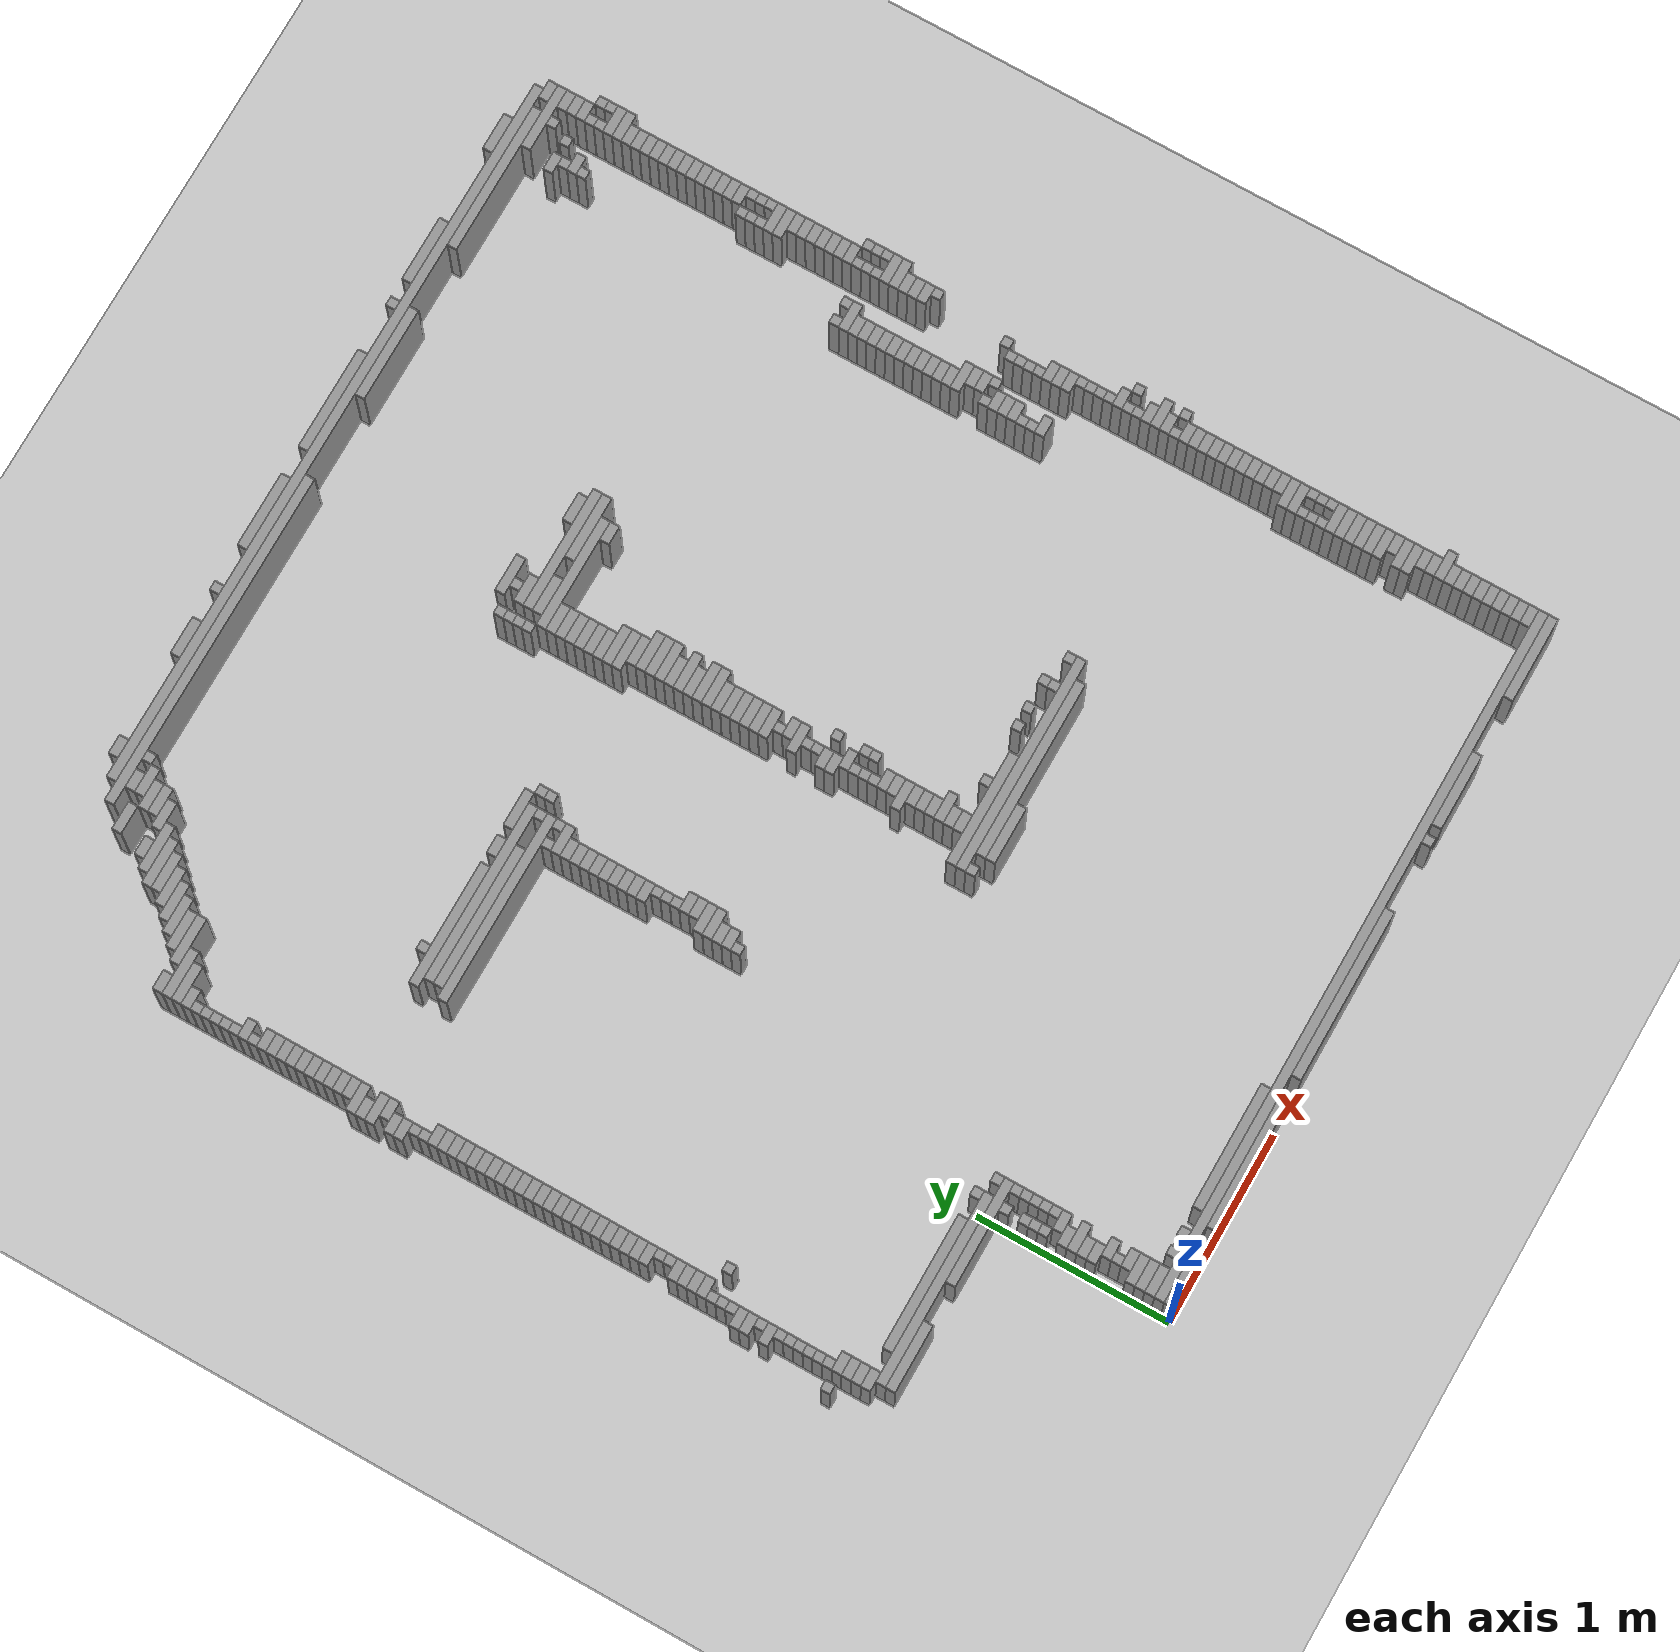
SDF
<?xml version="1.0"?>
<!--
  parking_map.world — scripts/generate_parking_world.py로 maps/parking_map.pgm에서
  자동 생성됨. 맵이 바뀌면 이 스크립트를 재실행해서 다시 만들 것(직접 손으로 수정 X).
  벽 386개, 해상도 0.05m/px, origin [-2.15, -1.05, 0].
-->
<sdf version="1.6">
  <world name="parking_mission">
    <include>
      <uri>model://sun</uri>
    </include>
    <include>
      <uri>model://ground_plane</uri>
    </include>

    <physics type="ode">
      <real_time_update_rate>1000.0</real_time_update_rate>
      <max_step_size>0.001</max_step_size>
    </physics>

    <model name="wall_1">
      <static>true</static>
      <pose>-0.1000 5.4750 0.2000 0 0 0</pose>
      <link name="link">
        <collision name="collision">
          <geometry>
            <box><size>0.1000 0.0500 0.4000</size></box>
          </geometry>
          <surface>
            <contact>
              <ode>
                <kp>20000.0</kp>
                <kd>10.0</kd>
                <max_vel>0.5</max_vel>
                <min_depth>0.001</min_depth>
              </ode>
            </contact>
            <friction>
              <ode>
                <mu>1.0</mu>
                <mu2>1.0</mu2>
              </ode>
            </friction>
          </surface>
        </collision>
        <visual name="visual">
          <geometry>
            <box><size>0.1000 0.0500 0.4000</size></box>
          </geometry>
          <material>
            <script>
              <name>Gazebo/Grey</name>
              <uri>file://media/materials/scripts/gazebo.material</uri>
            </script>
          </material>
        </visual>
      </link>
    </model>
    <model name="wall_2">
      <static>true</static>
      <pose>0.5000 5.4750 0.2000 0 0 0</pose>
      <link name="link">
        <collision name="collision">
          <geometry>
            <box><size>0.2000 0.0500 0.4000</size></box>
          </geometry>
          <surface>
            <contact>
              <ode>
                <kp>20000.0</kp>
                <kd>10.0</kd>
                <max_vel>0.5</max_vel>
                <min_depth>0.001</min_depth>
              </ode>
            </contact>
            <friction>
              <ode>
                <mu>1.0</mu>
                <mu2>1.0</mu2>
              </ode>
            </friction>
          </surface>
        </collision>
        <visual name="visual">
          <geometry>
            <box><size>0.2000 0.0500 0.4000</size></box>
          </geometry>
          <material>
            <script>
              <name>Gazebo/Grey</name>
              <uri>file://media/materials/scripts/gazebo.material</uri>
            </script>
          </material>
        </visual>
      </link>
    </model>
    <model name="wall_3">
      <static>true</static>
      <pose>0.7750 5.4750 0.2000 0 0 0</pose>
      <link name="link">
        <collision name="collision">
          <geometry>
            <box><size>0.0500 0.0500 0.4000</size></box>
          </geometry>
          <surface>
            <contact>
              <ode>
                <kp>20000.0</kp>
                <kd>10.0</kd>
                <max_vel>0.5</max_vel>
                <min_depth>0.001</min_depth>
              </ode>
            </contact>
            <friction>
              <ode>
                <mu>1.0</mu>
                <mu2>1.0</mu2>
              </ode>
            </friction>
          </surface>
        </collision>
        <visual name="visual">
          <geometry>
            <box><size>0.0500 0.0500 0.4000</size></box>
          </geometry>
          <material>
            <script>
              <name>Gazebo/Grey</name>
              <uri>file://media/materials/scripts/gazebo.material</uri>
            </script>
          </material>
        </visual>
      </link>
    </model>
    <model name="wall_4">
      <static>true</static>
      <pose>1.2000 5.4750 0.2000 0 0 0</pose>
      <link name="link">
        <collision name="collision">
          <geometry>
            <box><size>0.4000 0.0500 0.4000</size></box>
          </geometry>
          <surface>
            <contact>
              <ode>
                <kp>20000.0</kp>
                <kd>10.0</kd>
                <max_vel>0.5</max_vel>
                <min_depth>0.001</min_depth>
              </ode>
            </contact>
            <friction>
              <ode>
                <mu>1.0</mu>
                <mu2>1.0</mu2>
              </ode>
            </friction>
          </surface>
        </collision>
        <visual name="visual">
          <geometry>
            <box><size>0.4000 0.0500 0.4000</size></box>
          </geometry>
          <material>
            <script>
              <name>Gazebo/Grey</name>
              <uri>file://media/materials/scripts/gazebo.material</uri>
            </script>
          </material>
        </visual>
      </link>
    </model>
    <model name="wall_5">
      <static>true</static>
      <pose>1.8250 5.4750 0.2000 0 0 0</pose>
      <link name="link">
        <collision name="collision">
          <geometry>
            <box><size>0.5500 0.0500 0.4000</size></box>
          </geometry>
          <surface>
            <contact>
              <ode>
                <kp>20000.0</kp>
                <kd>10.0</kd>
                <max_vel>0.5</max_vel>
                <min_depth>0.001</min_depth>
              </ode>
            </contact>
            <friction>
              <ode>
                <mu>1.0</mu>
                <mu2>1.0</mu2>
              </ode>
            </friction>
          </surface>
        </collision>
        <visual name="visual">
          <geometry>
            <box><size>0.5500 0.0500 0.4000</size></box>
          </geometry>
          <material>
            <script>
              <name>Gazebo/Grey</name>
              <uri>file://media/materials/scripts/gazebo.material</uri>
            </script>
          </material>
        </visual>
      </link>
    </model>
    <model name="wall_6">
      <static>true</static>
      <pose>2.3750 5.4750 0.2000 0 0 0</pose>
      <link name="link">
        <collision name="collision">
          <geometry>
            <box><size>0.0500 0.0500 0.4000</size></box>
          </geometry>
          <surface>
            <contact>
              <ode>
                <kp>20000.0</kp>
                <kd>10.0</kd>
                <max_vel>0.5</max_vel>
                <min_depth>0.001</min_depth>
              </ode>
            </contact>
            <friction>
              <ode>
                <mu>1.0</mu>
                <mu2>1.0</mu2>
              </ode>
            </friction>
          </surface>
        </collision>
        <visual name="visual">
          <geometry>
            <box><size>0.0500 0.0500 0.4000</size></box>
          </geometry>
          <material>
            <script>
              <name>Gazebo/Grey</name>
              <uri>file://media/materials/scripts/gazebo.material</uri>
            </script>
          </material>
        </visual>
      </link>
    </model>
    <model name="wall_7">
      <static>true</static>
      <pose>2.6750 5.4750 0.2000 0 0 0</pose>
      <link name="link">
        <collision name="collision">
          <geometry>
            <box><size>0.3500 0.0500 0.4000</size></box>
          </geometry>
          <surface>
            <contact>
              <ode>
                <kp>20000.0</kp>
                <kd>10.0</kd>
                <max_vel>0.5</max_vel>
                <min_depth>0.001</min_depth>
              </ode>
            </contact>
            <friction>
              <ode>
                <mu>1.0</mu>
                <mu2>1.0</mu2>
              </ode>
            </friction>
          </surface>
        </collision>
        <visual name="visual">
          <geometry>
            <box><size>0.3500 0.0500 0.4000</size></box>
          </geometry>
          <material>
            <script>
              <name>Gazebo/Grey</name>
              <uri>file://media/materials/scripts/gazebo.material</uri>
            </script>
          </material>
        </visual>
      </link>
    </model>
    <model name="wall_8">
      <static>true</static>
      <pose>3.3500 5.4750 0.2000 0 0 0</pose>
      <link name="link">
        <collision name="collision">
          <geometry>
            <box><size>0.2000 0.0500 0.4000</size></box>
          </geometry>
          <surface>
            <contact>
              <ode>
                <kp>20000.0</kp>
                <kd>10.0</kd>
                <max_vel>0.5</max_vel>
                <min_depth>0.001</min_depth>
              </ode>
            </contact>
            <friction>
              <ode>
                <mu>1.0</mu>
                <mu2>1.0</mu2>
              </ode>
            </friction>
          </surface>
        </collision>
        <visual name="visual">
          <geometry>
            <box><size>0.2000 0.0500 0.4000</size></box>
          </geometry>
          <material>
            <script>
              <name>Gazebo/Grey</name>
              <uri>file://media/materials/scripts/gazebo.material</uri>
            </script>
          </material>
        </visual>
      </link>
    </model>
    <model name="wall_9">
      <static>true</static>
      <pose>1.7000 5.4250 0.2000 0 0 0</pose>
      <link name="link">
        <collision name="collision">
          <geometry>
            <box><size>3.9000 0.0500 0.4000</size></box>
          </geometry>
          <surface>
            <contact>
              <ode>
                <kp>20000.0</kp>
                <kd>10.0</kd>
                <max_vel>0.5</max_vel>
                <min_depth>0.001</min_depth>
              </ode>
            </contact>
            <friction>
              <ode>
                <mu>1.0</mu>
                <mu2>1.0</mu2>
              </ode>
            </friction>
          </surface>
        </collision>
        <visual name="visual">
          <geometry>
            <box><size>3.9000 0.0500 0.4000</size></box>
          </geometry>
          <material>
            <script>
              <name>Gazebo/Grey</name>
              <uri>file://media/materials/scripts/gazebo.material</uri>
            </script>
          </material>
        </visual>
      </link>
    </model>
    <model name="wall_10">
      <static>true</static>
      <pose>0.5500 5.3750 0.2000 0 0 0</pose>
      <link name="link">
        <collision name="collision">
          <geometry>
            <box><size>1.8000 0.0500 0.4000</size></box>
          </geometry>
          <surface>
            <contact>
              <ode>
                <kp>20000.0</kp>
                <kd>10.0</kd>
                <max_vel>0.5</max_vel>
                <min_depth>0.001</min_depth>
              </ode>
            </contact>
            <friction>
              <ode>
                <mu>1.0</mu>
                <mu2>1.0</mu2>
              </ode>
            </friction>
          </surface>
        </collision>
        <visual name="visual">
          <geometry>
            <box><size>1.8000 0.0500 0.4000</size></box>
          </geometry>
          <material>
            <script>
              <name>Gazebo/Grey</name>
              <uri>file://media/materials/scripts/gazebo.material</uri>
            </script>
          </material>
        </visual>
      </link>
    </model>
    <model name="wall_11">
      <static>true</static>
      <pose>2.1500 5.3750 0.2000 0 0 0</pose>
      <link name="link">
        <collision name="collision">
          <geometry>
            <box><size>0.5000 0.0500 0.4000</size></box>
          </geometry>
          <surface>
            <contact>
              <ode>
                <kp>20000.0</kp>
                <kd>10.0</kd>
                <max_vel>0.5</max_vel>
                <min_depth>0.001</min_depth>
              </ode>
            </contact>
            <friction>
              <ode>
                <mu>1.0</mu>
                <mu2>1.0</mu2>
              </ode>
            </friction>
          </surface>
        </collision>
        <visual name="visual">
          <geometry>
            <box><size>0.5000 0.0500 0.4000</size></box>
          </geometry>
          <material>
            <script>
              <name>Gazebo/Grey</name>
              <uri>file://media/materials/scripts/gazebo.material</uri>
            </script>
          </material>
        </visual>
      </link>
    </model>
    <model name="wall_12">
      <static>true</static>
      <pose>3.1500 5.3750 0.2000 0 0 0</pose>
      <link name="link">
        <collision name="collision">
          <geometry>
            <box><size>0.8000 0.0500 0.4000</size></box>
          </geometry>
          <surface>
            <contact>
              <ode>
                <kp>20000.0</kp>
                <kd>10.0</kd>
                <max_vel>0.5</max_vel>
                <min_depth>0.001</min_depth>
              </ode>
            </contact>
            <friction>
              <ode>
                <mu>1.0</mu>
                <mu2>1.0</mu2>
              </ode>
            </friction>
          </surface>
        </collision>
        <visual name="visual">
          <geometry>
            <box><size>0.8000 0.0500 0.4000</size></box>
          </geometry>
          <material>
            <script>
              <name>Gazebo/Grey</name>
              <uri>file://media/materials/scripts/gazebo.material</uri>
            </script>
          </material>
        </visual>
      </link>
    </model>
    <model name="wall_13">
      <static>true</static>
      <pose>3.6500 5.3750 0.2000 0 0 0</pose>
      <link name="link">
        <collision name="collision">
          <geometry>
            <box><size>0.1000 0.0500 0.4000</size></box>
          </geometry>
          <surface>
            <contact>
              <ode>
                <kp>20000.0</kp>
                <kd>10.0</kd>
                <max_vel>0.5</max_vel>
                <min_depth>0.001</min_depth>
              </ode>
            </contact>
            <friction>
              <ode>
                <mu>1.0</mu>
                <mu2>1.0</mu2>
              </ode>
            </friction>
          </surface>
        </collision>
        <visual name="visual">
          <geometry>
            <box><size>0.1000 0.0500 0.4000</size></box>
          </geometry>
          <material>
            <script>
              <name>Gazebo/Grey</name>
              <uri>file://media/materials/scripts/gazebo.material</uri>
            </script>
          </material>
        </visual>
      </link>
    </model>
    <model name="wall_14">
      <static>true</static>
      <pose>-0.2000 5.3250 0.2000 0 0 0</pose>
      <link name="link">
        <collision name="collision">
          <geometry>
            <box><size>0.1000 0.0500 0.4000</size></box>
          </geometry>
          <surface>
            <contact>
              <ode>
                <kp>20000.0</kp>
                <kd>10.0</kd>
                <max_vel>0.5</max_vel>
                <min_depth>0.001</min_depth>
              </ode>
            </contact>
            <friction>
              <ode>
                <mu>1.0</mu>
                <mu2>1.0</mu2>
              </ode>
            </friction>
          </surface>
        </collision>
        <visual name="visual">
          <geometry>
            <box><size>0.1000 0.0500 0.4000</size></box>
          </geometry>
          <material>
            <script>
              <name>Gazebo/Grey</name>
              <uri>file://media/materials/scripts/gazebo.material</uri>
            </script>
          </material>
        </visual>
      </link>
    </model>
    <model name="wall_15">
      <static>true</static>
      <pose>-0.0750 5.3250 0.2000 0 0 0</pose>
      <link name="link">
        <collision name="collision">
          <geometry>
            <box><size>0.0500 0.0500 0.4000</size></box>
          </geometry>
          <surface>
            <contact>
              <ode>
                <kp>20000.0</kp>
                <kd>10.0</kd>
                <max_vel>0.5</max_vel>
                <min_depth>0.001</min_depth>
              </ode>
            </contact>
            <friction>
              <ode>
                <mu>1.0</mu>
                <mu2>1.0</mu2>
              </ode>
            </friction>
          </surface>
        </collision>
        <visual name="visual">
          <geometry>
            <box><size>0.0500 0.0500 0.4000</size></box>
          </geometry>
          <material>
            <script>
              <name>Gazebo/Grey</name>
              <uri>file://media/materials/scripts/gazebo.material</uri>
            </script>
          </material>
        </visual>
      </link>
    </model>
    <model name="wall_16">
      <static>true</static>
      <pose>3.5250 5.3250 0.2000 0 0 0</pose>
      <link name="link">
        <collision name="collision">
          <geometry>
            <box><size>0.3500 0.0500 0.4000</size></box>
          </geometry>
          <surface>
            <contact>
              <ode>
                <kp>20000.0</kp>
                <kd>10.0</kd>
                <max_vel>0.5</max_vel>
                <min_depth>0.001</min_depth>
              </ode>
            </contact>
            <friction>
              <ode>
                <mu>1.0</mu>
                <mu2>1.0</mu2>
              </ode>
            </friction>
          </surface>
        </collision>
        <visual name="visual">
          <geometry>
            <box><size>0.3500 0.0500 0.4000</size></box>
          </geometry>
          <material>
            <script>
              <name>Gazebo/Grey</name>
              <uri>file://media/materials/scripts/gazebo.material</uri>
            </script>
          </material>
        </visual>
      </link>
    </model>
    <model name="wall_17">
      <static>true</static>
      <pose>-0.3750 5.2750 0.2000 0 0 0</pose>
      <link name="link">
        <collision name="collision">
          <geometry>
            <box><size>0.1500 0.0500 0.4000</size></box>
          </geometry>
          <surface>
            <contact>
              <ode>
                <kp>20000.0</kp>
                <kd>10.0</kd>
                <max_vel>0.5</max_vel>
                <min_depth>0.001</min_depth>
              </ode>
            </contact>
            <friction>
              <ode>
                <mu>1.0</mu>
                <mu2>1.0</mu2>
              </ode>
            </friction>
          </surface>
        </collision>
        <visual name="visual">
          <geometry>
            <box><size>0.1500 0.0500 0.4000</size></box>
          </geometry>
          <material>
            <script>
              <name>Gazebo/Grey</name>
              <uri>file://media/materials/scripts/gazebo.material</uri>
            </script>
          </material>
        </visual>
      </link>
    </model>
    <model name="wall_18">
      <static>true</static>
      <pose>-0.1750 5.2750 0.2000 0 0 0</pose>
      <link name="link">
        <collision name="collision">
          <geometry>
            <box><size>0.1500 0.0500 0.4000</size></box>
          </geometry>
          <surface>
            <contact>
              <ode>
                <kp>20000.0</kp>
                <kd>10.0</kd>
                <max_vel>0.5</max_vel>
                <min_depth>0.001</min_depth>
              </ode>
            </contact>
            <friction>
              <ode>
                <mu>1.0</mu>
                <mu2>1.0</mu2>
              </ode>
            </friction>
          </surface>
        </collision>
        <visual name="visual">
          <geometry>
            <box><size>0.1500 0.0500 0.4000</size></box>
          </geometry>
          <material>
            <script>
              <name>Gazebo/Grey</name>
              <uri>file://media/materials/scripts/gazebo.material</uri>
            </script>
          </material>
        </visual>
      </link>
    </model>
    <model name="wall_19">
      <static>true</static>
      <pose>3.5250 5.2750 0.2000 0 0 0</pose>
      <link name="link">
        <collision name="collision">
          <geometry>
            <box><size>0.0500 0.0500 0.4000</size></box>
          </geometry>
          <surface>
            <contact>
              <ode>
                <kp>20000.0</kp>
                <kd>10.0</kd>
                <max_vel>0.5</max_vel>
                <min_depth>0.001</min_depth>
              </ode>
            </contact>
            <friction>
              <ode>
                <mu>1.0</mu>
                <mu2>1.0</mu2>
              </ode>
            </friction>
          </surface>
        </collision>
        <visual name="visual">
          <geometry>
            <box><size>0.0500 0.0500 0.4000</size></box>
          </geometry>
          <material>
            <script>
              <name>Gazebo/Grey</name>
              <uri>file://media/materials/scripts/gazebo.material</uri>
            </script>
          </material>
        </visual>
      </link>
    </model>
    <model name="wall_20">
      <static>true</static>
      <pose>3.6500 5.2750 0.2000 0 0 0</pose>
      <link name="link">
        <collision name="collision">
          <geometry>
            <box><size>0.1000 0.0500 0.4000</size></box>
          </geometry>
          <surface>
            <contact>
              <ode>
                <kp>20000.0</kp>
                <kd>10.0</kd>
                <max_vel>0.5</max_vel>
                <min_depth>0.001</min_depth>
              </ode>
            </contact>
            <friction>
              <ode>
                <mu>1.0</mu>
                <mu2>1.0</mu2>
              </ode>
            </friction>
          </surface>
        </collision>
        <visual name="visual">
          <geometry>
            <box><size>0.1000 0.0500 0.4000</size></box>
          </geometry>
          <material>
            <script>
              <name>Gazebo/Grey</name>
              <uri>file://media/materials/scripts/gazebo.material</uri>
            </script>
          </material>
        </visual>
      </link>
    </model>
    <model name="wall_21">
      <static>true</static>
      <pose>-0.2250 5.2250 0.2000 0 0 0</pose>
      <link name="link">
        <collision name="collision">
          <geometry>
            <box><size>0.1500 0.0500 0.4000</size></box>
          </geometry>
          <surface>
            <contact>
              <ode>
                <kp>20000.0</kp>
                <kd>10.0</kd>
                <max_vel>0.5</max_vel>
                <min_depth>0.001</min_depth>
              </ode>
            </contact>
            <friction>
              <ode>
                <mu>1.0</mu>
                <mu2>1.0</mu2>
              </ode>
            </friction>
          </surface>
        </collision>
        <visual name="visual">
          <geometry>
            <box><size>0.1500 0.0500 0.4000</size></box>
          </geometry>
          <material>
            <script>
              <name>Gazebo/Grey</name>
              <uri>file://media/materials/scripts/gazebo.material</uri>
            </script>
          </material>
        </visual>
      </link>
    </model>
    <model name="wall_22">
      <static>true</static>
      <pose>3.6500 5.2250 0.2000 0 0 0</pose>
      <link name="link">
        <collision name="collision">
          <geometry>
            <box><size>0.1000 0.0500 0.4000</size></box>
          </geometry>
          <surface>
            <contact>
              <ode>
                <kp>20000.0</kp>
                <kd>10.0</kd>
                <max_vel>0.5</max_vel>
                <min_depth>0.001</min_depth>
              </ode>
            </contact>
            <friction>
              <ode>
                <mu>1.0</mu>
                <mu2>1.0</mu2>
              </ode>
            </friction>
          </surface>
        </collision>
        <visual name="visual">
          <geometry>
            <box><size>0.1000 0.0500 0.4000</size></box>
          </geometry>
          <material>
            <script>
              <name>Gazebo/Grey</name>
              <uri>file://media/materials/scripts/gazebo.material</uri>
            </script>
          </material>
        </visual>
      </link>
    </model>
    <model name="wall_23">
      <static>true</static>
      <pose>-0.2250 5.1750 0.2000 0 0 0</pose>
      <link name="link">
        <collision name="collision">
          <geometry>
            <box><size>0.1500 0.0500 0.4000</size></box>
          </geometry>
          <surface>
            <contact>
              <ode>
                <kp>20000.0</kp>
                <kd>10.0</kd>
                <max_vel>0.5</max_vel>
                <min_depth>0.001</min_depth>
              </ode>
            </contact>
            <friction>
              <ode>
                <mu>1.0</mu>
                <mu2>1.0</mu2>
              </ode>
            </friction>
          </surface>
        </collision>
        <visual name="visual">
          <geometry>
            <box><size>0.1500 0.0500 0.4000</size></box>
          </geometry>
          <material>
            <script>
              <name>Gazebo/Grey</name>
              <uri>file://media/materials/scripts/gazebo.material</uri>
            </script>
          </material>
        </visual>
      </link>
    </model>
    <model name="wall_24">
      <static>true</static>
      <pose>3.3500 5.1750 0.2000 0 0 0</pose>
      <link name="link">
        <collision name="collision">
          <geometry>
            <box><size>0.1000 0.0500 0.4000</size></box>
          </geometry>
          <surface>
            <contact>
              <ode>
                <kp>20000.0</kp>
                <kd>10.0</kd>
                <max_vel>0.5</max_vel>
                <min_depth>0.001</min_depth>
              </ode>
            </contact>
            <friction>
              <ode>
                <mu>1.0</mu>
                <mu2>1.0</mu2>
              </ode>
            </friction>
          </surface>
        </collision>
        <visual name="visual">
          <geometry>
            <box><size>0.1000 0.0500 0.4000</size></box>
          </geometry>
          <material>
            <script>
              <name>Gazebo/Grey</name>
              <uri>file://media/materials/scripts/gazebo.material</uri>
            </script>
          </material>
        </visual>
      </link>
    </model>
    <model name="wall_25">
      <static>true</static>
      <pose>3.4750 5.1750 0.2000 0 0 0</pose>
      <link name="link">
        <collision name="collision">
          <geometry>
            <box><size>0.0500 0.0500 0.4000</size></box>
          </geometry>
          <surface>
            <contact>
              <ode>
                <kp>20000.0</kp>
                <kd>10.0</kd>
                <max_vel>0.5</max_vel>
                <min_depth>0.001</min_depth>
              </ode>
            </contact>
            <friction>
              <ode>
                <mu>1.0</mu>
                <mu2>1.0</mu2>
              </ode>
            </friction>
          </surface>
        </collision>
        <visual name="visual">
          <geometry>
            <box><size>0.0500 0.0500 0.4000</size></box>
          </geometry>
          <material>
            <script>
              <name>Gazebo/Grey</name>
              <uri>file://media/materials/scripts/gazebo.material</uri>
            </script>
          </material>
        </visual>
      </link>
    </model>
    <model name="wall_26">
      <static>true</static>
      <pose>3.6500 5.1750 0.2000 0 0 0</pose>
      <link name="link">
        <collision name="collision">
          <geometry>
            <box><size>0.1000 0.0500 0.4000</size></box>
          </geometry>
          <surface>
            <contact>
              <ode>
                <kp>20000.0</kp>
                <kd>10.0</kd>
                <max_vel>0.5</max_vel>
                <min_depth>0.001</min_depth>
              </ode>
            </contact>
            <friction>
              <ode>
                <mu>1.0</mu>
                <mu2>1.0</mu2>
              </ode>
            </friction>
          </surface>
        </collision>
        <visual name="visual">
          <geometry>
            <box><size>0.1000 0.0500 0.4000</size></box>
          </geometry>
          <material>
            <script>
              <name>Gazebo/Grey</name>
              <uri>file://media/materials/scripts/gazebo.material</uri>
            </script>
          </material>
        </visual>
      </link>
    </model>
    <model name="wall_27">
      <static>true</static>
      <pose>-0.4500 5.1250 0.2000 0 0 0</pose>
      <link name="link">
        <collision name="collision">
          <geometry>
            <box><size>0.1000 0.0500 0.4000</size></box>
          </geometry>
          <surface>
            <contact>
              <ode>
                <kp>20000.0</kp>
                <kd>10.0</kd>
                <max_vel>0.5</max_vel>
                <min_depth>0.001</min_depth>
              </ode>
            </contact>
            <friction>
              <ode>
                <mu>1.0</mu>
                <mu2>1.0</mu2>
              </ode>
            </friction>
          </surface>
        </collision>
        <visual name="visual">
          <geometry>
            <box><size>0.1000 0.0500 0.4000</size></box>
          </geometry>
          <material>
            <script>
              <name>Gazebo/Grey</name>
              <uri>file://media/materials/scripts/gazebo.material</uri>
            </script>
          </material>
        </visual>
      </link>
    </model>
    <model name="wall_28">
      <static>true</static>
      <pose>-0.2750 5.1250 0.2000 0 0 0</pose>
      <link name="link">
        <collision name="collision">
          <geometry>
            <box><size>0.1500 0.0500 0.4000</size></box>
          </geometry>
          <surface>
            <contact>
              <ode>
                <kp>20000.0</kp>
                <kd>10.0</kd>
                <max_vel>0.5</max_vel>
                <min_depth>0.001</min_depth>
              </ode>
            </contact>
            <friction>
              <ode>
                <mu>1.0</mu>
                <mu2>1.0</mu2>
              </ode>
            </friction>
          </surface>
        </collision>
        <visual name="visual">
          <geometry>
            <box><size>0.1500 0.0500 0.4000</size></box>
          </geometry>
          <material>
            <script>
              <name>Gazebo/Grey</name>
              <uri>file://media/materials/scripts/gazebo.material</uri>
            </script>
          </material>
        </visual>
      </link>
    </model>
    <model name="wall_29">
      <static>true</static>
      <pose>3.3750 5.1250 0.2000 0 0 0</pose>
      <link name="link">
        <collision name="collision">
          <geometry>
            <box><size>0.0500 0.0500 0.4000</size></box>
          </geometry>
          <surface>
            <contact>
              <ode>
                <kp>20000.0</kp>
                <kd>10.0</kd>
                <max_vel>0.5</max_vel>
                <min_depth>0.001</min_depth>
              </ode>
            </contact>
            <friction>
              <ode>
                <mu>1.0</mu>
                <mu2>1.0</mu2>
              </ode>
            </friction>
          </surface>
        </collision>
        <visual name="visual">
          <geometry>
            <box><size>0.0500 0.0500 0.4000</size></box>
          </geometry>
          <material>
            <script>
              <name>Gazebo/Grey</name>
              <uri>file://media/materials/scripts/gazebo.material</uri>
            </script>
          </material>
        </visual>
      </link>
    </model>
    <model name="wall_30">
      <static>true</static>
      <pose>3.6250 5.1250 0.2000 0 0 0</pose>
      <link name="link">
        <collision name="collision">
          <geometry>
            <box><size>0.0500 0.0500 0.4000</size></box>
          </geometry>
          <surface>
            <contact>
              <ode>
                <kp>20000.0</kp>
                <kd>10.0</kd>
                <max_vel>0.5</max_vel>
                <min_depth>0.001</min_depth>
              </ode>
            </contact>
            <friction>
              <ode>
                <mu>1.0</mu>
                <mu2>1.0</mu2>
              </ode>
            </friction>
          </surface>
        </collision>
        <visual name="visual">
          <geometry>
            <box><size>0.0500 0.0500 0.4000</size></box>
          </geometry>
          <material>
            <script>
              <name>Gazebo/Grey</name>
              <uri>file://media/materials/scripts/gazebo.material</uri>
            </script>
          </material>
        </visual>
      </link>
    </model>
    <model name="wall_31">
      <static>true</static>
      <pose>3.7250 5.1250 0.2000 0 0 0</pose>
      <link name="link">
        <collision name="collision">
          <geometry>
            <box><size>0.0500 0.0500 0.4000</size></box>
          </geometry>
          <surface>
            <contact>
              <ode>
                <kp>20000.0</kp>
                <kd>10.0</kd>
                <max_vel>0.5</max_vel>
                <min_depth>0.001</min_depth>
              </ode>
            </contact>
            <friction>
              <ode>
                <mu>1.0</mu>
                <mu2>1.0</mu2>
              </ode>
            </friction>
          </surface>
        </collision>
        <visual name="visual">
          <geometry>
            <box><size>0.0500 0.0500 0.4000</size></box>
          </geometry>
          <material>
            <script>
              <name>Gazebo/Grey</name>
              <uri>file://media/materials/scripts/gazebo.material</uri>
            </script>
          </material>
        </visual>
      </link>
    </model>
    <model name="wall_32">
      <static>true</static>
      <pose>-0.4250 5.0750 0.2000 0 0 0</pose>
      <link name="link">
        <collision name="collision">
          <geometry>
            <box><size>0.2500 0.0500 0.4000</size></box>
          </geometry>
          <surface>
            <contact>
              <ode>
                <kp>20000.0</kp>
                <kd>10.0</kd>
                <max_vel>0.5</max_vel>
                <min_depth>0.001</min_depth>
              </ode>
            </contact>
            <friction>
              <ode>
                <mu>1.0</mu>
                <mu2>1.0</mu2>
              </ode>
            </friction>
          </surface>
        </collision>
        <visual name="visual">
          <geometry>
            <box><size>0.2500 0.0500 0.4000</size></box>
          </geometry>
          <material>
            <script>
              <name>Gazebo/Grey</name>
              <uri>file://media/materials/scripts/gazebo.material</uri>
            </script>
          </material>
        </visual>
      </link>
    </model>
    <model name="wall_33">
      <static>true</static>
      <pose>3.4000 5.0750 0.2000 0 0 0</pose>
      <link name="link">
        <collision name="collision">
          <geometry>
            <box><size>0.1000 0.0500 0.4000</size></box>
          </geometry>
          <surface>
            <contact>
              <ode>
                <kp>20000.0</kp>
                <kd>10.0</kd>
                <max_vel>0.5</max_vel>
                <min_depth>0.001</min_depth>
              </ode>
            </contact>
            <friction>
              <ode>
                <mu>1.0</mu>
                <mu2>1.0</mu2>
              </ode>
            </friction>
          </surface>
        </collision>
        <visual name="visual">
          <geometry>
            <box><size>0.1000 0.0500 0.4000</size></box>
          </geometry>
          <material>
            <script>
              <name>Gazebo/Grey</name>
              <uri>file://media/materials/scripts/gazebo.material</uri>
            </script>
          </material>
        </visual>
      </link>
    </model>
    <model name="wall_34">
      <static>true</static>
      <pose>3.6250 5.0750 0.2000 0 0 0</pose>
      <link name="link">
        <collision name="collision">
          <geometry>
            <box><size>0.0500 0.0500 0.4000</size></box>
          </geometry>
          <surface>
            <contact>
              <ode>
                <kp>20000.0</kp>
                <kd>10.0</kd>
                <max_vel>0.5</max_vel>
                <min_depth>0.001</min_depth>
              </ode>
            </contact>
            <friction>
              <ode>
                <mu>1.0</mu>
                <mu2>1.0</mu2>
              </ode>
            </friction>
          </surface>
        </collision>
        <visual name="visual">
          <geometry>
            <box><size>0.0500 0.0500 0.4000</size></box>
          </geometry>
          <material>
            <script>
              <name>Gazebo/Grey</name>
              <uri>file://media/materials/scripts/gazebo.material</uri>
            </script>
          </material>
        </visual>
      </link>
    </model>
    <model name="wall_35">
      <static>true</static>
      <pose>3.7250 5.0750 0.2000 0 0 0</pose>
      <link name="link">
        <collision name="collision">
          <geometry>
            <box><size>0.0500 0.0500 0.4000</size></box>
          </geometry>
          <surface>
            <contact>
              <ode>
                <kp>20000.0</kp>
                <kd>10.0</kd>
                <max_vel>0.5</max_vel>
                <min_depth>0.001</min_depth>
              </ode>
            </contact>
            <friction>
              <ode>
                <mu>1.0</mu>
                <mu2>1.0</mu2>
              </ode>
            </friction>
          </surface>
        </collision>
        <visual name="visual">
          <geometry>
            <box><size>0.0500 0.0500 0.4000</size></box>
          </geometry>
          <material>
            <script>
              <name>Gazebo/Grey</name>
              <uri>file://media/materials/scripts/gazebo.material</uri>
            </script>
          </material>
        </visual>
      </link>
    </model>
    <model name="wall_36">
      <static>true</static>
      <pose>-0.4750 5.0250 0.2000 0 0 0</pose>
      <link name="link">
        <collision name="collision">
          <geometry>
            <box><size>0.2500 0.0500 0.4000</size></box>
          </geometry>
          <surface>
            <contact>
              <ode>
                <kp>20000.0</kp>
                <kd>10.0</kd>
                <max_vel>0.5</max_vel>
                <min_depth>0.001</min_depth>
              </ode>
            </contact>
            <friction>
              <ode>
                <mu>1.0</mu>
                <mu2>1.0</mu2>
              </ode>
            </friction>
          </surface>
        </collision>
        <visual name="visual">
          <geometry>
            <box><size>0.2500 0.0500 0.4000</size></box>
          </geometry>
          <material>
            <script>
              <name>Gazebo/Grey</name>
              <uri>file://media/materials/scripts/gazebo.material</uri>
            </script>
          </material>
        </visual>
      </link>
    </model>
    <model name="wall_37">
      <static>true</static>
      <pose>3.3750 5.0250 0.2000 0 0 0</pose>
      <link name="link">
        <collision name="collision">
          <geometry>
            <box><size>0.0500 0.0500 0.4000</size></box>
          </geometry>
          <surface>
            <contact>
              <ode>
                <kp>20000.0</kp>
                <kd>10.0</kd>
                <max_vel>0.5</max_vel>
                <min_depth>0.001</min_depth>
              </ode>
            </contact>
            <friction>
              <ode>
                <mu>1.0</mu>
                <mu2>1.0</mu2>
              </ode>
            </friction>
          </surface>
        </collision>
        <visual name="visual">
          <geometry>
            <box><size>0.0500 0.0500 0.4000</size></box>
          </geometry>
          <material>
            <script>
              <name>Gazebo/Grey</name>
              <uri>file://media/materials/scripts/gazebo.material</uri>
            </script>
          </material>
        </visual>
      </link>
    </model>
    <model name="wall_38">
      <static>true</static>
      <pose>3.6750 5.0250 0.2000 0 0 0</pose>
      <link name="link">
        <collision name="collision">
          <geometry>
            <box><size>0.1500 0.0500 0.4000</size></box>
          </geometry>
          <surface>
            <contact>
              <ode>
                <kp>20000.0</kp>
                <kd>10.0</kd>
                <max_vel>0.5</max_vel>
                <min_depth>0.001</min_depth>
              </ode>
            </contact>
            <friction>
              <ode>
                <mu>1.0</mu>
                <mu2>1.0</mu2>
              </ode>
            </friction>
          </surface>
        </collision>
        <visual name="visual">
          <geometry>
            <box><size>0.1500 0.0500 0.4000</size></box>
          </geometry>
          <material>
            <script>
              <name>Gazebo/Grey</name>
              <uri>file://media/materials/scripts/gazebo.material</uri>
            </script>
          </material>
        </visual>
      </link>
    </model>
    <model name="wall_39">
      <static>true</static>
      <pose>-0.5000 4.9750 0.2000 0 0 0</pose>
      <link name="link">
        <collision name="collision">
          <geometry>
            <box><size>0.2000 0.0500 0.4000</size></box>
          </geometry>
          <surface>
            <contact>
              <ode>
                <kp>20000.0</kp>
                <kd>10.0</kd>
                <max_vel>0.5</max_vel>
                <min_depth>0.001</min_depth>
              </ode>
            </contact>
            <friction>
              <ode>
                <mu>1.0</mu>
                <mu2>1.0</mu2>
              </ode>
            </friction>
          </surface>
        </collision>
        <visual name="visual">
          <geometry>
            <box><size>0.2000 0.0500 0.4000</size></box>
          </geometry>
          <material>
            <script>
              <name>Gazebo/Grey</name>
              <uri>file://media/materials/scripts/gazebo.material</uri>
            </script>
          </material>
        </visual>
      </link>
    </model>
    <model name="wall_40">
      <static>true</static>
      <pose>3.6750 4.9750 0.2000 0 0 0</pose>
      <link name="link">
        <collision name="collision">
          <geometry>
            <box><size>0.1500 0.0500 0.4000</size></box>
          </geometry>
          <surface>
            <contact>
              <ode>
                <kp>20000.0</kp>
                <kd>10.0</kd>
                <max_vel>0.5</max_vel>
                <min_depth>0.001</min_depth>
              </ode>
            </contact>
            <friction>
              <ode>
                <mu>1.0</mu>
                <mu2>1.0</mu2>
              </ode>
            </friction>
          </surface>
        </collision>
        <visual name="visual">
          <geometry>
            <box><size>0.1500 0.0500 0.4000</size></box>
          </geometry>
          <material>
            <script>
              <name>Gazebo/Grey</name>
              <uri>file://media/materials/scripts/gazebo.material</uri>
            </script>
          </material>
        </visual>
      </link>
    </model>
    <model name="wall_41">
      <static>true</static>
      <pose>-0.5500 4.9250 0.2000 0 0 0</pose>
      <link name="link">
        <collision name="collision">
          <geometry>
            <box><size>0.2000 0.0500 0.4000</size></box>
          </geometry>
          <surface>
            <contact>
              <ode>
                <kp>20000.0</kp>
                <kd>10.0</kd>
                <max_vel>0.5</max_vel>
                <min_depth>0.001</min_depth>
              </ode>
            </contact>
            <friction>
              <ode>
                <mu>1.0</mu>
                <mu2>1.0</mu2>
              </ode>
            </friction>
          </surface>
        </collision>
        <visual name="visual">
          <geometry>
            <box><size>0.2000 0.0500 0.4000</size></box>
          </geometry>
          <material>
            <script>
              <name>Gazebo/Grey</name>
              <uri>file://media/materials/scripts/gazebo.material</uri>
            </script>
          </material>
        </visual>
      </link>
    </model>
    <model name="wall_42">
      <static>true</static>
      <pose>3.6500 4.9250 0.2000 0 0 0</pose>
      <link name="link">
        <collision name="collision">
          <geometry>
            <box><size>0.1000 0.0500 0.4000</size></box>
          </geometry>
          <surface>
            <contact>
              <ode>
                <kp>20000.0</kp>
                <kd>10.0</kd>
                <max_vel>0.5</max_vel>
                <min_depth>0.001</min_depth>
              </ode>
            </contact>
            <friction>
              <ode>
                <mu>1.0</mu>
                <mu2>1.0</mu2>
              </ode>
            </friction>
          </surface>
        </collision>
        <visual name="visual">
          <geometry>
            <box><size>0.1000 0.0500 0.4000</size></box>
          </geometry>
          <material>
            <script>
              <name>Gazebo/Grey</name>
              <uri>file://media/materials/scripts/gazebo.material</uri>
            </script>
          </material>
        </visual>
      </link>
    </model>
    <model name="wall_43">
      <static>true</static>
      <pose>-0.6000 4.8750 0.2000 0 0 0</pose>
      <link name="link">
        <collision name="collision">
          <geometry>
            <box><size>0.2000 0.0500 0.4000</size></box>
          </geometry>
          <surface>
            <contact>
              <ode>
                <kp>20000.0</kp>
                <kd>10.0</kd>
                <max_vel>0.5</max_vel>
                <min_depth>0.001</min_depth>
              </ode>
            </contact>
            <friction>
              <ode>
                <mu>1.0</mu>
                <mu2>1.0</mu2>
              </ode>
            </friction>
          </surface>
        </collision>
        <visual name="visual">
          <geometry>
            <box><size>0.2000 0.0500 0.4000</size></box>
          </geometry>
          <material>
            <script>
              <name>Gazebo/Grey</name>
              <uri>file://media/materials/scripts/gazebo.material</uri>
            </script>
          </material>
        </visual>
      </link>
    </model>
    <model name="wall_44">
      <static>true</static>
      <pose>3.6500 4.8750 0.2000 0 0 0</pose>
      <link name="link">
        <collision name="collision">
          <geometry>
            <box><size>0.1000 0.0500 0.4000</size></box>
          </geometry>
          <surface>
            <contact>
              <ode>
                <kp>20000.0</kp>
                <kd>10.0</kd>
                <max_vel>0.5</max_vel>
                <min_depth>0.001</min_depth>
              </ode>
            </contact>
            <friction>
              <ode>
                <mu>1.0</mu>
                <mu2>1.0</mu2>
              </ode>
            </friction>
          </surface>
        </collision>
        <visual name="visual">
          <geometry>
            <box><size>0.1000 0.0500 0.4000</size></box>
          </geometry>
          <material>
            <script>
              <name>Gazebo/Grey</name>
              <uri>file://media/materials/scripts/gazebo.material</uri>
            </script>
          </material>
        </visual>
      </link>
    </model>
    <model name="wall_45">
      <static>true</static>
      <pose>-0.6500 4.8250 0.2000 0 0 0</pose>
      <link name="link">
        <collision name="collision">
          <geometry>
            <box><size>0.2000 0.0500 0.4000</size></box>
          </geometry>
          <surface>
            <contact>
              <ode>
                <kp>20000.0</kp>
                <kd>10.0</kd>
                <max_vel>0.5</max_vel>
                <min_depth>0.001</min_depth>
              </ode>
            </contact>
            <friction>
              <ode>
                <mu>1.0</mu>
                <mu2>1.0</mu2>
              </ode>
            </friction>
          </surface>
        </collision>
        <visual name="visual">
          <geometry>
            <box><size>0.2000 0.0500 0.4000</size></box>
          </geometry>
          <material>
            <script>
              <name>Gazebo/Grey</name>
              <uri>file://media/materials/scripts/gazebo.material</uri>
            </script>
          </material>
        </visual>
      </link>
    </model>
    <model name="wall_46">
      <static>true</static>
      <pose>3.6500 4.8250 0.2000 0 0 0</pose>
      <link name="link">
        <collision name="collision">
          <geometry>
            <box><size>0.1000 0.0500 0.4000</size></box>
          </geometry>
          <surface>
            <contact>
              <ode>
                <kp>20000.0</kp>
                <kd>10.0</kd>
                <max_vel>0.5</max_vel>
                <min_depth>0.001</min_depth>
              </ode>
            </contact>
            <friction>
              <ode>
                <mu>1.0</mu>
                <mu2>1.0</mu2>
              </ode>
            </friction>
          </surface>
        </collision>
        <visual name="visual">
          <geometry>
            <box><size>0.1000 0.0500 0.4000</size></box>
          </geometry>
          <material>
            <script>
              <name>Gazebo/Grey</name>
              <uri>file://media/materials/scripts/gazebo.material</uri>
            </script>
          </material>
        </visual>
      </link>
    </model>
    <model name="wall_47">
      <static>true</static>
      <pose>-0.7000 4.7750 0.2000 0 0 0</pose>
      <link name="link">
        <collision name="collision">
          <geometry>
            <box><size>0.2000 0.0500 0.4000</size></box>
          </geometry>
          <surface>
            <contact>
              <ode>
                <kp>20000.0</kp>
                <kd>10.0</kd>
                <max_vel>0.5</max_vel>
                <min_depth>0.001</min_depth>
              </ode>
            </contact>
            <friction>
              <ode>
                <mu>1.0</mu>
                <mu2>1.0</mu2>
              </ode>
            </friction>
          </surface>
        </collision>
        <visual name="visual">
          <geometry>
            <box><size>0.2000 0.0500 0.4000</size></box>
          </geometry>
          <material>
            <script>
              <name>Gazebo/Grey</name>
              <uri>file://media/materials/scripts/gazebo.material</uri>
            </script>
          </material>
        </visual>
      </link>
    </model>
    <model name="wall_48">
      <static>true</static>
      <pose>3.6500 4.7750 0.2000 0 0 0</pose>
      <link name="link">
        <collision name="collision">
          <geometry>
            <box><size>0.1000 0.0500 0.4000</size></box>
          </geometry>
          <surface>
            <contact>
              <ode>
                <kp>20000.0</kp>
                <kd>10.0</kd>
                <max_vel>0.5</max_vel>
                <min_depth>0.001</min_depth>
              </ode>
            </contact>
            <friction>
              <ode>
                <mu>1.0</mu>
                <mu2>1.0</mu2>
              </ode>
            </friction>
          </surface>
        </collision>
        <visual name="visual">
          <geometry>
            <box><size>0.1000 0.0500 0.4000</size></box>
          </geometry>
          <material>
            <script>
              <name>Gazebo/Grey</name>
              <uri>file://media/materials/scripts/gazebo.material</uri>
            </script>
          </material>
        </visual>
      </link>
    </model>
    <model name="wall_49">
      <static>true</static>
      <pose>-0.9500 4.7250 0.2000 0 0 0</pose>
      <link name="link">
        <collision name="collision">
          <geometry>
            <box><size>0.1000 0.0500 0.4000</size></box>
          </geometry>
          <surface>
            <contact>
              <ode>
                <kp>20000.0</kp>
                <kd>10.0</kd>
                <max_vel>0.5</max_vel>
                <min_depth>0.001</min_depth>
              </ode>
            </contact>
            <friction>
              <ode>
                <mu>1.0</mu>
                <mu2>1.0</mu2>
              </ode>
            </friction>
          </surface>
        </collision>
        <visual name="visual">
          <geometry>
            <box><size>0.1000 0.0500 0.4000</size></box>
          </geometry>
          <material>
            <script>
              <name>Gazebo/Grey</name>
              <uri>file://media/materials/scripts/gazebo.material</uri>
            </script>
          </material>
        </visual>
      </link>
    </model>
    <model name="wall_50">
      <static>true</static>
      <pose>-0.7250 4.7250 0.2000 0 0 0</pose>
      <link name="link">
        <collision name="collision">
          <geometry>
            <box><size>0.2500 0.0500 0.4000</size></box>
          </geometry>
          <surface>
            <contact>
              <ode>
                <kp>20000.0</kp>
                <kd>10.0</kd>
                <max_vel>0.5</max_vel>
                <min_depth>0.001</min_depth>
              </ode>
            </contact>
            <friction>
              <ode>
                <mu>1.0</mu>
                <mu2>1.0</mu2>
              </ode>
            </friction>
          </surface>
        </collision>
        <visual name="visual">
          <geometry>
            <box><size>0.2500 0.0500 0.4000</size></box>
          </geometry>
          <material>
            <script>
              <name>Gazebo/Grey</name>
              <uri>file://media/materials/scripts/gazebo.material</uri>
            </script>
          </material>
        </visual>
      </link>
    </model>
    <model name="wall_51">
      <static>true</static>
      <pose>3.6500 4.7250 0.2000 0 0 0</pose>
      <link name="link">
        <collision name="collision">
          <geometry>
            <box><size>0.1000 0.0500 0.4000</size></box>
          </geometry>
          <surface>
            <contact>
              <ode>
                <kp>20000.0</kp>
                <kd>10.0</kd>
                <max_vel>0.5</max_vel>
                <min_depth>0.001</min_depth>
              </ode>
            </contact>
            <friction>
              <ode>
                <mu>1.0</mu>
                <mu2>1.0</mu2>
              </ode>
            </friction>
          </surface>
        </collision>
        <visual name="visual">
          <geometry>
            <box><size>0.1000 0.0500 0.4000</size></box>
          </geometry>
          <material>
            <script>
              <name>Gazebo/Grey</name>
              <uri>file://media/materials/scripts/gazebo.material</uri>
            </script>
          </material>
        </visual>
      </link>
    </model>
    <model name="wall_52">
      <static>true</static>
      <pose>-0.8750 4.6750 0.2000 0 0 0</pose>
      <link name="link">
        <collision name="collision">
          <geometry>
            <box><size>0.2500 0.0500 0.4000</size></box>
          </geometry>
          <surface>
            <contact>
              <ode>
                <kp>20000.0</kp>
                <kd>10.0</kd>
                <max_vel>0.5</max_vel>
                <min_depth>0.001</min_depth>
              </ode>
            </contact>
            <friction>
              <ode>
                <mu>1.0</mu>
                <mu2>1.0</mu2>
              </ode>
            </friction>
          </surface>
        </collision>
        <visual name="visual">
          <geometry>
            <box><size>0.2500 0.0500 0.4000</size></box>
          </geometry>
          <material>
            <script>
              <name>Gazebo/Grey</name>
              <uri>file://media/materials/scripts/gazebo.material</uri>
            </script>
          </material>
        </visual>
      </link>
    </model>
    <model name="wall_53">
      <static>true</static>
      <pose>3.6500 4.6750 0.2000 0 0 0</pose>
      <link name="link">
        <collision name="collision">
          <geometry>
            <box><size>0.1000 0.0500 0.4000</size></box>
          </geometry>
          <surface>
            <contact>
              <ode>
                <kp>20000.0</kp>
                <kd>10.0</kd>
                <max_vel>0.5</max_vel>
                <min_depth>0.001</min_depth>
              </ode>
            </contact>
            <friction>
              <ode>
                <mu>1.0</mu>
                <mu2>1.0</mu2>
              </ode>
            </friction>
          </surface>
        </collision>
        <visual name="visual">
          <geometry>
            <box><size>0.1000 0.0500 0.4000</size></box>
          </geometry>
          <material>
            <script>
              <name>Gazebo/Grey</name>
              <uri>file://media/materials/scripts/gazebo.material</uri>
            </script>
          </material>
        </visual>
      </link>
    </model>
    <model name="wall_54">
      <static>true</static>
      <pose>-0.9000 4.6250 0.2000 0 0 0</pose>
      <link name="link">
        <collision name="collision">
          <geometry>
            <box><size>0.2000 0.0500 0.4000</size></box>
          </geometry>
          <surface>
            <contact>
              <ode>
                <kp>20000.0</kp>
                <kd>10.0</kd>
                <max_vel>0.5</max_vel>
                <min_depth>0.001</min_depth>
              </ode>
            </contact>
            <friction>
              <ode>
                <mu>1.0</mu>
                <mu2>1.0</mu2>
              </ode>
            </friction>
          </surface>
        </collision>
        <visual name="visual">
          <geometry>
            <box><size>0.2000 0.0500 0.4000</size></box>
          </geometry>
          <material>
            <script>
              <name>Gazebo/Grey</name>
              <uri>file://media/materials/scripts/gazebo.material</uri>
            </script>
          </material>
        </visual>
      </link>
    </model>
    <model name="wall_55">
      <static>true</static>
      <pose>3.6500 4.6250 0.2000 0 0 0</pose>
      <link name="link">
        <collision name="collision">
          <geometry>
            <box><size>0.1000 0.0500 0.4000</size></box>
          </geometry>
          <surface>
            <contact>
              <ode>
                <kp>20000.0</kp>
                <kd>10.0</kd>
                <max_vel>0.5</max_vel>
                <min_depth>0.001</min_depth>
              </ode>
            </contact>
            <friction>
              <ode>
                <mu>1.0</mu>
                <mu2>1.0</mu2>
              </ode>
            </friction>
          </surface>
        </collision>
        <visual name="visual">
          <geometry>
            <box><size>0.1000 0.0500 0.4000</size></box>
          </geometry>
          <material>
            <script>
              <name>Gazebo/Grey</name>
              <uri>file://media/materials/scripts/gazebo.material</uri>
            </script>
          </material>
        </visual>
      </link>
    </model>
    <model name="wall_56">
      <static>true</static>
      <pose>-0.9500 4.5750 0.2000 0 0 0</pose>
      <link name="link">
        <collision name="collision">
          <geometry>
            <box><size>0.1000 0.0500 0.4000</size></box>
          </geometry>
          <surface>
            <contact>
              <ode>
                <kp>20000.0</kp>
                <kd>10.0</kd>
                <max_vel>0.5</max_vel>
                <min_depth>0.001</min_depth>
              </ode>
            </contact>
            <friction>
              <ode>
                <mu>1.0</mu>
                <mu2>1.0</mu2>
              </ode>
            </friction>
          </surface>
        </collision>
        <visual name="visual">
          <geometry>
            <box><size>0.1000 0.0500 0.4000</size></box>
          </geometry>
          <material>
            <script>
              <name>Gazebo/Grey</name>
              <uri>file://media/materials/scripts/gazebo.material</uri>
            </script>
          </material>
        </visual>
      </link>
    </model>
    <model name="wall_57">
      <static>true</static>
      <pose>3.6500 4.5750 0.2000 0 0 0</pose>
      <link name="link">
        <collision name="collision">
          <geometry>
            <box><size>0.1000 0.0500 0.4000</size></box>
          </geometry>
          <surface>
            <contact>
              <ode>
                <kp>20000.0</kp>
                <kd>10.0</kd>
                <max_vel>0.5</max_vel>
                <min_depth>0.001</min_depth>
              </ode>
            </contact>
            <friction>
              <ode>
                <mu>1.0</mu>
                <mu2>1.0</mu2>
              </ode>
            </friction>
          </surface>
        </collision>
        <visual name="visual">
          <geometry>
            <box><size>0.1000 0.0500 0.4000</size></box>
          </geometry>
          <material>
            <script>
              <name>Gazebo/Grey</name>
              <uri>file://media/materials/scripts/gazebo.material</uri>
            </script>
          </material>
        </visual>
      </link>
    </model>
    <model name="wall_58">
      <static>true</static>
      <pose>-0.9750 4.5250 0.2000 0 0 0</pose>
      <link name="link">
        <collision name="collision">
          <geometry>
            <box><size>0.0500 0.0500 0.4000</size></box>
          </geometry>
          <surface>
            <contact>
              <ode>
                <kp>20000.0</kp>
                <kd>10.0</kd>
                <max_vel>0.5</max_vel>
                <min_depth>0.001</min_depth>
              </ode>
            </contact>
            <friction>
              <ode>
                <mu>1.0</mu>
                <mu2>1.0</mu2>
              </ode>
            </friction>
          </surface>
        </collision>
        <visual name="visual">
          <geometry>
            <box><size>0.0500 0.0500 0.4000</size></box>
          </geometry>
          <material>
            <script>
              <name>Gazebo/Grey</name>
              <uri>file://media/materials/scripts/gazebo.material</uri>
            </script>
          </material>
        </visual>
      </link>
    </model>
    <model name="wall_59">
      <static>true</static>
      <pose>3.6500 4.5250 0.2000 0 0 0</pose>
      <link name="link">
        <collision name="collision">
          <geometry>
            <box><size>0.1000 0.0500 0.4000</size></box>
          </geometry>
          <surface>
            <contact>
              <ode>
                <kp>20000.0</kp>
                <kd>10.0</kd>
                <max_vel>0.5</max_vel>
                <min_depth>0.001</min_depth>
              </ode>
            </contact>
            <friction>
              <ode>
                <mu>1.0</mu>
                <mu2>1.0</mu2>
              </ode>
            </friction>
          </surface>
        </collision>
        <visual name="visual">
          <geometry>
            <box><size>0.1000 0.0500 0.4000</size></box>
          </geometry>
          <material>
            <script>
              <name>Gazebo/Grey</name>
              <uri>file://media/materials/scripts/gazebo.material</uri>
            </script>
          </material>
        </visual>
      </link>
    </model>
    <model name="wall_60">
      <static>true</static>
      <pose>-0.9750 4.4750 0.2000 0 0 0</pose>
      <link name="link">
        <collision name="collision">
          <geometry>
            <box><size>0.0500 0.0500 0.4000</size></box>
          </geometry>
          <surface>
            <contact>
              <ode>
                <kp>20000.0</kp>
                <kd>10.0</kd>
                <max_vel>0.5</max_vel>
                <min_depth>0.001</min_depth>
              </ode>
            </contact>
            <friction>
              <ode>
                <mu>1.0</mu>
                <mu2>1.0</mu2>
              </ode>
            </friction>
          </surface>
        </collision>
        <visual name="visual">
          <geometry>
            <box><size>0.0500 0.0500 0.4000</size></box>
          </geometry>
          <material>
            <script>
              <name>Gazebo/Grey</name>
              <uri>file://media/materials/scripts/gazebo.material</uri>
            </script>
          </material>
        </visual>
      </link>
    </model>
    <model name="wall_61">
      <static>true</static>
      <pose>3.6500 4.4750 0.2000 0 0 0</pose>
      <link name="link">
        <collision name="collision">
          <geometry>
            <box><size>0.1000 0.0500 0.4000</size></box>
          </geometry>
          <surface>
            <contact>
              <ode>
                <kp>20000.0</kp>
                <kd>10.0</kd>
                <max_vel>0.5</max_vel>
                <min_depth>0.001</min_depth>
              </ode>
            </contact>
            <friction>
              <ode>
                <mu>1.0</mu>
                <mu2>1.0</mu2>
              </ode>
            </friction>
          </surface>
        </collision>
        <visual name="visual">
          <geometry>
            <box><size>0.1000 0.0500 0.4000</size></box>
          </geometry>
          <material>
            <script>
              <name>Gazebo/Grey</name>
              <uri>file://media/materials/scripts/gazebo.material</uri>
            </script>
          </material>
        </visual>
      </link>
    </model>
    <model name="wall_62">
      <static>true</static>
      <pose>-0.9750 4.4250 0.2000 0 0 0</pose>
      <link name="link">
        <collision name="collision">
          <geometry>
            <box><size>0.0500 0.0500 0.4000</size></box>
          </geometry>
          <surface>
            <contact>
              <ode>
                <kp>20000.0</kp>
                <kd>10.0</kd>
                <max_vel>0.5</max_vel>
                <min_depth>0.001</min_depth>
              </ode>
            </contact>
            <friction>
              <ode>
                <mu>1.0</mu>
                <mu2>1.0</mu2>
              </ode>
            </friction>
          </surface>
        </collision>
        <visual name="visual">
          <geometry>
            <box><size>0.0500 0.0500 0.4000</size></box>
          </geometry>
          <material>
            <script>
              <name>Gazebo/Grey</name>
              <uri>file://media/materials/scripts/gazebo.material</uri>
            </script>
          </material>
        </visual>
      </link>
    </model>
    <model name="wall_63">
      <static>true</static>
      <pose>3.6500 4.4250 0.2000 0 0 0</pose>
      <link name="link">
        <collision name="collision">
          <geometry>
            <box><size>0.1000 0.0500 0.4000</size></box>
          </geometry>
          <surface>
            <contact>
              <ode>
                <kp>20000.0</kp>
                <kd>10.0</kd>
                <max_vel>0.5</max_vel>
                <min_depth>0.001</min_depth>
              </ode>
            </contact>
            <friction>
              <ode>
                <mu>1.0</mu>
                <mu2>1.0</mu2>
              </ode>
            </friction>
          </surface>
        </collision>
        <visual name="visual">
          <geometry>
            <box><size>0.1000 0.0500 0.4000</size></box>
          </geometry>
          <material>
            <script>
              <name>Gazebo/Grey</name>
              <uri>file://media/materials/scripts/gazebo.material</uri>
            </script>
          </material>
        </visual>
      </link>
    </model>
    <model name="wall_64">
      <static>true</static>
      <pose>-0.9750 4.3750 0.2000 0 0 0</pose>
      <link name="link">
        <collision name="collision">
          <geometry>
            <box><size>0.0500 0.0500 0.4000</size></box>
          </geometry>
          <surface>
            <contact>
              <ode>
                <kp>20000.0</kp>
                <kd>10.0</kd>
                <max_vel>0.5</max_vel>
                <min_depth>0.001</min_depth>
              </ode>
            </contact>
            <friction>
              <ode>
                <mu>1.0</mu>
                <mu2>1.0</mu2>
              </ode>
            </friction>
          </surface>
        </collision>
        <visual name="visual">
          <geometry>
            <box><size>0.0500 0.0500 0.4000</size></box>
          </geometry>
          <material>
            <script>
              <name>Gazebo/Grey</name>
              <uri>file://media/materials/scripts/gazebo.material</uri>
            </script>
          </material>
        </visual>
      </link>
    </model>
    <model name="wall_65">
      <static>true</static>
      <pose>3.6500 4.3750 0.2000 0 0 0</pose>
      <link name="link">
        <collision name="collision">
          <geometry>
            <box><size>0.1000 0.0500 0.4000</size></box>
          </geometry>
          <surface>
            <contact>
              <ode>
                <kp>20000.0</kp>
                <kd>10.0</kd>
                <max_vel>0.5</max_vel>
                <min_depth>0.001</min_depth>
              </ode>
            </contact>
            <friction>
              <ode>
                <mu>1.0</mu>
                <mu2>1.0</mu2>
              </ode>
            </friction>
          </surface>
        </collision>
        <visual name="visual">
          <geometry>
            <box><size>0.1000 0.0500 0.4000</size></box>
          </geometry>
          <material>
            <script>
              <name>Gazebo/Grey</name>
              <uri>file://media/materials/scripts/gazebo.material</uri>
            </script>
          </material>
        </visual>
      </link>
    </model>
    <model name="wall_66">
      <static>true</static>
      <pose>-0.9750 4.3250 0.2000 0 0 0</pose>
      <link name="link">
        <collision name="collision">
          <geometry>
            <box><size>0.0500 0.0500 0.4000</size></box>
          </geometry>
          <surface>
            <contact>
              <ode>
                <kp>20000.0</kp>
                <kd>10.0</kd>
                <max_vel>0.5</max_vel>
                <min_depth>0.001</min_depth>
              </ode>
            </contact>
            <friction>
              <ode>
                <mu>1.0</mu>
                <mu2>1.0</mu2>
              </ode>
            </friction>
          </surface>
        </collision>
        <visual name="visual">
          <geometry>
            <box><size>0.0500 0.0500 0.4000</size></box>
          </geometry>
          <material>
            <script>
              <name>Gazebo/Grey</name>
              <uri>file://media/materials/scripts/gazebo.material</uri>
            </script>
          </material>
        </visual>
      </link>
    </model>
    <model name="wall_67">
      <static>true</static>
      <pose>1.5000 4.3250 0.2000 0 0 0</pose>
      <link name="link">
        <collision name="collision">
          <geometry>
            <box><size>0.2000 0.0500 0.4000</size></box>
          </geometry>
          <surface>
            <contact>
              <ode>
                <kp>20000.0</kp>
                <kd>10.0</kd>
                <max_vel>0.5</max_vel>
                <min_depth>0.001</min_depth>
              </ode>
            </contact>
            <friction>
              <ode>
                <mu>1.0</mu>
                <mu2>1.0</mu2>
              </ode>
            </friction>
          </surface>
        </collision>
        <visual name="visual">
          <geometry>
            <box><size>0.2000 0.0500 0.4000</size></box>
          </geometry>
          <material>
            <script>
              <name>Gazebo/Grey</name>
              <uri>file://media/materials/scripts/gazebo.material</uri>
            </script>
          </material>
        </visual>
      </link>
    </model>
    <model name="wall_68">
      <static>true</static>
      <pose>3.6500 4.3250 0.2000 0 0 0</pose>
      <link name="link">
        <collision name="collision">
          <geometry>
            <box><size>0.1000 0.0500 0.4000</size></box>
          </geometry>
          <surface>
            <contact>
              <ode>
                <kp>20000.0</kp>
                <kd>10.0</kd>
                <max_vel>0.5</max_vel>
                <min_depth>0.001</min_depth>
              </ode>
            </contact>
            <friction>
              <ode>
                <mu>1.0</mu>
                <mu2>1.0</mu2>
              </ode>
            </friction>
          </surface>
        </collision>
        <visual name="visual">
          <geometry>
            <box><size>0.1000 0.0500 0.4000</size></box>
          </geometry>
          <material>
            <script>
              <name>Gazebo/Grey</name>
              <uri>file://media/materials/scripts/gazebo.material</uri>
            </script>
          </material>
        </visual>
      </link>
    </model>
    <model name="wall_69">
      <static>true</static>
      <pose>-0.9500 4.2750 0.2000 0 0 0</pose>
      <link name="link">
        <collision name="collision">
          <geometry>
            <box><size>0.1000 0.0500 0.4000</size></box>
          </geometry>
          <surface>
            <contact>
              <ode>
                <kp>20000.0</kp>
                <kd>10.0</kd>
                <max_vel>0.5</max_vel>
                <min_depth>0.001</min_depth>
              </ode>
            </contact>
            <friction>
              <ode>
                <mu>1.0</mu>
                <mu2>1.0</mu2>
              </ode>
            </friction>
          </surface>
        </collision>
        <visual name="visual">
          <geometry>
            <box><size>0.1000 0.0500 0.4000</size></box>
          </geometry>
          <material>
            <script>
              <name>Gazebo/Grey</name>
              <uri>file://media/materials/scripts/gazebo.material</uri>
            </script>
          </material>
        </visual>
      </link>
    </model>
    <model name="wall_70">
      <static>true</static>
      <pose>1.3250 4.2750 0.2000 0 0 0</pose>
      <link name="link">
        <collision name="collision">
          <geometry>
            <box><size>0.0500 0.0500 0.4000</size></box>
          </geometry>
          <surface>
            <contact>
              <ode>
                <kp>20000.0</kp>
                <kd>10.0</kd>
                <max_vel>0.5</max_vel>
                <min_depth>0.001</min_depth>
              </ode>
            </contact>
            <friction>
              <ode>
                <mu>1.0</mu>
                <mu2>1.0</mu2>
              </ode>
            </friction>
          </surface>
        </collision>
        <visual name="visual">
          <geometry>
            <box><size>0.0500 0.0500 0.4000</size></box>
          </geometry>
          <material>
            <script>
              <name>Gazebo/Grey</name>
              <uri>file://media/materials/scripts/gazebo.material</uri>
            </script>
          </material>
        </visual>
      </link>
    </model>
    <model name="wall_71">
      <static>true</static>
      <pose>1.4750 4.2750 0.2000 0 0 0</pose>
      <link name="link">
        <collision name="collision">
          <geometry>
            <box><size>0.0500 0.0500 0.4000</size></box>
          </geometry>
          <surface>
            <contact>
              <ode>
                <kp>20000.0</kp>
                <kd>10.0</kd>
                <max_vel>0.5</max_vel>
                <min_depth>0.001</min_depth>
              </ode>
            </contact>
            <friction>
              <ode>
                <mu>1.0</mu>
                <mu2>1.0</mu2>
              </ode>
            </friction>
          </surface>
        </collision>
        <visual name="visual">
          <geometry>
            <box><size>0.0500 0.0500 0.4000</size></box>
          </geometry>
          <material>
            <script>
              <name>Gazebo/Grey</name>
              <uri>file://media/materials/scripts/gazebo.material</uri>
            </script>
          </material>
        </visual>
      </link>
    </model>
    <model name="wall_72">
      <static>true</static>
      <pose>3.5750 4.2750 0.2000 0 0 0</pose>
      <link name="link">
        <collision name="collision">
          <geometry>
            <box><size>0.0500 0.0500 0.4000</size></box>
          </geometry>
          <surface>
            <contact>
              <ode>
                <kp>20000.0</kp>
                <kd>10.0</kd>
                <max_vel>0.5</max_vel>
                <min_depth>0.001</min_depth>
              </ode>
            </contact>
            <friction>
              <ode>
                <mu>1.0</mu>
                <mu2>1.0</mu2>
              </ode>
            </friction>
          </surface>
        </collision>
        <visual name="visual">
          <geometry>
            <box><size>0.0500 0.0500 0.4000</size></box>
          </geometry>
          <material>
            <script>
              <name>Gazebo/Grey</name>
              <uri>file://media/materials/scripts/gazebo.material</uri>
            </script>
          </material>
        </visual>
      </link>
    </model>
    <model name="wall_73">
      <static>true</static>
      <pose>3.6750 4.2750 0.2000 0 0 0</pose>
      <link name="link">
        <collision name="collision">
          <geometry>
            <box><size>0.0500 0.0500 0.4000</size></box>
          </geometry>
          <surface>
            <contact>
              <ode>
                <kp>20000.0</kp>
                <kd>10.0</kd>
                <max_vel>0.5</max_vel>
                <min_depth>0.001</min_depth>
              </ode>
            </contact>
            <friction>
              <ode>
                <mu>1.0</mu>
                <mu2>1.0</mu2>
              </ode>
            </friction>
          </surface>
        </collision>
        <visual name="visual">
          <geometry>
            <box><size>0.0500 0.0500 0.4000</size></box>
          </geometry>
          <material>
            <script>
              <name>Gazebo/Grey</name>
              <uri>file://media/materials/scripts/gazebo.material</uri>
            </script>
          </material>
        </visual>
      </link>
    </model>
    <model name="wall_74">
      <static>true</static>
      <pose>-0.9750 4.2250 0.2000 0 0 0</pose>
      <link name="link">
        <collision name="collision">
          <geometry>
            <box><size>0.0500 0.0500 0.4000</size></box>
          </geometry>
          <surface>
            <contact>
              <ode>
                <kp>20000.0</kp>
                <kd>10.0</kd>
                <max_vel>0.5</max_vel>
                <min_depth>0.001</min_depth>
              </ode>
            </contact>
            <friction>
              <ode>
                <mu>1.0</mu>
                <mu2>1.0</mu2>
              </ode>
            </friction>
          </surface>
        </collision>
        <visual name="visual">
          <geometry>
            <box><size>0.0500 0.0500 0.4000</size></box>
          </geometry>
          <material>
            <script>
              <name>Gazebo/Grey</name>
              <uri>file://media/materials/scripts/gazebo.material</uri>
            </script>
          </material>
        </visual>
      </link>
    </model>
    <model name="wall_75">
      <static>true</static>
      <pose>1.3250 4.2250 0.2000 0 0 0</pose>
      <link name="link">
        <collision name="collision">
          <geometry>
            <box><size>0.0500 0.0500 0.4000</size></box>
          </geometry>
          <surface>
            <contact>
              <ode>
                <kp>20000.0</kp>
                <kd>10.0</kd>
                <max_vel>0.5</max_vel>
                <min_depth>0.001</min_depth>
              </ode>
            </contact>
            <friction>
              <ode>
                <mu>1.0</mu>
                <mu2>1.0</mu2>
              </ode>
            </friction>
          </surface>
        </collision>
        <visual name="visual">
          <geometry>
            <box><size>0.0500 0.0500 0.4000</size></box>
          </geometry>
          <material>
            <script>
              <name>Gazebo/Grey</name>
              <uri>file://media/materials/scripts/gazebo.material</uri>
            </script>
          </material>
        </visual>
      </link>
    </model>
    <model name="wall_76">
      <static>true</static>
      <pose>1.4750 4.2250 0.2000 0 0 0</pose>
      <link name="link">
        <collision name="collision">
          <geometry>
            <box><size>0.1500 0.0500 0.4000</size></box>
          </geometry>
          <surface>
            <contact>
              <ode>
                <kp>20000.0</kp>
                <kd>10.0</kd>
                <max_vel>0.5</max_vel>
                <min_depth>0.001</min_depth>
              </ode>
            </contact>
            <friction>
              <ode>
                <mu>1.0</mu>
                <mu2>1.0</mu2>
              </ode>
            </friction>
          </surface>
        </collision>
        <visual name="visual">
          <geometry>
            <box><size>0.1500 0.0500 0.4000</size></box>
          </geometry>
          <material>
            <script>
              <name>Gazebo/Grey</name>
              <uri>file://media/materials/scripts/gazebo.material</uri>
            </script>
          </material>
        </visual>
      </link>
    </model>
    <model name="wall_77">
      <static>true</static>
      <pose>1.9250 4.2250 0.2000 0 0 0</pose>
      <link name="link">
        <collision name="collision">
          <geometry>
            <box><size>0.1500 0.0500 0.4000</size></box>
          </geometry>
          <surface>
            <contact>
              <ode>
                <kp>20000.0</kp>
                <kd>10.0</kd>
                <max_vel>0.5</max_vel>
                <min_depth>0.001</min_depth>
              </ode>
            </contact>
            <friction>
              <ode>
                <mu>1.0</mu>
                <mu2>1.0</mu2>
              </ode>
            </friction>
          </surface>
        </collision>
        <visual name="visual">
          <geometry>
            <box><size>0.1500 0.0500 0.4000</size></box>
          </geometry>
          <material>
            <script>
              <name>Gazebo/Grey</name>
              <uri>file://media/materials/scripts/gazebo.material</uri>
            </script>
          </material>
        </visual>
      </link>
    </model>
    <model name="wall_78">
      <static>true</static>
      <pose>3.5750 4.2250 0.2000 0 0 0</pose>
      <link name="link">
        <collision name="collision">
          <geometry>
            <box><size>0.0500 0.0500 0.4000</size></box>
          </geometry>
          <surface>
            <contact>
              <ode>
                <kp>20000.0</kp>
                <kd>10.0</kd>
                <max_vel>0.5</max_vel>
                <min_depth>0.001</min_depth>
              </ode>
            </contact>
            <friction>
              <ode>
                <mu>1.0</mu>
                <mu2>1.0</mu2>
              </ode>
            </friction>
          </surface>
        </collision>
        <visual name="visual">
          <geometry>
            <box><size>0.0500 0.0500 0.4000</size></box>
          </geometry>
          <material>
            <script>
              <name>Gazebo/Grey</name>
              <uri>file://media/materials/scripts/gazebo.material</uri>
            </script>
          </material>
        </visual>
      </link>
    </model>
    <model name="wall_79">
      <static>true</static>
      <pose>3.6750 4.2250 0.2000 0 0 0</pose>
      <link name="link">
        <collision name="collision">
          <geometry>
            <box><size>0.0500 0.0500 0.4000</size></box>
          </geometry>
          <surface>
            <contact>
              <ode>
                <kp>20000.0</kp>
                <kd>10.0</kd>
                <max_vel>0.5</max_vel>
                <min_depth>0.001</min_depth>
              </ode>
            </contact>
            <friction>
              <ode>
                <mu>1.0</mu>
                <mu2>1.0</mu2>
              </ode>
            </friction>
          </surface>
        </collision>
        <visual name="visual">
          <geometry>
            <box><size>0.0500 0.0500 0.4000</size></box>
          </geometry>
          <material>
            <script>
              <name>Gazebo/Grey</name>
              <uri>file://media/materials/scripts/gazebo.material</uri>
            </script>
          </material>
        </visual>
      </link>
    </model>
    <model name="wall_80">
      <static>true</static>
      <pose>-0.9500 4.1750 0.2000 0 0 0</pose>
      <link name="link">
        <collision name="collision">
          <geometry>
            <box><size>0.1000 0.0500 0.4000</size></box>
          </geometry>
          <surface>
            <contact>
              <ode>
                <kp>20000.0</kp>
                <kd>10.0</kd>
                <max_vel>0.5</max_vel>
                <min_depth>0.001</min_depth>
              </ode>
            </contact>
            <friction>
              <ode>
                <mu>1.0</mu>
                <mu2>1.0</mu2>
              </ode>
            </friction>
          </surface>
        </collision>
        <visual name="visual">
          <geometry>
            <box><size>0.1000 0.0500 0.4000</size></box>
          </geometry>
          <material>
            <script>
              <name>Gazebo/Grey</name>
              <uri>file://media/materials/scripts/gazebo.material</uri>
            </script>
          </material>
        </visual>
      </link>
    </model>
    <model name="wall_81">
      <static>true</static>
      <pose>1.3250 4.1750 0.2000 0 0 0</pose>
      <link name="link">
        <collision name="collision">
          <geometry>
            <box><size>0.0500 0.0500 0.4000</size></box>
          </geometry>
          <surface>
            <contact>
              <ode>
                <kp>20000.0</kp>
                <kd>10.0</kd>
                <max_vel>0.5</max_vel>
                <min_depth>0.001</min_depth>
              </ode>
            </contact>
            <friction>
              <ode>
                <mu>1.0</mu>
                <mu2>1.0</mu2>
              </ode>
            </friction>
          </surface>
        </collision>
        <visual name="visual">
          <geometry>
            <box><size>0.0500 0.0500 0.4000</size></box>
          </geometry>
          <material>
            <script>
              <name>Gazebo/Grey</name>
              <uri>file://media/materials/scripts/gazebo.material</uri>
            </script>
          </material>
        </visual>
      </link>
    </model>
    <model name="wall_82">
      <static>true</static>
      <pose>1.7250 4.1750 0.2000 0 0 0</pose>
      <link name="link">
        <collision name="collision">
          <geometry>
            <box><size>0.6500 0.0500 0.4000</size></box>
          </geometry>
          <surface>
            <contact>
              <ode>
                <kp>20000.0</kp>
                <kd>10.0</kd>
                <max_vel>0.5</max_vel>
                <min_depth>0.001</min_depth>
              </ode>
            </contact>
            <friction>
              <ode>
                <mu>1.0</mu>
                <mu2>1.0</mu2>
              </ode>
            </friction>
          </surface>
        </collision>
        <visual name="visual">
          <geometry>
            <box><size>0.6500 0.0500 0.4000</size></box>
          </geometry>
          <material>
            <script>
              <name>Gazebo/Grey</name>
              <uri>file://media/materials/scripts/gazebo.material</uri>
            </script>
          </material>
        </visual>
      </link>
    </model>
    <model name="wall_83">
      <static>true</static>
      <pose>3.5750 4.1750 0.2000 0 0 0</pose>
      <link name="link">
        <collision name="collision">
          <geometry>
            <box><size>0.0500 0.0500 0.4000</size></box>
          </geometry>
          <surface>
            <contact>
              <ode>
                <kp>20000.0</kp>
                <kd>10.0</kd>
                <max_vel>0.5</max_vel>
                <min_depth>0.001</min_depth>
              </ode>
            </contact>
            <friction>
              <ode>
                <mu>1.0</mu>
                <mu2>1.0</mu2>
              </ode>
            </friction>
          </surface>
        </collision>
        <visual name="visual">
          <geometry>
            <box><size>0.0500 0.0500 0.4000</size></box>
          </geometry>
          <material>
            <script>
              <name>Gazebo/Grey</name>
              <uri>file://media/materials/scripts/gazebo.material</uri>
            </script>
          </material>
        </visual>
      </link>
    </model>
    <model name="wall_84">
      <static>true</static>
      <pose>3.6750 4.1750 0.2000 0 0 0</pose>
      <link name="link">
        <collision name="collision">
          <geometry>
            <box><size>0.0500 0.0500 0.4000</size></box>
          </geometry>
          <surface>
            <contact>
              <ode>
                <kp>20000.0</kp>
                <kd>10.0</kd>
                <max_vel>0.5</max_vel>
                <min_depth>0.001</min_depth>
              </ode>
            </contact>
            <friction>
              <ode>
                <mu>1.0</mu>
                <mu2>1.0</mu2>
              </ode>
            </friction>
          </surface>
        </collision>
        <visual name="visual">
          <geometry>
            <box><size>0.0500 0.0500 0.4000</size></box>
          </geometry>
          <material>
            <script>
              <name>Gazebo/Grey</name>
              <uri>file://media/materials/scripts/gazebo.material</uri>
            </script>
          </material>
        </visual>
      </link>
    </model>
    <model name="wall_85">
      <static>true</static>
      <pose>-0.9500 4.1250 0.2000 0 0 0</pose>
      <link name="link">
        <collision name="collision">
          <geometry>
            <box><size>0.1000 0.0500 0.4000</size></box>
          </geometry>
          <surface>
            <contact>
              <ode>
                <kp>20000.0</kp>
                <kd>10.0</kd>
                <max_vel>0.5</max_vel>
                <min_depth>0.001</min_depth>
              </ode>
            </contact>
            <friction>
              <ode>
                <mu>1.0</mu>
                <mu2>1.0</mu2>
              </ode>
            </friction>
          </surface>
        </collision>
        <visual name="visual">
          <geometry>
            <box><size>0.1000 0.0500 0.4000</size></box>
          </geometry>
          <material>
            <script>
              <name>Gazebo/Grey</name>
              <uri>file://media/materials/scripts/gazebo.material</uri>
            </script>
          </material>
        </visual>
      </link>
    </model>
    <model name="wall_86">
      <static>true</static>
      <pose>1.3250 4.1250 0.2000 0 0 0</pose>
      <link name="link">
        <collision name="collision">
          <geometry>
            <box><size>0.0500 0.0500 0.4000</size></box>
          </geometry>
          <surface>
            <contact>
              <ode>
                <kp>20000.0</kp>
                <kd>10.0</kd>
                <max_vel>0.5</max_vel>
                <min_depth>0.001</min_depth>
              </ode>
            </contact>
            <friction>
              <ode>
                <mu>1.0</mu>
                <mu2>1.0</mu2>
              </ode>
            </friction>
          </surface>
        </collision>
        <visual name="visual">
          <geometry>
            <box><size>0.0500 0.0500 0.4000</size></box>
          </geometry>
          <material>
            <script>
              <name>Gazebo/Grey</name>
              <uri>file://media/materials/scripts/gazebo.material</uri>
            </script>
          </material>
        </visual>
      </link>
    </model>
    <model name="wall_87">
      <static>true</static>
      <pose>1.5000 4.1250 0.2000 0 0 0</pose>
      <link name="link">
        <collision name="collision">
          <geometry>
            <box><size>0.2000 0.0500 0.4000</size></box>
          </geometry>
          <surface>
            <contact>
              <ode>
                <kp>20000.0</kp>
                <kd>10.0</kd>
                <max_vel>0.5</max_vel>
                <min_depth>0.001</min_depth>
              </ode>
            </contact>
            <friction>
              <ode>
                <mu>1.0</mu>
                <mu2>1.0</mu2>
              </ode>
            </friction>
          </surface>
        </collision>
        <visual name="visual">
          <geometry>
            <box><size>0.2000 0.0500 0.4000</size></box>
          </geometry>
          <material>
            <script>
              <name>Gazebo/Grey</name>
              <uri>file://media/materials/scripts/gazebo.material</uri>
            </script>
          </material>
        </visual>
      </link>
    </model>
    <model name="wall_88">
      <static>true</static>
      <pose>1.8750 4.1250 0.2000 0 0 0</pose>
      <link name="link">
        <collision name="collision">
          <geometry>
            <box><size>0.3500 0.0500 0.4000</size></box>
          </geometry>
          <surface>
            <contact>
              <ode>
                <kp>20000.0</kp>
                <kd>10.0</kd>
                <max_vel>0.5</max_vel>
                <min_depth>0.001</min_depth>
              </ode>
            </contact>
            <friction>
              <ode>
                <mu>1.0</mu>
                <mu2>1.0</mu2>
              </ode>
            </friction>
          </surface>
        </collision>
        <visual name="visual">
          <geometry>
            <box><size>0.3500 0.0500 0.4000</size></box>
          </geometry>
          <material>
            <script>
              <name>Gazebo/Grey</name>
              <uri>file://media/materials/scripts/gazebo.material</uri>
            </script>
          </material>
        </visual>
      </link>
    </model>
    <model name="wall_89">
      <static>true</static>
      <pose>3.6250 4.1250 0.2000 0 0 0</pose>
      <link name="link">
        <collision name="collision">
          <geometry>
            <box><size>0.1500 0.0500 0.4000</size></box>
          </geometry>
          <surface>
            <contact>
              <ode>
                <kp>20000.0</kp>
                <kd>10.0</kd>
                <max_vel>0.5</max_vel>
                <min_depth>0.001</min_depth>
              </ode>
            </contact>
            <friction>
              <ode>
                <mu>1.0</mu>
                <mu2>1.0</mu2>
              </ode>
            </friction>
          </surface>
        </collision>
        <visual name="visual">
          <geometry>
            <box><size>0.1500 0.0500 0.4000</size></box>
          </geometry>
          <material>
            <script>
              <name>Gazebo/Grey</name>
              <uri>file://media/materials/scripts/gazebo.material</uri>
            </script>
          </material>
        </visual>
      </link>
    </model>
    <model name="wall_90">
      <static>true</static>
      <pose>-0.9500 4.0750 0.2000 0 0 0</pose>
      <link name="link">
        <collision name="collision">
          <geometry>
            <box><size>0.1000 0.0500 0.4000</size></box>
          </geometry>
          <surface>
            <contact>
              <ode>
                <kp>20000.0</kp>
                <kd>10.0</kd>
                <max_vel>0.5</max_vel>
                <min_depth>0.001</min_depth>
              </ode>
            </contact>
            <friction>
              <ode>
                <mu>1.0</mu>
                <mu2>1.0</mu2>
              </ode>
            </friction>
          </surface>
        </collision>
        <visual name="visual">
          <geometry>
            <box><size>0.1000 0.0500 0.4000</size></box>
          </geometry>
          <material>
            <script>
              <name>Gazebo/Grey</name>
              <uri>file://media/materials/scripts/gazebo.material</uri>
            </script>
          </material>
        </visual>
      </link>
    </model>
    <model name="wall_91">
      <static>true</static>
      <pose>1.6500 4.0750 0.2000 0 0 0</pose>
      <link name="link">
        <collision name="collision">
          <geometry>
            <box><size>0.6000 0.0500 0.4000</size></box>
          </geometry>
          <surface>
            <contact>
              <ode>
                <kp>20000.0</kp>
                <kd>10.0</kd>
                <max_vel>0.5</max_vel>
                <min_depth>0.001</min_depth>
              </ode>
            </contact>
            <friction>
              <ode>
                <mu>1.0</mu>
                <mu2>1.0</mu2>
              </ode>
            </friction>
          </surface>
        </collision>
        <visual name="visual">
          <geometry>
            <box><size>0.6000 0.0500 0.4000</size></box>
          </geometry>
          <material>
            <script>
              <name>Gazebo/Grey</name>
              <uri>file://media/materials/scripts/gazebo.material</uri>
            </script>
          </material>
        </visual>
      </link>
    </model>
    <model name="wall_92">
      <static>true</static>
      <pose>3.6250 4.0750 0.2000 0 0 0</pose>
      <link name="link">
        <collision name="collision">
          <geometry>
            <box><size>0.1500 0.0500 0.4000</size></box>
          </geometry>
          <surface>
            <contact>
              <ode>
                <kp>20000.0</kp>
                <kd>10.0</kd>
                <max_vel>0.5</max_vel>
                <min_depth>0.001</min_depth>
              </ode>
            </contact>
            <friction>
              <ode>
                <mu>1.0</mu>
                <mu2>1.0</mu2>
              </ode>
            </friction>
          </surface>
        </collision>
        <visual name="visual">
          <geometry>
            <box><size>0.1500 0.0500 0.4000</size></box>
          </geometry>
          <material>
            <script>
              <name>Gazebo/Grey</name>
              <uri>file://media/materials/scripts/gazebo.material</uri>
            </script>
          </material>
        </visual>
      </link>
    </model>
    <model name="wall_93">
      <static>true</static>
      <pose>-0.9500 4.0250 0.2000 0 0 0</pose>
      <link name="link">
        <collision name="collision">
          <geometry>
            <box><size>0.1000 0.0500 0.4000</size></box>
          </geometry>
          <surface>
            <contact>
              <ode>
                <kp>20000.0</kp>
                <kd>10.0</kd>
                <max_vel>0.5</max_vel>
                <min_depth>0.001</min_depth>
              </ode>
            </contact>
            <friction>
              <ode>
                <mu>1.0</mu>
                <mu2>1.0</mu2>
              </ode>
            </friction>
          </surface>
        </collision>
        <visual name="visual">
          <geometry>
            <box><size>0.1000 0.0500 0.4000</size></box>
          </geometry>
          <material>
            <script>
              <name>Gazebo/Grey</name>
              <uri>file://media/materials/scripts/gazebo.material</uri>
            </script>
          </material>
        </visual>
      </link>
    </model>
    <model name="wall_94">
      <static>true</static>
      <pose>1.4250 4.0250 0.2000 0 0 0</pose>
      <link name="link">
        <collision name="collision">
          <geometry>
            <box><size>0.1500 0.0500 0.4000</size></box>
          </geometry>
          <surface>
            <contact>
              <ode>
                <kp>20000.0</kp>
                <kd>10.0</kd>
                <max_vel>0.5</max_vel>
                <min_depth>0.001</min_depth>
              </ode>
            </contact>
            <friction>
              <ode>
                <mu>1.0</mu>
                <mu2>1.0</mu2>
              </ode>
            </friction>
          </surface>
        </collision>
        <visual name="visual">
          <geometry>
            <box><size>0.1500 0.0500 0.4000</size></box>
          </geometry>
          <material>
            <script>
              <name>Gazebo/Grey</name>
              <uri>file://media/materials/scripts/gazebo.material</uri>
            </script>
          </material>
        </visual>
      </link>
    </model>
    <model name="wall_95">
      <static>true</static>
      <pose>1.9000 4.0250 0.2000 0 0 0</pose>
      <link name="link">
        <collision name="collision">
          <geometry>
            <box><size>0.1000 0.0500 0.4000</size></box>
          </geometry>
          <surface>
            <contact>
              <ode>
                <kp>20000.0</kp>
                <kd>10.0</kd>
                <max_vel>0.5</max_vel>
                <min_depth>0.001</min_depth>
              </ode>
            </contact>
            <friction>
              <ode>
                <mu>1.0</mu>
                <mu2>1.0</mu2>
              </ode>
            </friction>
          </surface>
        </collision>
        <visual name="visual">
          <geometry>
            <box><size>0.1000 0.0500 0.4000</size></box>
          </geometry>
          <material>
            <script>
              <name>Gazebo/Grey</name>
              <uri>file://media/materials/scripts/gazebo.material</uri>
            </script>
          </material>
        </visual>
      </link>
    </model>
    <model name="wall_96">
      <static>true</static>
      <pose>3.6500 4.0250 0.2000 0 0 0</pose>
      <link name="link">
        <collision name="collision">
          <geometry>
            <box><size>0.1000 0.0500 0.4000</size></box>
          </geometry>
          <surface>
            <contact>
              <ode>
                <kp>20000.0</kp>
                <kd>10.0</kd>
                <max_vel>0.5</max_vel>
                <min_depth>0.001</min_depth>
              </ode>
            </contact>
            <friction>
              <ode>
                <mu>1.0</mu>
                <mu2>1.0</mu2>
              </ode>
            </friction>
          </surface>
        </collision>
        <visual name="visual">
          <geometry>
            <box><size>0.1000 0.0500 0.4000</size></box>
          </geometry>
          <material>
            <script>
              <name>Gazebo/Grey</name>
              <uri>file://media/materials/scripts/gazebo.material</uri>
            </script>
          </material>
        </visual>
      </link>
    </model>
    <model name="wall_97">
      <static>true</static>
      <pose>-0.9500 3.9750 0.2000 0 0 0</pose>
      <link name="link">
        <collision name="collision">
          <geometry>
            <box><size>0.1000 0.0500 0.4000</size></box>
          </geometry>
          <surface>
            <contact>
              <ode>
                <kp>20000.0</kp>
                <kd>10.0</kd>
                <max_vel>0.5</max_vel>
                <min_depth>0.001</min_depth>
              </ode>
            </contact>
            <friction>
              <ode>
                <mu>1.0</mu>
                <mu2>1.0</mu2>
              </ode>
            </friction>
          </surface>
        </collision>
        <visual name="visual">
          <geometry>
            <box><size>0.1000 0.0500 0.4000</size></box>
          </geometry>
          <material>
            <script>
              <name>Gazebo/Grey</name>
              <uri>file://media/materials/scripts/gazebo.material</uri>
            </script>
          </material>
        </visual>
      </link>
    </model>
    <model name="wall_98">
      <static>true</static>
      <pose>1.4250 3.9750 0.2000 0 0 0</pose>
      <link name="link">
        <collision name="collision">
          <geometry>
            <box><size>0.1500 0.0500 0.4000</size></box>
          </geometry>
          <surface>
            <contact>
              <ode>
                <kp>20000.0</kp>
                <kd>10.0</kd>
                <max_vel>0.5</max_vel>
                <min_depth>0.001</min_depth>
              </ode>
            </contact>
            <friction>
              <ode>
                <mu>1.0</mu>
                <mu2>1.0</mu2>
              </ode>
            </friction>
          </surface>
        </collision>
        <visual name="visual">
          <geometry>
            <box><size>0.1500 0.0500 0.4000</size></box>
          </geometry>
          <material>
            <script>
              <name>Gazebo/Grey</name>
              <uri>file://media/materials/scripts/gazebo.material</uri>
            </script>
          </material>
        </visual>
      </link>
    </model>
    <model name="wall_99">
      <static>true</static>
      <pose>3.6500 3.9750 0.2000 0 0 0</pose>
      <link name="link">
        <collision name="collision">
          <geometry>
            <box><size>0.1000 0.0500 0.4000</size></box>
          </geometry>
          <surface>
            <contact>
              <ode>
                <kp>20000.0</kp>
                <kd>10.0</kd>
                <max_vel>0.5</max_vel>
                <min_depth>0.001</min_depth>
              </ode>
            </contact>
            <friction>
              <ode>
                <mu>1.0</mu>
                <mu2>1.0</mu2>
              </ode>
            </friction>
          </surface>
        </collision>
        <visual name="visual">
          <geometry>
            <box><size>0.1000 0.0500 0.4000</size></box>
          </geometry>
          <material>
            <script>
              <name>Gazebo/Grey</name>
              <uri>file://media/materials/scripts/gazebo.material</uri>
            </script>
          </material>
        </visual>
      </link>
    </model>
    <model name="wall_100">
      <static>true</static>
      <pose>-0.9500 3.9250 0.2000 0 0 0</pose>
      <link name="link">
        <collision name="collision">
          <geometry>
            <box><size>0.1000 0.0500 0.4000</size></box>
          </geometry>
          <surface>
            <contact>
              <ode>
                <kp>20000.0</kp>
                <kd>10.0</kd>
                <max_vel>0.5</max_vel>
                <min_depth>0.001</min_depth>
              </ode>
            </contact>
            <friction>
              <ode>
                <mu>1.0</mu>
                <mu2>1.0</mu2>
              </ode>
            </friction>
          </surface>
        </collision>
        <visual name="visual">
          <geometry>
            <box><size>0.1000 0.0500 0.4000</size></box>
          </geometry>
          <material>
            <script>
              <name>Gazebo/Grey</name>
              <uri>file://media/materials/scripts/gazebo.material</uri>
            </script>
          </material>
        </visual>
      </link>
    </model>
    <model name="wall_101">
      <static>true</static>
      <pose>1.4250 3.9250 0.2000 0 0 0</pose>
      <link name="link">
        <collision name="collision">
          <geometry>
            <box><size>0.1500 0.0500 0.4000</size></box>
          </geometry>
          <surface>
            <contact>
              <ode>
                <kp>20000.0</kp>
                <kd>10.0</kd>
                <max_vel>0.5</max_vel>
                <min_depth>0.001</min_depth>
              </ode>
            </contact>
            <friction>
              <ode>
                <mu>1.0</mu>
                <mu2>1.0</mu2>
              </ode>
            </friction>
          </surface>
        </collision>
        <visual name="visual">
          <geometry>
            <box><size>0.1500 0.0500 0.4000</size></box>
          </geometry>
          <material>
            <script>
              <name>Gazebo/Grey</name>
              <uri>file://media/materials/scripts/gazebo.material</uri>
            </script>
          </material>
        </visual>
      </link>
    </model>
    <model name="wall_102">
      <static>true</static>
      <pose>3.6500 3.9250 0.2000 0 0 0</pose>
      <link name="link">
        <collision name="collision">
          <geometry>
            <box><size>0.1000 0.0500 0.4000</size></box>
          </geometry>
          <surface>
            <contact>
              <ode>
                <kp>20000.0</kp>
                <kd>10.0</kd>
                <max_vel>0.5</max_vel>
                <min_depth>0.001</min_depth>
              </ode>
            </contact>
            <friction>
              <ode>
                <mu>1.0</mu>
                <mu2>1.0</mu2>
              </ode>
            </friction>
          </surface>
        </collision>
        <visual name="visual">
          <geometry>
            <box><size>0.1000 0.0500 0.4000</size></box>
          </geometry>
          <material>
            <script>
              <name>Gazebo/Grey</name>
              <uri>file://media/materials/scripts/gazebo.material</uri>
            </script>
          </material>
        </visual>
      </link>
    </model>
    <model name="wall_103">
      <static>true</static>
      <pose>-0.9500 3.8750 0.2000 0 0 0</pose>
      <link name="link">
        <collision name="collision">
          <geometry>
            <box><size>0.1000 0.0500 0.4000</size></box>
          </geometry>
          <surface>
            <contact>
              <ode>
                <kp>20000.0</kp>
                <kd>10.0</kd>
                <max_vel>0.5</max_vel>
                <min_depth>0.001</min_depth>
              </ode>
            </contact>
            <friction>
              <ode>
                <mu>1.0</mu>
                <mu2>1.0</mu2>
              </ode>
            </friction>
          </surface>
        </collision>
        <visual name="visual">
          <geometry>
            <box><size>0.1000 0.0500 0.4000</size></box>
          </geometry>
          <material>
            <script>
              <name>Gazebo/Grey</name>
              <uri>file://media/materials/scripts/gazebo.material</uri>
            </script>
          </material>
        </visual>
      </link>
    </model>
    <model name="wall_104">
      <static>true</static>
      <pose>1.4250 3.8750 0.2000 0 0 0</pose>
      <link name="link">
        <collision name="collision">
          <geometry>
            <box><size>0.1500 0.0500 0.4000</size></box>
          </geometry>
          <surface>
            <contact>
              <ode>
                <kp>20000.0</kp>
                <kd>10.0</kd>
                <max_vel>0.5</max_vel>
                <min_depth>0.001</min_depth>
              </ode>
            </contact>
            <friction>
              <ode>
                <mu>1.0</mu>
                <mu2>1.0</mu2>
              </ode>
            </friction>
          </surface>
        </collision>
        <visual name="visual">
          <geometry>
            <box><size>0.1500 0.0500 0.4000</size></box>
          </geometry>
          <material>
            <script>
              <name>Gazebo/Grey</name>
              <uri>file://media/materials/scripts/gazebo.material</uri>
            </script>
          </material>
        </visual>
      </link>
    </model>
    <model name="wall_105">
      <static>true</static>
      <pose>3.6500 3.8750 0.2000 0 0 0</pose>
      <link name="link">
        <collision name="collision">
          <geometry>
            <box><size>0.1000 0.0500 0.4000</size></box>
          </geometry>
          <surface>
            <contact>
              <ode>
                <kp>20000.0</kp>
                <kd>10.0</kd>
                <max_vel>0.5</max_vel>
                <min_depth>0.001</min_depth>
              </ode>
            </contact>
            <friction>
              <ode>
                <mu>1.0</mu>
                <mu2>1.0</mu2>
              </ode>
            </friction>
          </surface>
        </collision>
        <visual name="visual">
          <geometry>
            <box><size>0.1000 0.0500 0.4000</size></box>
          </geometry>
          <material>
            <script>
              <name>Gazebo/Grey</name>
              <uri>file://media/materials/scripts/gazebo.material</uri>
            </script>
          </material>
        </visual>
      </link>
    </model>
    <model name="wall_106">
      <static>true</static>
      <pose>-0.9500 3.8250 0.2000 0 0 0</pose>
      <link name="link">
        <collision name="collision">
          <geometry>
            <box><size>0.1000 0.0500 0.4000</size></box>
          </geometry>
          <surface>
            <contact>
              <ode>
                <kp>20000.0</kp>
                <kd>10.0</kd>
                <max_vel>0.5</max_vel>
                <min_depth>0.001</min_depth>
              </ode>
            </contact>
            <friction>
              <ode>
                <mu>1.0</mu>
                <mu2>1.0</mu2>
              </ode>
            </friction>
          </surface>
        </collision>
        <visual name="visual">
          <geometry>
            <box><size>0.1000 0.0500 0.4000</size></box>
          </geometry>
          <material>
            <script>
              <name>Gazebo/Grey</name>
              <uri>file://media/materials/scripts/gazebo.material</uri>
            </script>
          </material>
        </visual>
      </link>
    </model>
    <model name="wall_107">
      <static>true</static>
      <pose>1.4250 3.8250 0.2000 0 0 0</pose>
      <link name="link">
        <collision name="collision">
          <geometry>
            <box><size>0.1500 0.0500 0.4000</size></box>
          </geometry>
          <surface>
            <contact>
              <ode>
                <kp>20000.0</kp>
                <kd>10.0</kd>
                <max_vel>0.5</max_vel>
                <min_depth>0.001</min_depth>
              </ode>
            </contact>
            <friction>
              <ode>
                <mu>1.0</mu>
                <mu2>1.0</mu2>
              </ode>
            </friction>
          </surface>
        </collision>
        <visual name="visual">
          <geometry>
            <box><size>0.1500 0.0500 0.4000</size></box>
          </geometry>
          <material>
            <script>
              <name>Gazebo/Grey</name>
              <uri>file://media/materials/scripts/gazebo.material</uri>
            </script>
          </material>
        </visual>
      </link>
    </model>
    <model name="wall_108">
      <static>true</static>
      <pose>3.6500 3.8250 0.2000 0 0 0</pose>
      <link name="link">
        <collision name="collision">
          <geometry>
            <box><size>0.1000 0.0500 0.4000</size></box>
          </geometry>
          <surface>
            <contact>
              <ode>
                <kp>20000.0</kp>
                <kd>10.0</kd>
                <max_vel>0.5</max_vel>
                <min_depth>0.001</min_depth>
              </ode>
            </contact>
            <friction>
              <ode>
                <mu>1.0</mu>
                <mu2>1.0</mu2>
              </ode>
            </friction>
          </surface>
        </collision>
        <visual name="visual">
          <geometry>
            <box><size>0.1000 0.0500 0.4000</size></box>
          </geometry>
          <material>
            <script>
              <name>Gazebo/Grey</name>
              <uri>file://media/materials/scripts/gazebo.material</uri>
            </script>
          </material>
        </visual>
      </link>
    </model>
    <model name="wall_109">
      <static>true</static>
      <pose>-0.9500 3.7750 0.2000 0 0 0</pose>
      <link name="link">
        <collision name="collision">
          <geometry>
            <box><size>0.1000 0.0500 0.4000</size></box>
          </geometry>
          <surface>
            <contact>
              <ode>
                <kp>20000.0</kp>
                <kd>10.0</kd>
                <max_vel>0.5</max_vel>
                <min_depth>0.001</min_depth>
              </ode>
            </contact>
            <friction>
              <ode>
                <mu>1.0</mu>
                <mu2>1.0</mu2>
              </ode>
            </friction>
          </surface>
        </collision>
        <visual name="visual">
          <geometry>
            <box><size>0.1000 0.0500 0.4000</size></box>
          </geometry>
          <material>
            <script>
              <name>Gazebo/Grey</name>
              <uri>file://media/materials/scripts/gazebo.material</uri>
            </script>
          </material>
        </visual>
      </link>
    </model>
    <model name="wall_110">
      <static>true</static>
      <pose>-0.2250 3.7750 0.2000 0 0 0</pose>
      <link name="link">
        <collision name="collision">
          <geometry>
            <box><size>0.0500 0.0500 0.4000</size></box>
          </geometry>
          <surface>
            <contact>
              <ode>
                <kp>20000.0</kp>
                <kd>10.0</kd>
                <max_vel>0.5</max_vel>
                <min_depth>0.001</min_depth>
              </ode>
            </contact>
            <friction>
              <ode>
                <mu>1.0</mu>
                <mu2>1.0</mu2>
              </ode>
            </friction>
          </surface>
        </collision>
        <visual name="visual">
          <geometry>
            <box><size>0.0500 0.0500 0.4000</size></box>
          </geometry>
          <material>
            <script>
              <name>Gazebo/Grey</name>
              <uri>file://media/materials/scripts/gazebo.material</uri>
            </script>
          </material>
        </visual>
      </link>
    </model>
    <model name="wall_111">
      <static>true</static>
      <pose>1.4250 3.7750 0.2000 0 0 0</pose>
      <link name="link">
        <collision name="collision">
          <geometry>
            <box><size>0.1500 0.0500 0.4000</size></box>
          </geometry>
          <surface>
            <contact>
              <ode>
                <kp>20000.0</kp>
                <kd>10.0</kd>
                <max_vel>0.5</max_vel>
                <min_depth>0.001</min_depth>
              </ode>
            </contact>
            <friction>
              <ode>
                <mu>1.0</mu>
                <mu2>1.0</mu2>
              </ode>
            </friction>
          </surface>
        </collision>
        <visual name="visual">
          <geometry>
            <box><size>0.1500 0.0500 0.4000</size></box>
          </geometry>
          <material>
            <script>
              <name>Gazebo/Grey</name>
              <uri>file://media/materials/scripts/gazebo.material</uri>
            </script>
          </material>
        </visual>
      </link>
    </model>
    <model name="wall_112">
      <static>true</static>
      <pose>3.6500 3.7750 0.2000 0 0 0</pose>
      <link name="link">
        <collision name="collision">
          <geometry>
            <box><size>0.1000 0.0500 0.4000</size></box>
          </geometry>
          <surface>
            <contact>
              <ode>
                <kp>20000.0</kp>
                <kd>10.0</kd>
                <max_vel>0.5</max_vel>
                <min_depth>0.001</min_depth>
              </ode>
            </contact>
            <friction>
              <ode>
                <mu>1.0</mu>
                <mu2>1.0</mu2>
              </ode>
            </friction>
          </surface>
        </collision>
        <visual name="visual">
          <geometry>
            <box><size>0.1000 0.0500 0.4000</size></box>
          </geometry>
          <material>
            <script>
              <name>Gazebo/Grey</name>
              <uri>file://media/materials/scripts/gazebo.material</uri>
            </script>
          </material>
        </visual>
      </link>
    </model>
    <model name="wall_113">
      <static>true</static>
      <pose>-0.9500 3.7250 0.2000 0 0 0</pose>
      <link name="link">
        <collision name="collision">
          <geometry>
            <box><size>0.1000 0.0500 0.4000</size></box>
          </geometry>
          <surface>
            <contact>
              <ode>
                <kp>20000.0</kp>
                <kd>10.0</kd>
                <max_vel>0.5</max_vel>
                <min_depth>0.001</min_depth>
              </ode>
            </contact>
            <friction>
              <ode>
                <mu>1.0</mu>
                <mu2>1.0</mu2>
              </ode>
            </friction>
          </surface>
        </collision>
        <visual name="visual">
          <geometry>
            <box><size>0.1000 0.0500 0.4000</size></box>
          </geometry>
          <material>
            <script>
              <name>Gazebo/Grey</name>
              <uri>file://media/materials/scripts/gazebo.material</uri>
            </script>
          </material>
        </visual>
      </link>
    </model>
    <model name="wall_114">
      <static>true</static>
      <pose>-0.0750 3.7250 0.2000 0 0 0</pose>
      <link name="link">
        <collision name="collision">
          <geometry>
            <box><size>0.6500 0.0500 0.4000</size></box>
          </geometry>
          <surface>
            <contact>
              <ode>
                <kp>20000.0</kp>
                <kd>10.0</kd>
                <max_vel>0.5</max_vel>
                <min_depth>0.001</min_depth>
              </ode>
            </contact>
            <friction>
              <ode>
                <mu>1.0</mu>
                <mu2>1.0</mu2>
              </ode>
            </friction>
          </surface>
        </collision>
        <visual name="visual">
          <geometry>
            <box><size>0.6500 0.0500 0.4000</size></box>
          </geometry>
          <material>
            <script>
              <name>Gazebo/Grey</name>
              <uri>file://media/materials/scripts/gazebo.material</uri>
            </script>
          </material>
        </visual>
      </link>
    </model>
    <model name="wall_115">
      <static>true</static>
      <pose>0.3500 3.7250 0.2000 0 0 0</pose>
      <link name="link">
        <collision name="collision">
          <geometry>
            <box><size>0.1000 0.0500 0.4000</size></box>
          </geometry>
          <surface>
            <contact>
              <ode>
                <kp>20000.0</kp>
                <kd>10.0</kd>
                <max_vel>0.5</max_vel>
                <min_depth>0.001</min_depth>
              </ode>
            </contact>
            <friction>
              <ode>
                <mu>1.0</mu>
                <mu2>1.0</mu2>
              </ode>
            </friction>
          </surface>
        </collision>
        <visual name="visual">
          <geometry>
            <box><size>0.1000 0.0500 0.4000</size></box>
          </geometry>
          <material>
            <script>
              <name>Gazebo/Grey</name>
              <uri>file://media/materials/scripts/gazebo.material</uri>
            </script>
          </material>
        </visual>
      </link>
    </model>
    <model name="wall_116">
      <static>true</static>
      <pose>0.5500 3.7250 0.2000 0 0 0</pose>
      <link name="link">
        <collision name="collision">
          <geometry>
            <box><size>0.2000 0.0500 0.4000</size></box>
          </geometry>
          <surface>
            <contact>
              <ode>
                <kp>20000.0</kp>
                <kd>10.0</kd>
                <max_vel>0.5</max_vel>
                <min_depth>0.001</min_depth>
              </ode>
            </contact>
            <friction>
              <ode>
                <mu>1.0</mu>
                <mu2>1.0</mu2>
              </ode>
            </friction>
          </surface>
        </collision>
        <visual name="visual">
          <geometry>
            <box><size>0.2000 0.0500 0.4000</size></box>
          </geometry>
          <material>
            <script>
              <name>Gazebo/Grey</name>
              <uri>file://media/materials/scripts/gazebo.material</uri>
            </script>
          </material>
        </visual>
      </link>
    </model>
    <model name="wall_117">
      <static>true</static>
      <pose>1.4500 3.7250 0.2000 0 0 0</pose>
      <link name="link">
        <collision name="collision">
          <geometry>
            <box><size>0.2000 0.0500 0.4000</size></box>
          </geometry>
          <surface>
            <contact>
              <ode>
                <kp>20000.0</kp>
                <kd>10.0</kd>
                <max_vel>0.5</max_vel>
                <min_depth>0.001</min_depth>
              </ode>
            </contact>
            <friction>
              <ode>
                <mu>1.0</mu>
                <mu2>1.0</mu2>
              </ode>
            </friction>
          </surface>
        </collision>
        <visual name="visual">
          <geometry>
            <box><size>0.2000 0.0500 0.4000</size></box>
          </geometry>
          <material>
            <script>
              <name>Gazebo/Grey</name>
              <uri>file://media/materials/scripts/gazebo.material</uri>
            </script>
          </material>
        </visual>
      </link>
    </model>
    <model name="wall_118">
      <static>true</static>
      <pose>3.6500 3.7250 0.2000 0 0 0</pose>
      <link name="link">
        <collision name="collision">
          <geometry>
            <box><size>0.1000 0.0500 0.4000</size></box>
          </geometry>
          <surface>
            <contact>
              <ode>
                <kp>20000.0</kp>
                <kd>10.0</kd>
                <max_vel>0.5</max_vel>
                <min_depth>0.001</min_depth>
              </ode>
            </contact>
            <friction>
              <ode>
                <mu>1.0</mu>
                <mu2>1.0</mu2>
              </ode>
            </friction>
          </surface>
        </collision>
        <visual name="visual">
          <geometry>
            <box><size>0.1000 0.0500 0.4000</size></box>
          </geometry>
          <material>
            <script>
              <name>Gazebo/Grey</name>
              <uri>file://media/materials/scripts/gazebo.material</uri>
            </script>
          </material>
        </visual>
      </link>
    </model>
    <model name="wall_119">
      <static>true</static>
      <pose>-0.9750 3.6750 0.2000 0 0 0</pose>
      <link name="link">
        <collision name="collision">
          <geometry>
            <box><size>0.1500 0.0500 0.4000</size></box>
          </geometry>
          <surface>
            <contact>
              <ode>
                <kp>20000.0</kp>
                <kd>10.0</kd>
                <max_vel>0.5</max_vel>
                <min_depth>0.001</min_depth>
              </ode>
            </contact>
            <friction>
              <ode>
                <mu>1.0</mu>
                <mu2>1.0</mu2>
              </ode>
            </friction>
          </surface>
        </collision>
        <visual name="visual">
          <geometry>
            <box><size>0.1500 0.0500 0.4000</size></box>
          </geometry>
          <material>
            <script>
              <name>Gazebo/Grey</name>
              <uri>file://media/materials/scripts/gazebo.material</uri>
            </script>
          </material>
        </visual>
      </link>
    </model>
    <model name="wall_120">
      <static>true</static>
      <pose>0.1250 3.6750 0.2000 0 0 0</pose>
      <link name="link">
        <collision name="collision">
          <geometry>
            <box><size>0.9500 0.0500 0.4000</size></box>
          </geometry>
          <surface>
            <contact>
              <ode>
                <kp>20000.0</kp>
                <kd>10.0</kd>
                <max_vel>0.5</max_vel>
                <min_depth>0.001</min_depth>
              </ode>
            </contact>
            <friction>
              <ode>
                <mu>1.0</mu>
                <mu2>1.0</mu2>
              </ode>
            </friction>
          </surface>
        </collision>
        <visual name="visual">
          <geometry>
            <box><size>0.9500 0.0500 0.4000</size></box>
          </geometry>
          <material>
            <script>
              <name>Gazebo/Grey</name>
              <uri>file://media/materials/scripts/gazebo.material</uri>
            </script>
          </material>
        </visual>
      </link>
    </model>
    <model name="wall_121">
      <static>true</static>
      <pose>0.6750 3.6750 0.2000 0 0 0</pose>
      <link name="link">
        <collision name="collision">
          <geometry>
            <box><size>0.0500 0.0500 0.4000</size></box>
          </geometry>
          <surface>
            <contact>
              <ode>
                <kp>20000.0</kp>
                <kd>10.0</kd>
                <max_vel>0.5</max_vel>
                <min_depth>0.001</min_depth>
              </ode>
            </contact>
            <friction>
              <ode>
                <mu>1.0</mu>
                <mu2>1.0</mu2>
              </ode>
            </friction>
          </surface>
        </collision>
        <visual name="visual">
          <geometry>
            <box><size>0.0500 0.0500 0.4000</size></box>
          </geometry>
          <material>
            <script>
              <name>Gazebo/Grey</name>
              <uri>file://media/materials/scripts/gazebo.material</uri>
            </script>
          </material>
        </visual>
      </link>
    </model>
    <model name="wall_122">
      <static>true</static>
      <pose>1.4500 3.6750 0.2000 0 0 0</pose>
      <link name="link">
        <collision name="collision">
          <geometry>
            <box><size>0.2000 0.0500 0.4000</size></box>
          </geometry>
          <surface>
            <contact>
              <ode>
                <kp>20000.0</kp>
                <kd>10.0</kd>
                <max_vel>0.5</max_vel>
                <min_depth>0.001</min_depth>
              </ode>
            </contact>
            <friction>
              <ode>
                <mu>1.0</mu>
                <mu2>1.0</mu2>
              </ode>
            </friction>
          </surface>
        </collision>
        <visual name="visual">
          <geometry>
            <box><size>0.2000 0.0500 0.4000</size></box>
          </geometry>
          <material>
            <script>
              <name>Gazebo/Grey</name>
              <uri>file://media/materials/scripts/gazebo.material</uri>
            </script>
          </material>
        </visual>
      </link>
    </model>
    <model name="wall_123">
      <static>true</static>
      <pose>3.6250 3.6750 0.2000 0 0 0</pose>
      <link name="link">
        <collision name="collision">
          <geometry>
            <box><size>0.0500 0.0500 0.4000</size></box>
          </geometry>
          <surface>
            <contact>
              <ode>
                <kp>20000.0</kp>
                <kd>10.0</kd>
                <max_vel>0.5</max_vel>
                <min_depth>0.001</min_depth>
              </ode>
            </contact>
            <friction>
              <ode>
                <mu>1.0</mu>
                <mu2>1.0</mu2>
              </ode>
            </friction>
          </surface>
        </collision>
        <visual name="visual">
          <geometry>
            <box><size>0.0500 0.0500 0.4000</size></box>
          </geometry>
          <material>
            <script>
              <name>Gazebo/Grey</name>
              <uri>file://media/materials/scripts/gazebo.material</uri>
            </script>
          </material>
        </visual>
      </link>
    </model>
    <model name="wall_124">
      <static>true</static>
      <pose>3.7250 3.6750 0.2000 0 0 0</pose>
      <link name="link">
        <collision name="collision">
          <geometry>
            <box><size>0.0500 0.0500 0.4000</size></box>
          </geometry>
          <surface>
            <contact>
              <ode>
                <kp>20000.0</kp>
                <kd>10.0</kd>
                <max_vel>0.5</max_vel>
                <min_depth>0.001</min_depth>
              </ode>
            </contact>
            <friction>
              <ode>
                <mu>1.0</mu>
                <mu2>1.0</mu2>
              </ode>
            </friction>
          </surface>
        </collision>
        <visual name="visual">
          <geometry>
            <box><size>0.0500 0.0500 0.4000</size></box>
          </geometry>
          <material>
            <script>
              <name>Gazebo/Grey</name>
              <uri>file://media/materials/scripts/gazebo.material</uri>
            </script>
          </material>
        </visual>
      </link>
    </model>
    <model name="wall_125">
      <static>true</static>
      <pose>-1.0000 3.6250 0.2000 0 0 0</pose>
      <link name="link">
        <collision name="collision">
          <geometry>
            <box><size>0.1000 0.0500 0.4000</size></box>
          </geometry>
          <surface>
            <contact>
              <ode>
                <kp>20000.0</kp>
                <kd>10.0</kd>
                <max_vel>0.5</max_vel>
                <min_depth>0.001</min_depth>
              </ode>
            </contact>
            <friction>
              <ode>
                <mu>1.0</mu>
                <mu2>1.0</mu2>
              </ode>
            </friction>
          </surface>
        </collision>
        <visual name="visual">
          <geometry>
            <box><size>0.1000 0.0500 0.4000</size></box>
          </geometry>
          <material>
            <script>
              <name>Gazebo/Grey</name>
              <uri>file://media/materials/scripts/gazebo.material</uri>
            </script>
          </material>
        </visual>
      </link>
    </model>
    <model name="wall_126">
      <static>true</static>
      <pose>0.0250 3.6250 0.2000 0 0 0</pose>
      <link name="link">
        <collision name="collision">
          <geometry>
            <box><size>0.7500 0.0500 0.4000</size></box>
          </geometry>
          <surface>
            <contact>
              <ode>
                <kp>20000.0</kp>
                <kd>10.0</kd>
                <max_vel>0.5</max_vel>
                <min_depth>0.001</min_depth>
              </ode>
            </contact>
            <friction>
              <ode>
                <mu>1.0</mu>
                <mu2>1.0</mu2>
              </ode>
            </friction>
          </surface>
        </collision>
        <visual name="visual">
          <geometry>
            <box><size>0.7500 0.0500 0.4000</size></box>
          </geometry>
          <material>
            <script>
              <name>Gazebo/Grey</name>
              <uri>file://media/materials/scripts/gazebo.material</uri>
            </script>
          </material>
        </visual>
      </link>
    </model>
    <model name="wall_127">
      <static>true</static>
      <pose>0.5750 3.6250 0.2000 0 0 0</pose>
      <link name="link">
        <collision name="collision">
          <geometry>
            <box><size>0.0500 0.0500 0.4000</size></box>
          </geometry>
          <surface>
            <contact>
              <ode>
                <kp>20000.0</kp>
                <kd>10.0</kd>
                <max_vel>0.5</max_vel>
                <min_depth>0.001</min_depth>
              </ode>
            </contact>
            <friction>
              <ode>
                <mu>1.0</mu>
                <mu2>1.0</mu2>
              </ode>
            </friction>
          </surface>
        </collision>
        <visual name="visual">
          <geometry>
            <box><size>0.0500 0.0500 0.4000</size></box>
          </geometry>
          <material>
            <script>
              <name>Gazebo/Grey</name>
              <uri>file://media/materials/scripts/gazebo.material</uri>
            </script>
          </material>
        </visual>
      </link>
    </model>
    <model name="wall_128">
      <static>true</static>
      <pose>0.6750 3.6250 0.2000 0 0 0</pose>
      <link name="link">
        <collision name="collision">
          <geometry>
            <box><size>0.0500 0.0500 0.4000</size></box>
          </geometry>
          <surface>
            <contact>
              <ode>
                <kp>20000.0</kp>
                <kd>10.0</kd>
                <max_vel>0.5</max_vel>
                <min_depth>0.001</min_depth>
              </ode>
            </contact>
            <friction>
              <ode>
                <mu>1.0</mu>
                <mu2>1.0</mu2>
              </ode>
            </friction>
          </surface>
        </collision>
        <visual name="visual">
          <geometry>
            <box><size>0.0500 0.0500 0.4000</size></box>
          </geometry>
          <material>
            <script>
              <name>Gazebo/Grey</name>
              <uri>file://media/materials/scripts/gazebo.material</uri>
            </script>
          </material>
        </visual>
      </link>
    </model>
    <model name="wall_129">
      <static>true</static>
      <pose>1.4750 3.6250 0.2000 0 0 0</pose>
      <link name="link">
        <collision name="collision">
          <geometry>
            <box><size>0.1500 0.0500 0.4000</size></box>
          </geometry>
          <surface>
            <contact>
              <ode>
                <kp>20000.0</kp>
                <kd>10.0</kd>
                <max_vel>0.5</max_vel>
                <min_depth>0.001</min_depth>
              </ode>
            </contact>
            <friction>
              <ode>
                <mu>1.0</mu>
                <mu2>1.0</mu2>
              </ode>
            </friction>
          </surface>
        </collision>
        <visual name="visual">
          <geometry>
            <box><size>0.1500 0.0500 0.4000</size></box>
          </geometry>
          <material>
            <script>
              <name>Gazebo/Grey</name>
              <uri>file://media/materials/scripts/gazebo.material</uri>
            </script>
          </material>
        </visual>
      </link>
    </model>
    <model name="wall_130">
      <static>true</static>
      <pose>3.3250 3.6250 0.2000 0 0 0</pose>
      <link name="link">
        <collision name="collision">
          <geometry>
            <box><size>0.0500 0.0500 0.4000</size></box>
          </geometry>
          <surface>
            <contact>
              <ode>
                <kp>20000.0</kp>
                <kd>10.0</kd>
                <max_vel>0.5</max_vel>
                <min_depth>0.001</min_depth>
              </ode>
            </contact>
            <friction>
              <ode>
                <mu>1.0</mu>
                <mu2>1.0</mu2>
              </ode>
            </friction>
          </surface>
        </collision>
        <visual name="visual">
          <geometry>
            <box><size>0.0500 0.0500 0.4000</size></box>
          </geometry>
          <material>
            <script>
              <name>Gazebo/Grey</name>
              <uri>file://media/materials/scripts/gazebo.material</uri>
            </script>
          </material>
        </visual>
      </link>
    </model>
    <model name="wall_131">
      <static>true</static>
      <pose>3.4250 3.6250 0.2000 0 0 0</pose>
      <link name="link">
        <collision name="collision">
          <geometry>
            <box><size>0.0500 0.0500 0.4000</size></box>
          </geometry>
          <surface>
            <contact>
              <ode>
                <kp>20000.0</kp>
                <kd>10.0</kd>
                <max_vel>0.5</max_vel>
                <min_depth>0.001</min_depth>
              </ode>
            </contact>
            <friction>
              <ode>
                <mu>1.0</mu>
                <mu2>1.0</mu2>
              </ode>
            </friction>
          </surface>
        </collision>
        <visual name="visual">
          <geometry>
            <box><size>0.0500 0.0500 0.4000</size></box>
          </geometry>
          <material>
            <script>
              <name>Gazebo/Grey</name>
              <uri>file://media/materials/scripts/gazebo.material</uri>
            </script>
          </material>
        </visual>
      </link>
    </model>
    <model name="wall_132">
      <static>true</static>
      <pose>3.6250 3.6250 0.2000 0 0 0</pose>
      <link name="link">
        <collision name="collision">
          <geometry>
            <box><size>0.0500 0.0500 0.4000</size></box>
          </geometry>
          <surface>
            <contact>
              <ode>
                <kp>20000.0</kp>
                <kd>10.0</kd>
                <max_vel>0.5</max_vel>
                <min_depth>0.001</min_depth>
              </ode>
            </contact>
            <friction>
              <ode>
                <mu>1.0</mu>
                <mu2>1.0</mu2>
              </ode>
            </friction>
          </surface>
        </collision>
        <visual name="visual">
          <geometry>
            <box><size>0.0500 0.0500 0.4000</size></box>
          </geometry>
          <material>
            <script>
              <name>Gazebo/Grey</name>
              <uri>file://media/materials/scripts/gazebo.material</uri>
            </script>
          </material>
        </visual>
      </link>
    </model>
    <model name="wall_133">
      <static>true</static>
      <pose>3.7250 3.6250 0.2000 0 0 0</pose>
      <link name="link">
        <collision name="collision">
          <geometry>
            <box><size>0.0500 0.0500 0.4000</size></box>
          </geometry>
          <surface>
            <contact>
              <ode>
                <kp>20000.0</kp>
                <kd>10.0</kd>
                <max_vel>0.5</max_vel>
                <min_depth>0.001</min_depth>
              </ode>
            </contact>
            <friction>
              <ode>
                <mu>1.0</mu>
                <mu2>1.0</mu2>
              </ode>
            </friction>
          </surface>
        </collision>
        <visual name="visual">
          <geometry>
            <box><size>0.0500 0.0500 0.4000</size></box>
          </geometry>
          <material>
            <script>
              <name>Gazebo/Grey</name>
              <uri>file://media/materials/scripts/gazebo.material</uri>
            </script>
          </material>
        </visual>
      </link>
    </model>
    <model name="wall_134">
      <static>true</static>
      <pose>-0.9750 3.5750 0.2000 0 0 0</pose>
      <link name="link">
        <collision name="collision">
          <geometry>
            <box><size>0.1500 0.0500 0.4000</size></box>
          </geometry>
          <surface>
            <contact>
              <ode>
                <kp>20000.0</kp>
                <kd>10.0</kd>
                <max_vel>0.5</max_vel>
                <min_depth>0.001</min_depth>
              </ode>
            </contact>
            <friction>
              <ode>
                <mu>1.0</mu>
                <mu2>1.0</mu2>
              </ode>
            </friction>
          </surface>
        </collision>
        <visual name="visual">
          <geometry>
            <box><size>0.1500 0.0500 0.4000</size></box>
          </geometry>
          <material>
            <script>
              <name>Gazebo/Grey</name>
              <uri>file://media/materials/scripts/gazebo.material</uri>
            </script>
          </material>
        </visual>
      </link>
    </model>
    <model name="wall_135">
      <static>true</static>
      <pose>0.1000 3.5750 0.2000 0 0 0</pose>
      <link name="link">
        <collision name="collision">
          <geometry>
            <box><size>1.0000 0.0500 0.4000</size></box>
          </geometry>
          <surface>
            <contact>
              <ode>
                <kp>20000.0</kp>
                <kd>10.0</kd>
                <max_vel>0.5</max_vel>
                <min_depth>0.001</min_depth>
              </ode>
            </contact>
            <friction>
              <ode>
                <mu>1.0</mu>
                <mu2>1.0</mu2>
              </ode>
            </friction>
          </surface>
        </collision>
        <visual name="visual">
          <geometry>
            <box><size>1.0000 0.0500 0.4000</size></box>
          </geometry>
          <material>
            <script>
              <name>Gazebo/Grey</name>
              <uri>file://media/materials/scripts/gazebo.material</uri>
            </script>
          </material>
        </visual>
      </link>
    </model>
    <model name="wall_136">
      <static>true</static>
      <pose>1.5000 3.5750 0.2000 0 0 0</pose>
      <link name="link">
        <collision name="collision">
          <geometry>
            <box><size>0.2000 0.0500 0.4000</size></box>
          </geometry>
          <surface>
            <contact>
              <ode>
                <kp>20000.0</kp>
                <kd>10.0</kd>
                <max_vel>0.5</max_vel>
                <min_depth>0.001</min_depth>
              </ode>
            </contact>
            <friction>
              <ode>
                <mu>1.0</mu>
                <mu2>1.0</mu2>
              </ode>
            </friction>
          </surface>
        </collision>
        <visual name="visual">
          <geometry>
            <box><size>0.2000 0.0500 0.4000</size></box>
          </geometry>
          <material>
            <script>
              <name>Gazebo/Grey</name>
              <uri>file://media/materials/scripts/gazebo.material</uri>
            </script>
          </material>
        </visual>
      </link>
    </model>
    <model name="wall_137">
      <static>true</static>
      <pose>3.3750 3.5750 0.2000 0 0 0</pose>
      <link name="link">
        <collision name="collision">
          <geometry>
            <box><size>0.1500 0.0500 0.4000</size></box>
          </geometry>
          <surface>
            <contact>
              <ode>
                <kp>20000.0</kp>
                <kd>10.0</kd>
                <max_vel>0.5</max_vel>
                <min_depth>0.001</min_depth>
              </ode>
            </contact>
            <friction>
              <ode>
                <mu>1.0</mu>
                <mu2>1.0</mu2>
              </ode>
            </friction>
          </surface>
        </collision>
        <visual name="visual">
          <geometry>
            <box><size>0.1500 0.0500 0.4000</size></box>
          </geometry>
          <material>
            <script>
              <name>Gazebo/Grey</name>
              <uri>file://media/materials/scripts/gazebo.material</uri>
            </script>
          </material>
        </visual>
      </link>
    </model>
    <model name="wall_138">
      <static>true</static>
      <pose>3.6250 3.5750 0.2000 0 0 0</pose>
      <link name="link">
        <collision name="collision">
          <geometry>
            <box><size>0.0500 0.0500 0.4000</size></box>
          </geometry>
          <surface>
            <contact>
              <ode>
                <kp>20000.0</kp>
                <kd>10.0</kd>
                <max_vel>0.5</max_vel>
                <min_depth>0.001</min_depth>
              </ode>
            </contact>
            <friction>
              <ode>
                <mu>1.0</mu>
                <mu2>1.0</mu2>
              </ode>
            </friction>
          </surface>
        </collision>
        <visual name="visual">
          <geometry>
            <box><size>0.0500 0.0500 0.4000</size></box>
          </geometry>
          <material>
            <script>
              <name>Gazebo/Grey</name>
              <uri>file://media/materials/scripts/gazebo.material</uri>
            </script>
          </material>
        </visual>
      </link>
    </model>
    <model name="wall_139">
      <static>true</static>
      <pose>3.7250 3.5750 0.2000 0 0 0</pose>
      <link name="link">
        <collision name="collision">
          <geometry>
            <box><size>0.0500 0.0500 0.4000</size></box>
          </geometry>
          <surface>
            <contact>
              <ode>
                <kp>20000.0</kp>
                <kd>10.0</kd>
                <max_vel>0.5</max_vel>
                <min_depth>0.001</min_depth>
              </ode>
            </contact>
            <friction>
              <ode>
                <mu>1.0</mu>
                <mu2>1.0</mu2>
              </ode>
            </friction>
          </surface>
        </collision>
        <visual name="visual">
          <geometry>
            <box><size>0.0500 0.0500 0.4000</size></box>
          </geometry>
          <material>
            <script>
              <name>Gazebo/Grey</name>
              <uri>file://media/materials/scripts/gazebo.material</uri>
            </script>
          </material>
        </visual>
      </link>
    </model>
    <model name="wall_140">
      <static>true</static>
      <pose>-0.9500 3.5250 0.2000 0 0 0</pose>
      <link name="link">
        <collision name="collision">
          <geometry>
            <box><size>0.1000 0.0500 0.4000</size></box>
          </geometry>
          <surface>
            <contact>
              <ode>
                <kp>20000.0</kp>
                <kd>10.0</kd>
                <max_vel>0.5</max_vel>
                <min_depth>0.001</min_depth>
              </ode>
            </contact>
            <friction>
              <ode>
                <mu>1.0</mu>
                <mu2>1.0</mu2>
              </ode>
            </friction>
          </surface>
        </collision>
        <visual name="visual">
          <geometry>
            <box><size>0.1000 0.0500 0.4000</size></box>
          </geometry>
          <material>
            <script>
              <name>Gazebo/Grey</name>
              <uri>file://media/materials/scripts/gazebo.material</uri>
            </script>
          </material>
        </visual>
      </link>
    </model>
    <model name="wall_141">
      <static>true</static>
      <pose>0.4750 3.5250 0.2000 0 0 0</pose>
      <link name="link">
        <collision name="collision">
          <geometry>
            <box><size>0.0500 0.0500 0.4000</size></box>
          </geometry>
          <surface>
            <contact>
              <ode>
                <kp>20000.0</kp>
                <kd>10.0</kd>
                <max_vel>0.5</max_vel>
                <min_depth>0.001</min_depth>
              </ode>
            </contact>
            <friction>
              <ode>
                <mu>1.0</mu>
                <mu2>1.0</mu2>
              </ode>
            </friction>
          </surface>
        </collision>
        <visual name="visual">
          <geometry>
            <box><size>0.0500 0.0500 0.4000</size></box>
          </geometry>
          <material>
            <script>
              <name>Gazebo/Grey</name>
              <uri>file://media/materials/scripts/gazebo.material</uri>
            </script>
          </material>
        </visual>
      </link>
    </model>
    <model name="wall_142">
      <static>true</static>
      <pose>0.5750 3.5250 0.2000 0 0 0</pose>
      <link name="link">
        <collision name="collision">
          <geometry>
            <box><size>0.0500 0.0500 0.4000</size></box>
          </geometry>
          <surface>
            <contact>
              <ode>
                <kp>20000.0</kp>
                <kd>10.0</kd>
                <max_vel>0.5</max_vel>
                <min_depth>0.001</min_depth>
              </ode>
            </contact>
            <friction>
              <ode>
                <mu>1.0</mu>
                <mu2>1.0</mu2>
              </ode>
            </friction>
          </surface>
        </collision>
        <visual name="visual">
          <geometry>
            <box><size>0.0500 0.0500 0.4000</size></box>
          </geometry>
          <material>
            <script>
              <name>Gazebo/Grey</name>
              <uri>file://media/materials/scripts/gazebo.material</uri>
            </script>
          </material>
        </visual>
      </link>
    </model>
    <model name="wall_143">
      <static>true</static>
      <pose>1.5000 3.5250 0.2000 0 0 0</pose>
      <link name="link">
        <collision name="collision">
          <geometry>
            <box><size>0.2000 0.0500 0.4000</size></box>
          </geometry>
          <surface>
            <contact>
              <ode>
                <kp>20000.0</kp>
                <kd>10.0</kd>
                <max_vel>0.5</max_vel>
                <min_depth>0.001</min_depth>
              </ode>
            </contact>
            <friction>
              <ode>
                <mu>1.0</mu>
                <mu2>1.0</mu2>
              </ode>
            </friction>
          </surface>
        </collision>
        <visual name="visual">
          <geometry>
            <box><size>0.2000 0.0500 0.4000</size></box>
          </geometry>
          <material>
            <script>
              <name>Gazebo/Grey</name>
              <uri>file://media/materials/scripts/gazebo.material</uri>
            </script>
          </material>
        </visual>
      </link>
    </model>
    <model name="wall_144">
      <static>true</static>
      <pose>3.3500 3.5250 0.2000 0 0 0</pose>
      <link name="link">
        <collision name="collision">
          <geometry>
            <box><size>0.1000 0.0500 0.4000</size></box>
          </geometry>
          <surface>
            <contact>
              <ode>
                <kp>20000.0</kp>
                <kd>10.0</kd>
                <max_vel>0.5</max_vel>
                <min_depth>0.001</min_depth>
              </ode>
            </contact>
            <friction>
              <ode>
                <mu>1.0</mu>
                <mu2>1.0</mu2>
              </ode>
            </friction>
          </surface>
        </collision>
        <visual name="visual">
          <geometry>
            <box><size>0.1000 0.0500 0.4000</size></box>
          </geometry>
          <material>
            <script>
              <name>Gazebo/Grey</name>
              <uri>file://media/materials/scripts/gazebo.material</uri>
            </script>
          </material>
        </visual>
      </link>
    </model>
    <model name="wall_145">
      <static>true</static>
      <pose>3.6750 3.5250 0.2000 0 0 0</pose>
      <link name="link">
        <collision name="collision">
          <geometry>
            <box><size>0.1500 0.0500 0.4000</size></box>
          </geometry>
          <surface>
            <contact>
              <ode>
                <kp>20000.0</kp>
                <kd>10.0</kd>
                <max_vel>0.5</max_vel>
                <min_depth>0.001</min_depth>
              </ode>
            </contact>
            <friction>
              <ode>
                <mu>1.0</mu>
                <mu2>1.0</mu2>
              </ode>
            </friction>
          </surface>
        </collision>
        <visual name="visual">
          <geometry>
            <box><size>0.1500 0.0500 0.4000</size></box>
          </geometry>
          <material>
            <script>
              <name>Gazebo/Grey</name>
              <uri>file://media/materials/scripts/gazebo.material</uri>
            </script>
          </material>
        </visual>
      </link>
    </model>
    <model name="wall_146">
      <static>true</static>
      <pose>-1.0000 3.4750 0.2000 0 0 0</pose>
      <link name="link">
        <collision name="collision">
          <geometry>
            <box><size>0.1000 0.0500 0.4000</size></box>
          </geometry>
          <surface>
            <contact>
              <ode>
                <kp>20000.0</kp>
                <kd>10.0</kd>
                <max_vel>0.5</max_vel>
                <min_depth>0.001</min_depth>
              </ode>
            </contact>
            <friction>
              <ode>
                <mu>1.0</mu>
                <mu2>1.0</mu2>
              </ode>
            </friction>
          </surface>
        </collision>
        <visual name="visual">
          <geometry>
            <box><size>0.1000 0.0500 0.4000</size></box>
          </geometry>
          <material>
            <script>
              <name>Gazebo/Grey</name>
              <uri>file://media/materials/scripts/gazebo.material</uri>
            </script>
          </material>
        </visual>
      </link>
    </model>
    <model name="wall_147">
      <static>true</static>
      <pose>0.5250 3.4750 0.2000 0 0 0</pose>
      <link name="link">
        <collision name="collision">
          <geometry>
            <box><size>0.1500 0.0500 0.4000</size></box>
          </geometry>
          <surface>
            <contact>
              <ode>
                <kp>20000.0</kp>
                <kd>10.0</kd>
                <max_vel>0.5</max_vel>
                <min_depth>0.001</min_depth>
              </ode>
            </contact>
            <friction>
              <ode>
                <mu>1.0</mu>
                <mu2>1.0</mu2>
              </ode>
            </friction>
          </surface>
        </collision>
        <visual name="visual">
          <geometry>
            <box><size>0.1500 0.0500 0.4000</size></box>
          </geometry>
          <material>
            <script>
              <name>Gazebo/Grey</name>
              <uri>file://media/materials/scripts/gazebo.material</uri>
            </script>
          </material>
        </visual>
      </link>
    </model>
    <model name="wall_148">
      <static>true</static>
      <pose>1.5000 3.4750 0.2000 0 0 0</pose>
      <link name="link">
        <collision name="collision">
          <geometry>
            <box><size>0.2000 0.0500 0.4000</size></box>
          </geometry>
          <surface>
            <contact>
              <ode>
                <kp>20000.0</kp>
                <kd>10.0</kd>
                <max_vel>0.5</max_vel>
                <min_depth>0.001</min_depth>
              </ode>
            </contact>
            <friction>
              <ode>
                <mu>1.0</mu>
                <mu2>1.0</mu2>
              </ode>
            </friction>
          </surface>
        </collision>
        <visual name="visual">
          <geometry>
            <box><size>0.2000 0.0500 0.4000</size></box>
          </geometry>
          <material>
            <script>
              <name>Gazebo/Grey</name>
              <uri>file://media/materials/scripts/gazebo.material</uri>
            </script>
          </material>
        </visual>
      </link>
    </model>
    <model name="wall_149">
      <static>true</static>
      <pose>3.3500 3.4750 0.2000 0 0 0</pose>
      <link name="link">
        <collision name="collision">
          <geometry>
            <box><size>0.1000 0.0500 0.4000</size></box>
          </geometry>
          <surface>
            <contact>
              <ode>
                <kp>20000.0</kp>
                <kd>10.0</kd>
                <max_vel>0.5</max_vel>
                <min_depth>0.001</min_depth>
              </ode>
            </contact>
            <friction>
              <ode>
                <mu>1.0</mu>
                <mu2>1.0</mu2>
              </ode>
            </friction>
          </surface>
        </collision>
        <visual name="visual">
          <geometry>
            <box><size>0.1000 0.0500 0.4000</size></box>
          </geometry>
          <material>
            <script>
              <name>Gazebo/Grey</name>
              <uri>file://media/materials/scripts/gazebo.material</uri>
            </script>
          </material>
        </visual>
      </link>
    </model>
    <model name="wall_150">
      <static>true</static>
      <pose>3.6750 3.4750 0.2000 0 0 0</pose>
      <link name="link">
        <collision name="collision">
          <geometry>
            <box><size>0.1500 0.0500 0.4000</size></box>
          </geometry>
          <surface>
            <contact>
              <ode>
                <kp>20000.0</kp>
                <kd>10.0</kd>
                <max_vel>0.5</max_vel>
                <min_depth>0.001</min_depth>
              </ode>
            </contact>
            <friction>
              <ode>
                <mu>1.0</mu>
                <mu2>1.0</mu2>
              </ode>
            </friction>
          </surface>
        </collision>
        <visual name="visual">
          <geometry>
            <box><size>0.1500 0.0500 0.4000</size></box>
          </geometry>
          <material>
            <script>
              <name>Gazebo/Grey</name>
              <uri>file://media/materials/scripts/gazebo.material</uri>
            </script>
          </material>
        </visual>
      </link>
    </model>
    <model name="wall_151">
      <static>true</static>
      <pose>-1.0000 3.4250 0.2000 0 0 0</pose>
      <link name="link">
        <collision name="collision">
          <geometry>
            <box><size>0.1000 0.0500 0.4000</size></box>
          </geometry>
          <surface>
            <contact>
              <ode>
                <kp>20000.0</kp>
                <kd>10.0</kd>
                <max_vel>0.5</max_vel>
                <min_depth>0.001</min_depth>
              </ode>
            </contact>
            <friction>
              <ode>
                <mu>1.0</mu>
                <mu2>1.0</mu2>
              </ode>
            </friction>
          </surface>
        </collision>
        <visual name="visual">
          <geometry>
            <box><size>0.1000 0.0500 0.4000</size></box>
          </geometry>
          <material>
            <script>
              <name>Gazebo/Grey</name>
              <uri>file://media/materials/scripts/gazebo.material</uri>
            </script>
          </material>
        </visual>
      </link>
    </model>
    <model name="wall_152">
      <static>true</static>
      <pose>0.5000 3.4250 0.2000 0 0 0</pose>
      <link name="link">
        <collision name="collision">
          <geometry>
            <box><size>0.1000 0.0500 0.4000</size></box>
          </geometry>
          <surface>
            <contact>
              <ode>
                <kp>20000.0</kp>
                <kd>10.0</kd>
                <max_vel>0.5</max_vel>
                <min_depth>0.001</min_depth>
              </ode>
            </contact>
            <friction>
              <ode>
                <mu>1.0</mu>
                <mu2>1.0</mu2>
              </ode>
            </friction>
          </surface>
        </collision>
        <visual name="visual">
          <geometry>
            <box><size>0.1000 0.0500 0.4000</size></box>
          </geometry>
          <material>
            <script>
              <name>Gazebo/Grey</name>
              <uri>file://media/materials/scripts/gazebo.material</uri>
            </script>
          </material>
        </visual>
      </link>
    </model>
    <model name="wall_153">
      <static>true</static>
      <pose>1.4750 3.4250 0.2000 0 0 0</pose>
      <link name="link">
        <collision name="collision">
          <geometry>
            <box><size>0.1500 0.0500 0.4000</size></box>
          </geometry>
          <surface>
            <contact>
              <ode>
                <kp>20000.0</kp>
                <kd>10.0</kd>
                <max_vel>0.5</max_vel>
                <min_depth>0.001</min_depth>
              </ode>
            </contact>
            <friction>
              <ode>
                <mu>1.0</mu>
                <mu2>1.0</mu2>
              </ode>
            </friction>
          </surface>
        </collision>
        <visual name="visual">
          <geometry>
            <box><size>0.1500 0.0500 0.4000</size></box>
          </geometry>
          <material>
            <script>
              <name>Gazebo/Grey</name>
              <uri>file://media/materials/scripts/gazebo.material</uri>
            </script>
          </material>
        </visual>
      </link>
    </model>
    <model name="wall_154">
      <static>true</static>
      <pose>3.3500 3.4250 0.2000 0 0 0</pose>
      <link name="link">
        <collision name="collision">
          <geometry>
            <box><size>0.1000 0.0500 0.4000</size></box>
          </geometry>
          <surface>
            <contact>
              <ode>
                <kp>20000.0</kp>
                <kd>10.0</kd>
                <max_vel>0.5</max_vel>
                <min_depth>0.001</min_depth>
              </ode>
            </contact>
            <friction>
              <ode>
                <mu>1.0</mu>
                <mu2>1.0</mu2>
              </ode>
            </friction>
          </surface>
        </collision>
        <visual name="visual">
          <geometry>
            <box><size>0.1000 0.0500 0.4000</size></box>
          </geometry>
          <material>
            <script>
              <name>Gazebo/Grey</name>
              <uri>file://media/materials/scripts/gazebo.material</uri>
            </script>
          </material>
        </visual>
      </link>
    </model>
    <model name="wall_155">
      <static>true</static>
      <pose>3.6500 3.4250 0.2000 0 0 0</pose>
      <link name="link">
        <collision name="collision">
          <geometry>
            <box><size>0.1000 0.0500 0.4000</size></box>
          </geometry>
          <surface>
            <contact>
              <ode>
                <kp>20000.0</kp>
                <kd>10.0</kd>
                <max_vel>0.5</max_vel>
                <min_depth>0.001</min_depth>
              </ode>
            </contact>
            <friction>
              <ode>
                <mu>1.0</mu>
                <mu2>1.0</mu2>
              </ode>
            </friction>
          </surface>
        </collision>
        <visual name="visual">
          <geometry>
            <box><size>0.1000 0.0500 0.4000</size></box>
          </geometry>
          <material>
            <script>
              <name>Gazebo/Grey</name>
              <uri>file://media/materials/scripts/gazebo.material</uri>
            </script>
          </material>
        </visual>
      </link>
    </model>
    <model name="wall_156">
      <static>true</static>
      <pose>-0.9750 3.3750 0.2000 0 0 0</pose>
      <link name="link">
        <collision name="collision">
          <geometry>
            <box><size>0.0500 0.0500 0.4000</size></box>
          </geometry>
          <surface>
            <contact>
              <ode>
                <kp>20000.0</kp>
                <kd>10.0</kd>
                <max_vel>0.5</max_vel>
                <min_depth>0.001</min_depth>
              </ode>
            </contact>
            <friction>
              <ode>
                <mu>1.0</mu>
                <mu2>1.0</mu2>
              </ode>
            </friction>
          </surface>
        </collision>
        <visual name="visual">
          <geometry>
            <box><size>0.0500 0.0500 0.4000</size></box>
          </geometry>
          <material>
            <script>
              <name>Gazebo/Grey</name>
              <uri>file://media/materials/scripts/gazebo.material</uri>
            </script>
          </material>
        </visual>
      </link>
    </model>
    <model name="wall_157">
      <static>true</static>
      <pose>0.5000 3.3750 0.2000 0 0 0</pose>
      <link name="link">
        <collision name="collision">
          <geometry>
            <box><size>0.1000 0.0500 0.4000</size></box>
          </geometry>
          <surface>
            <contact>
              <ode>
                <kp>20000.0</kp>
                <kd>10.0</kd>
                <max_vel>0.5</max_vel>
                <min_depth>0.001</min_depth>
              </ode>
            </contact>
            <friction>
              <ode>
                <mu>1.0</mu>
                <mu2>1.0</mu2>
              </ode>
            </friction>
          </surface>
        </collision>
        <visual name="visual">
          <geometry>
            <box><size>0.1000 0.0500 0.4000</size></box>
          </geometry>
          <material>
            <script>
              <name>Gazebo/Grey</name>
              <uri>file://media/materials/scripts/gazebo.material</uri>
            </script>
          </material>
        </visual>
      </link>
    </model>
    <model name="wall_158">
      <static>true</static>
      <pose>1.5000 3.3750 0.2000 0 0 0</pose>
      <link name="link">
        <collision name="collision">
          <geometry>
            <box><size>0.2000 0.0500 0.4000</size></box>
          </geometry>
          <surface>
            <contact>
              <ode>
                <kp>20000.0</kp>
                <kd>10.0</kd>
                <max_vel>0.5</max_vel>
                <min_depth>0.001</min_depth>
              </ode>
            </contact>
            <friction>
              <ode>
                <mu>1.0</mu>
                <mu2>1.0</mu2>
              </ode>
            </friction>
          </surface>
        </collision>
        <visual name="visual">
          <geometry>
            <box><size>0.2000 0.0500 0.4000</size></box>
          </geometry>
          <material>
            <script>
              <name>Gazebo/Grey</name>
              <uri>file://media/materials/scripts/gazebo.material</uri>
            </script>
          </material>
        </visual>
      </link>
    </model>
    <model name="wall_159">
      <static>true</static>
      <pose>3.3500 3.3750 0.2000 0 0 0</pose>
      <link name="link">
        <collision name="collision">
          <geometry>
            <box><size>0.1000 0.0500 0.4000</size></box>
          </geometry>
          <surface>
            <contact>
              <ode>
                <kp>20000.0</kp>
                <kd>10.0</kd>
                <max_vel>0.5</max_vel>
                <min_depth>0.001</min_depth>
              </ode>
            </contact>
            <friction>
              <ode>
                <mu>1.0</mu>
                <mu2>1.0</mu2>
              </ode>
            </friction>
          </surface>
        </collision>
        <visual name="visual">
          <geometry>
            <box><size>0.1000 0.0500 0.4000</size></box>
          </geometry>
          <material>
            <script>
              <name>Gazebo/Grey</name>
              <uri>file://media/materials/scripts/gazebo.material</uri>
            </script>
          </material>
        </visual>
      </link>
    </model>
    <model name="wall_160">
      <static>true</static>
      <pose>3.6500 3.3750 0.2000 0 0 0</pose>
      <link name="link">
        <collision name="collision">
          <geometry>
            <box><size>0.1000 0.0500 0.4000</size></box>
          </geometry>
          <surface>
            <contact>
              <ode>
                <kp>20000.0</kp>
                <kd>10.0</kd>
                <max_vel>0.5</max_vel>
                <min_depth>0.001</min_depth>
              </ode>
            </contact>
            <friction>
              <ode>
                <mu>1.0</mu>
                <mu2>1.0</mu2>
              </ode>
            </friction>
          </surface>
        </collision>
        <visual name="visual">
          <geometry>
            <box><size>0.1000 0.0500 0.4000</size></box>
          </geometry>
          <material>
            <script>
              <name>Gazebo/Grey</name>
              <uri>file://media/materials/scripts/gazebo.material</uri>
            </script>
          </material>
        </visual>
      </link>
    </model>
    <model name="wall_161">
      <static>true</static>
      <pose>-0.9750 3.3250 0.2000 0 0 0</pose>
      <link name="link">
        <collision name="collision">
          <geometry>
            <box><size>0.0500 0.0500 0.4000</size></box>
          </geometry>
          <surface>
            <contact>
              <ode>
                <kp>20000.0</kp>
                <kd>10.0</kd>
                <max_vel>0.5</max_vel>
                <min_depth>0.001</min_depth>
              </ode>
            </contact>
            <friction>
              <ode>
                <mu>1.0</mu>
                <mu2>1.0</mu2>
              </ode>
            </friction>
          </surface>
        </collision>
        <visual name="visual">
          <geometry>
            <box><size>0.0500 0.0500 0.4000</size></box>
          </geometry>
          <material>
            <script>
              <name>Gazebo/Grey</name>
              <uri>file://media/materials/scripts/gazebo.material</uri>
            </script>
          </material>
        </visual>
      </link>
    </model>
    <model name="wall_162">
      <static>true</static>
      <pose>0.5000 3.3250 0.2000 0 0 0</pose>
      <link name="link">
        <collision name="collision">
          <geometry>
            <box><size>0.1000 0.0500 0.4000</size></box>
          </geometry>
          <surface>
            <contact>
              <ode>
                <kp>20000.0</kp>
                <kd>10.0</kd>
                <max_vel>0.5</max_vel>
                <min_depth>0.001</min_depth>
              </ode>
            </contact>
            <friction>
              <ode>
                <mu>1.0</mu>
                <mu2>1.0</mu2>
              </ode>
            </friction>
          </surface>
        </collision>
        <visual name="visual">
          <geometry>
            <box><size>0.1000 0.0500 0.4000</size></box>
          </geometry>
          <material>
            <script>
              <name>Gazebo/Grey</name>
              <uri>file://media/materials/scripts/gazebo.material</uri>
            </script>
          </material>
        </visual>
      </link>
    </model>
    <model name="wall_163">
      <static>true</static>
      <pose>1.4750 3.3250 0.2000 0 0 0</pose>
      <link name="link">
        <collision name="collision">
          <geometry>
            <box><size>0.1500 0.0500 0.4000</size></box>
          </geometry>
          <surface>
            <contact>
              <ode>
                <kp>20000.0</kp>
                <kd>10.0</kd>
                <max_vel>0.5</max_vel>
                <min_depth>0.001</min_depth>
              </ode>
            </contact>
            <friction>
              <ode>
                <mu>1.0</mu>
                <mu2>1.0</mu2>
              </ode>
            </friction>
          </surface>
        </collision>
        <visual name="visual">
          <geometry>
            <box><size>0.1500 0.0500 0.4000</size></box>
          </geometry>
          <material>
            <script>
              <name>Gazebo/Grey</name>
              <uri>file://media/materials/scripts/gazebo.material</uri>
            </script>
          </material>
        </visual>
      </link>
    </model>
    <model name="wall_164">
      <static>true</static>
      <pose>3.3500 3.3250 0.2000 0 0 0</pose>
      <link name="link">
        <collision name="collision">
          <geometry>
            <box><size>0.1000 0.0500 0.4000</size></box>
          </geometry>
          <surface>
            <contact>
              <ode>
                <kp>20000.0</kp>
                <kd>10.0</kd>
                <max_vel>0.5</max_vel>
                <min_depth>0.001</min_depth>
              </ode>
            </contact>
            <friction>
              <ode>
                <mu>1.0</mu>
                <mu2>1.0</mu2>
              </ode>
            </friction>
          </surface>
        </collision>
        <visual name="visual">
          <geometry>
            <box><size>0.1000 0.0500 0.4000</size></box>
          </geometry>
          <material>
            <script>
              <name>Gazebo/Grey</name>
              <uri>file://media/materials/scripts/gazebo.material</uri>
            </script>
          </material>
        </visual>
      </link>
    </model>
    <model name="wall_165">
      <static>true</static>
      <pose>3.6500 3.3250 0.2000 0 0 0</pose>
      <link name="link">
        <collision name="collision">
          <geometry>
            <box><size>0.1000 0.0500 0.4000</size></box>
          </geometry>
          <surface>
            <contact>
              <ode>
                <kp>20000.0</kp>
                <kd>10.0</kd>
                <max_vel>0.5</max_vel>
                <min_depth>0.001</min_depth>
              </ode>
            </contact>
            <friction>
              <ode>
                <mu>1.0</mu>
                <mu2>1.0</mu2>
              </ode>
            </friction>
          </surface>
        </collision>
        <visual name="visual">
          <geometry>
            <box><size>0.1000 0.0500 0.4000</size></box>
          </geometry>
          <material>
            <script>
              <name>Gazebo/Grey</name>
              <uri>file://media/materials/scripts/gazebo.material</uri>
            </script>
          </material>
        </visual>
      </link>
    </model>
    <model name="wall_166">
      <static>true</static>
      <pose>-0.9500 3.2750 0.2000 0 0 0</pose>
      <link name="link">
        <collision name="collision">
          <geometry>
            <box><size>0.1000 0.0500 0.4000</size></box>
          </geometry>
          <surface>
            <contact>
              <ode>
                <kp>20000.0</kp>
                <kd>10.0</kd>
                <max_vel>0.5</max_vel>
                <min_depth>0.001</min_depth>
              </ode>
            </contact>
            <friction>
              <ode>
                <mu>1.0</mu>
                <mu2>1.0</mu2>
              </ode>
            </friction>
          </surface>
        </collision>
        <visual name="visual">
          <geometry>
            <box><size>0.1000 0.0500 0.4000</size></box>
          </geometry>
          <material>
            <script>
              <name>Gazebo/Grey</name>
              <uri>file://media/materials/scripts/gazebo.material</uri>
            </script>
          </material>
        </visual>
      </link>
    </model>
    <model name="wall_167">
      <static>true</static>
      <pose>0.5000 3.2750 0.2000 0 0 0</pose>
      <link name="link">
        <collision name="collision">
          <geometry>
            <box><size>0.1000 0.0500 0.4000</size></box>
          </geometry>
          <surface>
            <contact>
              <ode>
                <kp>20000.0</kp>
                <kd>10.0</kd>
                <max_vel>0.5</max_vel>
                <min_depth>0.001</min_depth>
              </ode>
            </contact>
            <friction>
              <ode>
                <mu>1.0</mu>
                <mu2>1.0</mu2>
              </ode>
            </friction>
          </surface>
        </collision>
        <visual name="visual">
          <geometry>
            <box><size>0.1000 0.0500 0.4000</size></box>
          </geometry>
          <material>
            <script>
              <name>Gazebo/Grey</name>
              <uri>file://media/materials/scripts/gazebo.material</uri>
            </script>
          </material>
        </visual>
      </link>
    </model>
    <model name="wall_168">
      <static>true</static>
      <pose>1.5000 3.2750 0.2000 0 0 0</pose>
      <link name="link">
        <collision name="collision">
          <geometry>
            <box><size>0.2000 0.0500 0.4000</size></box>
          </geometry>
          <surface>
            <contact>
              <ode>
                <kp>20000.0</kp>
                <kd>10.0</kd>
                <max_vel>0.5</max_vel>
                <min_depth>0.001</min_depth>
              </ode>
            </contact>
            <friction>
              <ode>
                <mu>1.0</mu>
                <mu2>1.0</mu2>
              </ode>
            </friction>
          </surface>
        </collision>
        <visual name="visual">
          <geometry>
            <box><size>0.2000 0.0500 0.4000</size></box>
          </geometry>
          <material>
            <script>
              <name>Gazebo/Grey</name>
              <uri>file://media/materials/scripts/gazebo.material</uri>
            </script>
          </material>
        </visual>
      </link>
    </model>
    <model name="wall_169">
      <static>true</static>
      <pose>3.3500 3.2750 0.2000 0 0 0</pose>
      <link name="link">
        <collision name="collision">
          <geometry>
            <box><size>0.1000 0.0500 0.4000</size></box>
          </geometry>
          <surface>
            <contact>
              <ode>
                <kp>20000.0</kp>
                <kd>10.0</kd>
                <max_vel>0.5</max_vel>
                <min_depth>0.001</min_depth>
              </ode>
            </contact>
            <friction>
              <ode>
                <mu>1.0</mu>
                <mu2>1.0</mu2>
              </ode>
            </friction>
          </surface>
        </collision>
        <visual name="visual">
          <geometry>
            <box><size>0.1000 0.0500 0.4000</size></box>
          </geometry>
          <material>
            <script>
              <name>Gazebo/Grey</name>
              <uri>file://media/materials/scripts/gazebo.material</uri>
            </script>
          </material>
        </visual>
      </link>
    </model>
    <model name="wall_170">
      <static>true</static>
      <pose>3.6750 3.2750 0.2000 0 0 0</pose>
      <link name="link">
        <collision name="collision">
          <geometry>
            <box><size>0.0500 0.0500 0.4000</size></box>
          </geometry>
          <surface>
            <contact>
              <ode>
                <kp>20000.0</kp>
                <kd>10.0</kd>
                <max_vel>0.5</max_vel>
                <min_depth>0.001</min_depth>
              </ode>
            </contact>
            <friction>
              <ode>
                <mu>1.0</mu>
                <mu2>1.0</mu2>
              </ode>
            </friction>
          </surface>
        </collision>
        <visual name="visual">
          <geometry>
            <box><size>0.0500 0.0500 0.4000</size></box>
          </geometry>
          <material>
            <script>
              <name>Gazebo/Grey</name>
              <uri>file://media/materials/scripts/gazebo.material</uri>
            </script>
          </material>
        </visual>
      </link>
    </model>
    <model name="wall_171">
      <static>true</static>
      <pose>-0.9500 3.2250 0.2000 0 0 0</pose>
      <link name="link">
        <collision name="collision">
          <geometry>
            <box><size>0.1000 0.0500 0.4000</size></box>
          </geometry>
          <surface>
            <contact>
              <ode>
                <kp>20000.0</kp>
                <kd>10.0</kd>
                <max_vel>0.5</max_vel>
                <min_depth>0.001</min_depth>
              </ode>
            </contact>
            <friction>
              <ode>
                <mu>1.0</mu>
                <mu2>1.0</mu2>
              </ode>
            </friction>
          </surface>
        </collision>
        <visual name="visual">
          <geometry>
            <box><size>0.1000 0.0500 0.4000</size></box>
          </geometry>
          <material>
            <script>
              <name>Gazebo/Grey</name>
              <uri>file://media/materials/scripts/gazebo.material</uri>
            </script>
          </material>
        </visual>
      </link>
    </model>
    <model name="wall_172">
      <static>true</static>
      <pose>0.5000 3.2250 0.2000 0 0 0</pose>
      <link name="link">
        <collision name="collision">
          <geometry>
            <box><size>0.1000 0.0500 0.4000</size></box>
          </geometry>
          <surface>
            <contact>
              <ode>
                <kp>20000.0</kp>
                <kd>10.0</kd>
                <max_vel>0.5</max_vel>
                <min_depth>0.001</min_depth>
              </ode>
            </contact>
            <friction>
              <ode>
                <mu>1.0</mu>
                <mu2>1.0</mu2>
              </ode>
            </friction>
          </surface>
        </collision>
        <visual name="visual">
          <geometry>
            <box><size>0.1000 0.0500 0.4000</size></box>
          </geometry>
          <material>
            <script>
              <name>Gazebo/Grey</name>
              <uri>file://media/materials/scripts/gazebo.material</uri>
            </script>
          </material>
        </visual>
      </link>
    </model>
    <model name="wall_173">
      <static>true</static>
      <pose>1.5000 3.2250 0.2000 0 0 0</pose>
      <link name="link">
        <collision name="collision">
          <geometry>
            <box><size>0.2000 0.0500 0.4000</size></box>
          </geometry>
          <surface>
            <contact>
              <ode>
                <kp>20000.0</kp>
                <kd>10.0</kd>
                <max_vel>0.5</max_vel>
                <min_depth>0.001</min_depth>
              </ode>
            </contact>
            <friction>
              <ode>
                <mu>1.0</mu>
                <mu2>1.0</mu2>
              </ode>
            </friction>
          </surface>
        </collision>
        <visual name="visual">
          <geometry>
            <box><size>0.2000 0.0500 0.4000</size></box>
          </geometry>
          <material>
            <script>
              <name>Gazebo/Grey</name>
              <uri>file://media/materials/scripts/gazebo.material</uri>
            </script>
          </material>
        </visual>
      </link>
    </model>
    <model name="wall_174">
      <static>true</static>
      <pose>3.3500 3.2250 0.2000 0 0 0</pose>
      <link name="link">
        <collision name="collision">
          <geometry>
            <box><size>0.1000 0.0500 0.4000</size></box>
          </geometry>
          <surface>
            <contact>
              <ode>
                <kp>20000.0</kp>
                <kd>10.0</kd>
                <max_vel>0.5</max_vel>
                <min_depth>0.001</min_depth>
              </ode>
            </contact>
            <friction>
              <ode>
                <mu>1.0</mu>
                <mu2>1.0</mu2>
              </ode>
            </friction>
          </surface>
        </collision>
        <visual name="visual">
          <geometry>
            <box><size>0.1000 0.0500 0.4000</size></box>
          </geometry>
          <material>
            <script>
              <name>Gazebo/Grey</name>
              <uri>file://media/materials/scripts/gazebo.material</uri>
            </script>
          </material>
        </visual>
      </link>
    </model>
    <model name="wall_175">
      <static>true</static>
      <pose>-0.9500 3.1750 0.2000 0 0 0</pose>
      <link name="link">
        <collision name="collision">
          <geometry>
            <box><size>0.1000 0.0500 0.4000</size></box>
          </geometry>
          <surface>
            <contact>
              <ode>
                <kp>20000.0</kp>
                <kd>10.0</kd>
                <max_vel>0.5</max_vel>
                <min_depth>0.001</min_depth>
              </ode>
            </contact>
            <friction>
              <ode>
                <mu>1.0</mu>
                <mu2>1.0</mu2>
              </ode>
            </friction>
          </surface>
        </collision>
        <visual name="visual">
          <geometry>
            <box><size>0.1000 0.0500 0.4000</size></box>
          </geometry>
          <material>
            <script>
              <name>Gazebo/Grey</name>
              <uri>file://media/materials/scripts/gazebo.material</uri>
            </script>
          </material>
        </visual>
      </link>
    </model>
    <model name="wall_176">
      <static>true</static>
      <pose>0.5000 3.1750 0.2000 0 0 0</pose>
      <link name="link">
        <collision name="collision">
          <geometry>
            <box><size>0.1000 0.0500 0.4000</size></box>
          </geometry>
          <surface>
            <contact>
              <ode>
                <kp>20000.0</kp>
                <kd>10.0</kd>
                <max_vel>0.5</max_vel>
                <min_depth>0.001</min_depth>
              </ode>
            </contact>
            <friction>
              <ode>
                <mu>1.0</mu>
                <mu2>1.0</mu2>
              </ode>
            </friction>
          </surface>
        </collision>
        <visual name="visual">
          <geometry>
            <box><size>0.1000 0.0500 0.4000</size></box>
          </geometry>
          <material>
            <script>
              <name>Gazebo/Grey</name>
              <uri>file://media/materials/scripts/gazebo.material</uri>
            </script>
          </material>
        </visual>
      </link>
    </model>
    <model name="wall_177">
      <static>true</static>
      <pose>1.4750 3.1750 0.2000 0 0 0</pose>
      <link name="link">
        <collision name="collision">
          <geometry>
            <box><size>0.1500 0.0500 0.4000</size></box>
          </geometry>
          <surface>
            <contact>
              <ode>
                <kp>20000.0</kp>
                <kd>10.0</kd>
                <max_vel>0.5</max_vel>
                <min_depth>0.001</min_depth>
              </ode>
            </contact>
            <friction>
              <ode>
                <mu>1.0</mu>
                <mu2>1.0</mu2>
              </ode>
            </friction>
          </surface>
        </collision>
        <visual name="visual">
          <geometry>
            <box><size>0.1500 0.0500 0.4000</size></box>
          </geometry>
          <material>
            <script>
              <name>Gazebo/Grey</name>
              <uri>file://media/materials/scripts/gazebo.material</uri>
            </script>
          </material>
        </visual>
      </link>
    </model>
    <model name="wall_178">
      <static>true</static>
      <pose>3.3500 3.1750 0.2000 0 0 0</pose>
      <link name="link">
        <collision name="collision">
          <geometry>
            <box><size>0.1000 0.0500 0.4000</size></box>
          </geometry>
          <surface>
            <contact>
              <ode>
                <kp>20000.0</kp>
                <kd>10.0</kd>
                <max_vel>0.5</max_vel>
                <min_depth>0.001</min_depth>
              </ode>
            </contact>
            <friction>
              <ode>
                <mu>1.0</mu>
                <mu2>1.0</mu2>
              </ode>
            </friction>
          </surface>
        </collision>
        <visual name="visual">
          <geometry>
            <box><size>0.1000 0.0500 0.4000</size></box>
          </geometry>
          <material>
            <script>
              <name>Gazebo/Grey</name>
              <uri>file://media/materials/scripts/gazebo.material</uri>
            </script>
          </material>
        </visual>
      </link>
    </model>
    <model name="wall_179">
      <static>true</static>
      <pose>-0.9500 3.1250 0.2000 0 0 0</pose>
      <link name="link">
        <collision name="collision">
          <geometry>
            <box><size>0.1000 0.0500 0.4000</size></box>
          </geometry>
          <surface>
            <contact>
              <ode>
                <kp>20000.0</kp>
                <kd>10.0</kd>
                <max_vel>0.5</max_vel>
                <min_depth>0.001</min_depth>
              </ode>
            </contact>
            <friction>
              <ode>
                <mu>1.0</mu>
                <mu2>1.0</mu2>
              </ode>
            </friction>
          </surface>
        </collision>
        <visual name="visual">
          <geometry>
            <box><size>0.1000 0.0500 0.4000</size></box>
          </geometry>
          <material>
            <script>
              <name>Gazebo/Grey</name>
              <uri>file://media/materials/scripts/gazebo.material</uri>
            </script>
          </material>
        </visual>
      </link>
    </model>
    <model name="wall_180">
      <static>true</static>
      <pose>0.5000 3.1250 0.2000 0 0 0</pose>
      <link name="link">
        <collision name="collision">
          <geometry>
            <box><size>0.1000 0.0500 0.4000</size></box>
          </geometry>
          <surface>
            <contact>
              <ode>
                <kp>20000.0</kp>
                <kd>10.0</kd>
                <max_vel>0.5</max_vel>
                <min_depth>0.001</min_depth>
              </ode>
            </contact>
            <friction>
              <ode>
                <mu>1.0</mu>
                <mu2>1.0</mu2>
              </ode>
            </friction>
          </surface>
        </collision>
        <visual name="visual">
          <geometry>
            <box><size>0.1000 0.0500 0.4000</size></box>
          </geometry>
          <material>
            <script>
              <name>Gazebo/Grey</name>
              <uri>file://media/materials/scripts/gazebo.material</uri>
            </script>
          </material>
        </visual>
      </link>
    </model>
    <model name="wall_181">
      <static>true</static>
      <pose>1.4750 3.1250 0.2000 0 0 0</pose>
      <link name="link">
        <collision name="collision">
          <geometry>
            <box><size>0.1500 0.0500 0.4000</size></box>
          </geometry>
          <surface>
            <contact>
              <ode>
                <kp>20000.0</kp>
                <kd>10.0</kd>
                <max_vel>0.5</max_vel>
                <min_depth>0.001</min_depth>
              </ode>
            </contact>
            <friction>
              <ode>
                <mu>1.0</mu>
                <mu2>1.0</mu2>
              </ode>
            </friction>
          </surface>
        </collision>
        <visual name="visual">
          <geometry>
            <box><size>0.1500 0.0500 0.4000</size></box>
          </geometry>
          <material>
            <script>
              <name>Gazebo/Grey</name>
              <uri>file://media/materials/scripts/gazebo.material</uri>
            </script>
          </material>
        </visual>
      </link>
    </model>
    <model name="wall_182">
      <static>true</static>
      <pose>3.3500 3.1250 0.2000 0 0 0</pose>
      <link name="link">
        <collision name="collision">
          <geometry>
            <box><size>0.1000 0.0500 0.4000</size></box>
          </geometry>
          <surface>
            <contact>
              <ode>
                <kp>20000.0</kp>
                <kd>10.0</kd>
                <max_vel>0.5</max_vel>
                <min_depth>0.001</min_depth>
              </ode>
            </contact>
            <friction>
              <ode>
                <mu>1.0</mu>
                <mu2>1.0</mu2>
              </ode>
            </friction>
          </surface>
        </collision>
        <visual name="visual">
          <geometry>
            <box><size>0.1000 0.0500 0.4000</size></box>
          </geometry>
          <material>
            <script>
              <name>Gazebo/Grey</name>
              <uri>file://media/materials/scripts/gazebo.material</uri>
            </script>
          </material>
        </visual>
      </link>
    </model>
    <model name="wall_183">
      <static>true</static>
      <pose>-0.9500 3.0750 0.2000 0 0 0</pose>
      <link name="link">
        <collision name="collision">
          <geometry>
            <box><size>0.1000 0.0500 0.4000</size></box>
          </geometry>
          <surface>
            <contact>
              <ode>
                <kp>20000.0</kp>
                <kd>10.0</kd>
                <max_vel>0.5</max_vel>
                <min_depth>0.001</min_depth>
              </ode>
            </contact>
            <friction>
              <ode>
                <mu>1.0</mu>
                <mu2>1.0</mu2>
              </ode>
            </friction>
          </surface>
        </collision>
        <visual name="visual">
          <geometry>
            <box><size>0.1000 0.0500 0.4000</size></box>
          </geometry>
          <material>
            <script>
              <name>Gazebo/Grey</name>
              <uri>file://media/materials/scripts/gazebo.material</uri>
            </script>
          </material>
        </visual>
      </link>
    </model>
    <model name="wall_184">
      <static>true</static>
      <pose>0.5000 3.0750 0.2000 0 0 0</pose>
      <link name="link">
        <collision name="collision">
          <geometry>
            <box><size>0.1000 0.0500 0.4000</size></box>
          </geometry>
          <surface>
            <contact>
              <ode>
                <kp>20000.0</kp>
                <kd>10.0</kd>
                <max_vel>0.5</max_vel>
                <min_depth>0.001</min_depth>
              </ode>
            </contact>
            <friction>
              <ode>
                <mu>1.0</mu>
                <mu2>1.0</mu2>
              </ode>
            </friction>
          </surface>
        </collision>
        <visual name="visual">
          <geometry>
            <box><size>0.1000 0.0500 0.4000</size></box>
          </geometry>
          <material>
            <script>
              <name>Gazebo/Grey</name>
              <uri>file://media/materials/scripts/gazebo.material</uri>
            </script>
          </material>
        </visual>
      </link>
    </model>
    <model name="wall_185">
      <static>true</static>
      <pose>1.4750 3.0750 0.2000 0 0 0</pose>
      <link name="link">
        <collision name="collision">
          <geometry>
            <box><size>0.1500 0.0500 0.4000</size></box>
          </geometry>
          <surface>
            <contact>
              <ode>
                <kp>20000.0</kp>
                <kd>10.0</kd>
                <max_vel>0.5</max_vel>
                <min_depth>0.001</min_depth>
              </ode>
            </contact>
            <friction>
              <ode>
                <mu>1.0</mu>
                <mu2>1.0</mu2>
              </ode>
            </friction>
          </surface>
        </collision>
        <visual name="visual">
          <geometry>
            <box><size>0.1500 0.0500 0.4000</size></box>
          </geometry>
          <material>
            <script>
              <name>Gazebo/Grey</name>
              <uri>file://media/materials/scripts/gazebo.material</uri>
            </script>
          </material>
        </visual>
      </link>
    </model>
    <model name="wall_186">
      <static>true</static>
      <pose>3.3500 3.0750 0.2000 0 0 0</pose>
      <link name="link">
        <collision name="collision">
          <geometry>
            <box><size>0.1000 0.0500 0.4000</size></box>
          </geometry>
          <surface>
            <contact>
              <ode>
                <kp>20000.0</kp>
                <kd>10.0</kd>
                <max_vel>0.5</max_vel>
                <min_depth>0.001</min_depth>
              </ode>
            </contact>
            <friction>
              <ode>
                <mu>1.0</mu>
                <mu2>1.0</mu2>
              </ode>
            </friction>
          </surface>
        </collision>
        <visual name="visual">
          <geometry>
            <box><size>0.1000 0.0500 0.4000</size></box>
          </geometry>
          <material>
            <script>
              <name>Gazebo/Grey</name>
              <uri>file://media/materials/scripts/gazebo.material</uri>
            </script>
          </material>
        </visual>
      </link>
    </model>
    <model name="wall_187">
      <static>true</static>
      <pose>-0.9500 3.0250 0.2000 0 0 0</pose>
      <link name="link">
        <collision name="collision">
          <geometry>
            <box><size>0.1000 0.0500 0.4000</size></box>
          </geometry>
          <surface>
            <contact>
              <ode>
                <kp>20000.0</kp>
                <kd>10.0</kd>
                <max_vel>0.5</max_vel>
                <min_depth>0.001</min_depth>
              </ode>
            </contact>
            <friction>
              <ode>
                <mu>1.0</mu>
                <mu2>1.0</mu2>
              </ode>
            </friction>
          </surface>
        </collision>
        <visual name="visual">
          <geometry>
            <box><size>0.1000 0.0500 0.4000</size></box>
          </geometry>
          <material>
            <script>
              <name>Gazebo/Grey</name>
              <uri>file://media/materials/scripts/gazebo.material</uri>
            </script>
          </material>
        </visual>
      </link>
    </model>
    <model name="wall_188">
      <static>true</static>
      <pose>0.5000 3.0250 0.2000 0 0 0</pose>
      <link name="link">
        <collision name="collision">
          <geometry>
            <box><size>0.1000 0.0500 0.4000</size></box>
          </geometry>
          <surface>
            <contact>
              <ode>
                <kp>20000.0</kp>
                <kd>10.0</kd>
                <max_vel>0.5</max_vel>
                <min_depth>0.001</min_depth>
              </ode>
            </contact>
            <friction>
              <ode>
                <mu>1.0</mu>
                <mu2>1.0</mu2>
              </ode>
            </friction>
          </surface>
        </collision>
        <visual name="visual">
          <geometry>
            <box><size>0.1000 0.0500 0.4000</size></box>
          </geometry>
          <material>
            <script>
              <name>Gazebo/Grey</name>
              <uri>file://media/materials/scripts/gazebo.material</uri>
            </script>
          </material>
        </visual>
      </link>
    </model>
    <model name="wall_189">
      <static>true</static>
      <pose>1.4750 3.0250 0.2000 0 0 0</pose>
      <link name="link">
        <collision name="collision">
          <geometry>
            <box><size>0.1500 0.0500 0.4000</size></box>
          </geometry>
          <surface>
            <contact>
              <ode>
                <kp>20000.0</kp>
                <kd>10.0</kd>
                <max_vel>0.5</max_vel>
                <min_depth>0.001</min_depth>
              </ode>
            </contact>
            <friction>
              <ode>
                <mu>1.0</mu>
                <mu2>1.0</mu2>
              </ode>
            </friction>
          </surface>
        </collision>
        <visual name="visual">
          <geometry>
            <box><size>0.1500 0.0500 0.4000</size></box>
          </geometry>
          <material>
            <script>
              <name>Gazebo/Grey</name>
              <uri>file://media/materials/scripts/gazebo.material</uri>
            </script>
          </material>
        </visual>
      </link>
    </model>
    <model name="wall_190">
      <static>true</static>
      <pose>3.3500 3.0250 0.2000 0 0 0</pose>
      <link name="link">
        <collision name="collision">
          <geometry>
            <box><size>0.1000 0.0500 0.4000</size></box>
          </geometry>
          <surface>
            <contact>
              <ode>
                <kp>20000.0</kp>
                <kd>10.0</kd>
                <max_vel>0.5</max_vel>
                <min_depth>0.001</min_depth>
              </ode>
            </contact>
            <friction>
              <ode>
                <mu>1.0</mu>
                <mu2>1.0</mu2>
              </ode>
            </friction>
          </surface>
        </collision>
        <visual name="visual">
          <geometry>
            <box><size>0.1000 0.0500 0.4000</size></box>
          </geometry>
          <material>
            <script>
              <name>Gazebo/Grey</name>
              <uri>file://media/materials/scripts/gazebo.material</uri>
            </script>
          </material>
        </visual>
      </link>
    </model>
    <model name="wall_191">
      <static>true</static>
      <pose>-0.9500 2.9750 0.2000 0 0 0</pose>
      <link name="link">
        <collision name="collision">
          <geometry>
            <box><size>0.1000 0.0500 0.4000</size></box>
          </geometry>
          <surface>
            <contact>
              <ode>
                <kp>20000.0</kp>
                <kd>10.0</kd>
                <max_vel>0.5</max_vel>
                <min_depth>0.001</min_depth>
              </ode>
            </contact>
            <friction>
              <ode>
                <mu>1.0</mu>
                <mu2>1.0</mu2>
              </ode>
            </friction>
          </surface>
        </collision>
        <visual name="visual">
          <geometry>
            <box><size>0.1000 0.0500 0.4000</size></box>
          </geometry>
          <material>
            <script>
              <name>Gazebo/Grey</name>
              <uri>file://media/materials/scripts/gazebo.material</uri>
            </script>
          </material>
        </visual>
      </link>
    </model>
    <model name="wall_192">
      <static>true</static>
      <pose>0.5250 2.9750 0.2000 0 0 0</pose>
      <link name="link">
        <collision name="collision">
          <geometry>
            <box><size>0.0500 0.0500 0.4000</size></box>
          </geometry>
          <surface>
            <contact>
              <ode>
                <kp>20000.0</kp>
                <kd>10.0</kd>
                <max_vel>0.5</max_vel>
                <min_depth>0.001</min_depth>
              </ode>
            </contact>
            <friction>
              <ode>
                <mu>1.0</mu>
                <mu2>1.0</mu2>
              </ode>
            </friction>
          </surface>
        </collision>
        <visual name="visual">
          <geometry>
            <box><size>0.0500 0.0500 0.4000</size></box>
          </geometry>
          <material>
            <script>
              <name>Gazebo/Grey</name>
              <uri>file://media/materials/scripts/gazebo.material</uri>
            </script>
          </material>
        </visual>
      </link>
    </model>
    <model name="wall_193">
      <static>true</static>
      <pose>1.4750 2.9750 0.2000 0 0 0</pose>
      <link name="link">
        <collision name="collision">
          <geometry>
            <box><size>0.1500 0.0500 0.4000</size></box>
          </geometry>
          <surface>
            <contact>
              <ode>
                <kp>20000.0</kp>
                <kd>10.0</kd>
                <max_vel>0.5</max_vel>
                <min_depth>0.001</min_depth>
              </ode>
            </contact>
            <friction>
              <ode>
                <mu>1.0</mu>
                <mu2>1.0</mu2>
              </ode>
            </friction>
          </surface>
        </collision>
        <visual name="visual">
          <geometry>
            <box><size>0.1500 0.0500 0.4000</size></box>
          </geometry>
          <material>
            <script>
              <name>Gazebo/Grey</name>
              <uri>file://media/materials/scripts/gazebo.material</uri>
            </script>
          </material>
        </visual>
      </link>
    </model>
    <model name="wall_194">
      <static>true</static>
      <pose>3.3750 2.9750 0.2000 0 0 0</pose>
      <link name="link">
        <collision name="collision">
          <geometry>
            <box><size>0.1500 0.0500 0.4000</size></box>
          </geometry>
          <surface>
            <contact>
              <ode>
                <kp>20000.0</kp>
                <kd>10.0</kd>
                <max_vel>0.5</max_vel>
                <min_depth>0.001</min_depth>
              </ode>
            </contact>
            <friction>
              <ode>
                <mu>1.0</mu>
                <mu2>1.0</mu2>
              </ode>
            </friction>
          </surface>
        </collision>
        <visual name="visual">
          <geometry>
            <box><size>0.1500 0.0500 0.4000</size></box>
          </geometry>
          <material>
            <script>
              <name>Gazebo/Grey</name>
              <uri>file://media/materials/scripts/gazebo.material</uri>
            </script>
          </material>
        </visual>
      </link>
    </model>
    <model name="wall_195">
      <static>true</static>
      <pose>-0.9500 2.9250 0.2000 0 0 0</pose>
      <link name="link">
        <collision name="collision">
          <geometry>
            <box><size>0.1000 0.0500 0.4000</size></box>
          </geometry>
          <surface>
            <contact>
              <ode>
                <kp>20000.0</kp>
                <kd>10.0</kd>
                <max_vel>0.5</max_vel>
                <min_depth>0.001</min_depth>
              </ode>
            </contact>
            <friction>
              <ode>
                <mu>1.0</mu>
                <mu2>1.0</mu2>
              </ode>
            </friction>
          </surface>
        </collision>
        <visual name="visual">
          <geometry>
            <box><size>0.1000 0.0500 0.4000</size></box>
          </geometry>
          <material>
            <script>
              <name>Gazebo/Grey</name>
              <uri>file://media/materials/scripts/gazebo.material</uri>
            </script>
          </material>
        </visual>
      </link>
    </model>
    <model name="wall_196">
      <static>true</static>
      <pose>0.5250 2.9250 0.2000 0 0 0</pose>
      <link name="link">
        <collision name="collision">
          <geometry>
            <box><size>0.0500 0.0500 0.4000</size></box>
          </geometry>
          <surface>
            <contact>
              <ode>
                <kp>20000.0</kp>
                <kd>10.0</kd>
                <max_vel>0.5</max_vel>
                <min_depth>0.001</min_depth>
              </ode>
            </contact>
            <friction>
              <ode>
                <mu>1.0</mu>
                <mu2>1.0</mu2>
              </ode>
            </friction>
          </surface>
        </collision>
        <visual name="visual">
          <geometry>
            <box><size>0.0500 0.0500 0.4000</size></box>
          </geometry>
          <material>
            <script>
              <name>Gazebo/Grey</name>
              <uri>file://media/materials/scripts/gazebo.material</uri>
            </script>
          </material>
        </visual>
      </link>
    </model>
    <model name="wall_197">
      <static>true</static>
      <pose>1.4750 2.9250 0.2000 0 0 0</pose>
      <link name="link">
        <collision name="collision">
          <geometry>
            <box><size>0.1500 0.0500 0.4000</size></box>
          </geometry>
          <surface>
            <contact>
              <ode>
                <kp>20000.0</kp>
                <kd>10.0</kd>
                <max_vel>0.5</max_vel>
                <min_depth>0.001</min_depth>
              </ode>
            </contact>
            <friction>
              <ode>
                <mu>1.0</mu>
                <mu2>1.0</mu2>
              </ode>
            </friction>
          </surface>
        </collision>
        <visual name="visual">
          <geometry>
            <box><size>0.1500 0.0500 0.4000</size></box>
          </geometry>
          <material>
            <script>
              <name>Gazebo/Grey</name>
              <uri>file://media/materials/scripts/gazebo.material</uri>
            </script>
          </material>
        </visual>
      </link>
    </model>
    <model name="wall_198">
      <static>true</static>
      <pose>3.4000 2.9250 0.2000 0 0 0</pose>
      <link name="link">
        <collision name="collision">
          <geometry>
            <box><size>0.1000 0.0500 0.4000</size></box>
          </geometry>
          <surface>
            <contact>
              <ode>
                <kp>20000.0</kp>
                <kd>10.0</kd>
                <max_vel>0.5</max_vel>
                <min_depth>0.001</min_depth>
              </ode>
            </contact>
            <friction>
              <ode>
                <mu>1.0</mu>
                <mu2>1.0</mu2>
              </ode>
            </friction>
          </surface>
        </collision>
        <visual name="visual">
          <geometry>
            <box><size>0.1000 0.0500 0.4000</size></box>
          </geometry>
          <material>
            <script>
              <name>Gazebo/Grey</name>
              <uri>file://media/materials/scripts/gazebo.material</uri>
            </script>
          </material>
        </visual>
      </link>
    </model>
    <model name="wall_199">
      <static>true</static>
      <pose>-0.9500 2.8750 0.2000 0 0 0</pose>
      <link name="link">
        <collision name="collision">
          <geometry>
            <box><size>0.1000 0.0500 0.4000</size></box>
          </geometry>
          <surface>
            <contact>
              <ode>
                <kp>20000.0</kp>
                <kd>10.0</kd>
                <max_vel>0.5</max_vel>
                <min_depth>0.001</min_depth>
              </ode>
            </contact>
            <friction>
              <ode>
                <mu>1.0</mu>
                <mu2>1.0</mu2>
              </ode>
            </friction>
          </surface>
        </collision>
        <visual name="visual">
          <geometry>
            <box><size>0.1000 0.0500 0.4000</size></box>
          </geometry>
          <material>
            <script>
              <name>Gazebo/Grey</name>
              <uri>file://media/materials/scripts/gazebo.material</uri>
            </script>
          </material>
        </visual>
      </link>
    </model>
    <model name="wall_200">
      <static>true</static>
      <pose>0.5250 2.8750 0.2000 0 0 0</pose>
      <link name="link">
        <collision name="collision">
          <geometry>
            <box><size>0.0500 0.0500 0.4000</size></box>
          </geometry>
          <surface>
            <contact>
              <ode>
                <kp>20000.0</kp>
                <kd>10.0</kd>
                <max_vel>0.5</max_vel>
                <min_depth>0.001</min_depth>
              </ode>
            </contact>
            <friction>
              <ode>
                <mu>1.0</mu>
                <mu2>1.0</mu2>
              </ode>
            </friction>
          </surface>
        </collision>
        <visual name="visual">
          <geometry>
            <box><size>0.0500 0.0500 0.4000</size></box>
          </geometry>
          <material>
            <script>
              <name>Gazebo/Grey</name>
              <uri>file://media/materials/scripts/gazebo.material</uri>
            </script>
          </material>
        </visual>
      </link>
    </model>
    <model name="wall_201">
      <static>true</static>
      <pose>1.4750 2.8750 0.2000 0 0 0</pose>
      <link name="link">
        <collision name="collision">
          <geometry>
            <box><size>0.0500 0.0500 0.4000</size></box>
          </geometry>
          <surface>
            <contact>
              <ode>
                <kp>20000.0</kp>
                <kd>10.0</kd>
                <max_vel>0.5</max_vel>
                <min_depth>0.001</min_depth>
              </ode>
            </contact>
            <friction>
              <ode>
                <mu>1.0</mu>
                <mu2>1.0</mu2>
              </ode>
            </friction>
          </surface>
        </collision>
        <visual name="visual">
          <geometry>
            <box><size>0.0500 0.0500 0.4000</size></box>
          </geometry>
          <material>
            <script>
              <name>Gazebo/Grey</name>
              <uri>file://media/materials/scripts/gazebo.material</uri>
            </script>
          </material>
        </visual>
      </link>
    </model>
    <model name="wall_202">
      <static>true</static>
      <pose>3.4000 2.8750 0.2000 0 0 0</pose>
      <link name="link">
        <collision name="collision">
          <geometry>
            <box><size>0.1000 0.0500 0.4000</size></box>
          </geometry>
          <surface>
            <contact>
              <ode>
                <kp>20000.0</kp>
                <kd>10.0</kd>
                <max_vel>0.5</max_vel>
                <min_depth>0.001</min_depth>
              </ode>
            </contact>
            <friction>
              <ode>
                <mu>1.0</mu>
                <mu2>1.0</mu2>
              </ode>
            </friction>
          </surface>
        </collision>
        <visual name="visual">
          <geometry>
            <box><size>0.1000 0.0500 0.4000</size></box>
          </geometry>
          <material>
            <script>
              <name>Gazebo/Grey</name>
              <uri>file://media/materials/scripts/gazebo.material</uri>
            </script>
          </material>
        </visual>
      </link>
    </model>
    <model name="wall_203">
      <static>true</static>
      <pose>3.6250 2.8750 0.2000 0 0 0</pose>
      <link name="link">
        <collision name="collision">
          <geometry>
            <box><size>0.0500 0.0500 0.4000</size></box>
          </geometry>
          <surface>
            <contact>
              <ode>
                <kp>20000.0</kp>
                <kd>10.0</kd>
                <max_vel>0.5</max_vel>
                <min_depth>0.001</min_depth>
              </ode>
            </contact>
            <friction>
              <ode>
                <mu>1.0</mu>
                <mu2>1.0</mu2>
              </ode>
            </friction>
          </surface>
        </collision>
        <visual name="visual">
          <geometry>
            <box><size>0.0500 0.0500 0.4000</size></box>
          </geometry>
          <material>
            <script>
              <name>Gazebo/Grey</name>
              <uri>file://media/materials/scripts/gazebo.material</uri>
            </script>
          </material>
        </visual>
      </link>
    </model>
    <model name="wall_204">
      <static>true</static>
      <pose>-0.9500 2.8250 0.2000 0 0 0</pose>
      <link name="link">
        <collision name="collision">
          <geometry>
            <box><size>0.1000 0.0500 0.4000</size></box>
          </geometry>
          <surface>
            <contact>
              <ode>
                <kp>20000.0</kp>
                <kd>10.0</kd>
                <max_vel>0.5</max_vel>
                <min_depth>0.001</min_depth>
              </ode>
            </contact>
            <friction>
              <ode>
                <mu>1.0</mu>
                <mu2>1.0</mu2>
              </ode>
            </friction>
          </surface>
        </collision>
        <visual name="visual">
          <geometry>
            <box><size>0.1000 0.0500 0.4000</size></box>
          </geometry>
          <material>
            <script>
              <name>Gazebo/Grey</name>
              <uri>file://media/materials/scripts/gazebo.material</uri>
            </script>
          </material>
        </visual>
      </link>
    </model>
    <model name="wall_205">
      <static>true</static>
      <pose>0.5500 2.8250 0.2000 0 0 0</pose>
      <link name="link">
        <collision name="collision">
          <geometry>
            <box><size>0.1000 0.0500 0.4000</size></box>
          </geometry>
          <surface>
            <contact>
              <ode>
                <kp>20000.0</kp>
                <kd>10.0</kd>
                <max_vel>0.5</max_vel>
                <min_depth>0.001</min_depth>
              </ode>
            </contact>
            <friction>
              <ode>
                <mu>1.0</mu>
                <mu2>1.0</mu2>
              </ode>
            </friction>
          </surface>
        </collision>
        <visual name="visual">
          <geometry>
            <box><size>0.1000 0.0500 0.4000</size></box>
          </geometry>
          <material>
            <script>
              <name>Gazebo/Grey</name>
              <uri>file://media/materials/scripts/gazebo.material</uri>
            </script>
          </material>
        </visual>
      </link>
    </model>
    <model name="wall_206">
      <static>true</static>
      <pose>1.5000 2.8250 0.2000 0 0 0</pose>
      <link name="link">
        <collision name="collision">
          <geometry>
            <box><size>0.1000 0.0500 0.4000</size></box>
          </geometry>
          <surface>
            <contact>
              <ode>
                <kp>20000.0</kp>
                <kd>10.0</kd>
                <max_vel>0.5</max_vel>
                <min_depth>0.001</min_depth>
              </ode>
            </contact>
            <friction>
              <ode>
                <mu>1.0</mu>
                <mu2>1.0</mu2>
              </ode>
            </friction>
          </surface>
        </collision>
        <visual name="visual">
          <geometry>
            <box><size>0.1000 0.0500 0.4000</size></box>
          </geometry>
          <material>
            <script>
              <name>Gazebo/Grey</name>
              <uri>file://media/materials/scripts/gazebo.material</uri>
            </script>
          </material>
        </visual>
      </link>
    </model>
    <model name="wall_207">
      <static>true</static>
      <pose>3.3250 2.8250 0.2000 0 0 0</pose>
      <link name="link">
        <collision name="collision">
          <geometry>
            <box><size>0.0500 0.0500 0.4000</size></box>
          </geometry>
          <surface>
            <contact>
              <ode>
                <kp>20000.0</kp>
                <kd>10.0</kd>
                <max_vel>0.5</max_vel>
                <min_depth>0.001</min_depth>
              </ode>
            </contact>
            <friction>
              <ode>
                <mu>1.0</mu>
                <mu2>1.0</mu2>
              </ode>
            </friction>
          </surface>
        </collision>
        <visual name="visual">
          <geometry>
            <box><size>0.0500 0.0500 0.4000</size></box>
          </geometry>
          <material>
            <script>
              <name>Gazebo/Grey</name>
              <uri>file://media/materials/scripts/gazebo.material</uri>
            </script>
          </material>
        </visual>
      </link>
    </model>
    <model name="wall_208">
      <static>true</static>
      <pose>3.4250 2.8250 0.2000 0 0 0</pose>
      <link name="link">
        <collision name="collision">
          <geometry>
            <box><size>0.0500 0.0500 0.4000</size></box>
          </geometry>
          <surface>
            <contact>
              <ode>
                <kp>20000.0</kp>
                <kd>10.0</kd>
                <max_vel>0.5</max_vel>
                <min_depth>0.001</min_depth>
              </ode>
            </contact>
            <friction>
              <ode>
                <mu>1.0</mu>
                <mu2>1.0</mu2>
              </ode>
            </friction>
          </surface>
        </collision>
        <visual name="visual">
          <geometry>
            <box><size>0.0500 0.0500 0.4000</size></box>
          </geometry>
          <material>
            <script>
              <name>Gazebo/Grey</name>
              <uri>file://media/materials/scripts/gazebo.material</uri>
            </script>
          </material>
        </visual>
      </link>
    </model>
    <model name="wall_209">
      <static>true</static>
      <pose>3.5750 2.8250 0.2000 0 0 0</pose>
      <link name="link">
        <collision name="collision">
          <geometry>
            <box><size>0.0500 0.0500 0.4000</size></box>
          </geometry>
          <surface>
            <contact>
              <ode>
                <kp>20000.0</kp>
                <kd>10.0</kd>
                <max_vel>0.5</max_vel>
                <min_depth>0.001</min_depth>
              </ode>
            </contact>
            <friction>
              <ode>
                <mu>1.0</mu>
                <mu2>1.0</mu2>
              </ode>
            </friction>
          </surface>
        </collision>
        <visual name="visual">
          <geometry>
            <box><size>0.0500 0.0500 0.4000</size></box>
          </geometry>
          <material>
            <script>
              <name>Gazebo/Grey</name>
              <uri>file://media/materials/scripts/gazebo.material</uri>
            </script>
          </material>
        </visual>
      </link>
    </model>
    <model name="wall_210">
      <static>true</static>
      <pose>-0.9500 2.7750 0.2000 0 0 0</pose>
      <link name="link">
        <collision name="collision">
          <geometry>
            <box><size>0.1000 0.0500 0.4000</size></box>
          </geometry>
          <surface>
            <contact>
              <ode>
                <kp>20000.0</kp>
                <kd>10.0</kd>
                <max_vel>0.5</max_vel>
                <min_depth>0.001</min_depth>
              </ode>
            </contact>
            <friction>
              <ode>
                <mu>1.0</mu>
                <mu2>1.0</mu2>
              </ode>
            </friction>
          </surface>
        </collision>
        <visual name="visual">
          <geometry>
            <box><size>0.1000 0.0500 0.4000</size></box>
          </geometry>
          <material>
            <script>
              <name>Gazebo/Grey</name>
              <uri>file://media/materials/scripts/gazebo.material</uri>
            </script>
          </material>
        </visual>
      </link>
    </model>
    <model name="wall_211">
      <static>true</static>
      <pose>0.5500 2.7750 0.2000 0 0 0</pose>
      <link name="link">
        <collision name="collision">
          <geometry>
            <box><size>0.1000 0.0500 0.4000</size></box>
          </geometry>
          <surface>
            <contact>
              <ode>
                <kp>20000.0</kp>
                <kd>10.0</kd>
                <max_vel>0.5</max_vel>
                <min_depth>0.001</min_depth>
              </ode>
            </contact>
            <friction>
              <ode>
                <mu>1.0</mu>
                <mu2>1.0</mu2>
              </ode>
            </friction>
          </surface>
        </collision>
        <visual name="visual">
          <geometry>
            <box><size>0.1000 0.0500 0.4000</size></box>
          </geometry>
          <material>
            <script>
              <name>Gazebo/Grey</name>
              <uri>file://media/materials/scripts/gazebo.material</uri>
            </script>
          </material>
        </visual>
      </link>
    </model>
    <model name="wall_212">
      <static>true</static>
      <pose>1.4750 2.7750 0.2000 0 0 0</pose>
      <link name="link">
        <collision name="collision">
          <geometry>
            <box><size>0.1500 0.0500 0.4000</size></box>
          </geometry>
          <surface>
            <contact>
              <ode>
                <kp>20000.0</kp>
                <kd>10.0</kd>
                <max_vel>0.5</max_vel>
                <min_depth>0.001</min_depth>
              </ode>
            </contact>
            <friction>
              <ode>
                <mu>1.0</mu>
                <mu2>1.0</mu2>
              </ode>
            </friction>
          </surface>
        </collision>
        <visual name="visual">
          <geometry>
            <box><size>0.1500 0.0500 0.4000</size></box>
          </geometry>
          <material>
            <script>
              <name>Gazebo/Grey</name>
              <uri>file://media/materials/scripts/gazebo.material</uri>
            </script>
          </material>
        </visual>
      </link>
    </model>
    <model name="wall_213">
      <static>true</static>
      <pose>3.3500 2.7750 0.2000 0 0 0</pose>
      <link name="link">
        <collision name="collision">
          <geometry>
            <box><size>0.1000 0.0500 0.4000</size></box>
          </geometry>
          <surface>
            <contact>
              <ode>
                <kp>20000.0</kp>
                <kd>10.0</kd>
                <max_vel>0.5</max_vel>
                <min_depth>0.001</min_depth>
              </ode>
            </contact>
            <friction>
              <ode>
                <mu>1.0</mu>
                <mu2>1.0</mu2>
              </ode>
            </friction>
          </surface>
        </collision>
        <visual name="visual">
          <geometry>
            <box><size>0.1000 0.0500 0.4000</size></box>
          </geometry>
          <material>
            <script>
              <name>Gazebo/Grey</name>
              <uri>file://media/materials/scripts/gazebo.material</uri>
            </script>
          </material>
        </visual>
      </link>
    </model>
    <model name="wall_214">
      <static>true</static>
      <pose>3.5750 2.7750 0.2000 0 0 0</pose>
      <link name="link">
        <collision name="collision">
          <geometry>
            <box><size>0.0500 0.0500 0.4000</size></box>
          </geometry>
          <surface>
            <contact>
              <ode>
                <kp>20000.0</kp>
                <kd>10.0</kd>
                <max_vel>0.5</max_vel>
                <min_depth>0.001</min_depth>
              </ode>
            </contact>
            <friction>
              <ode>
                <mu>1.0</mu>
                <mu2>1.0</mu2>
              </ode>
            </friction>
          </surface>
        </collision>
        <visual name="visual">
          <geometry>
            <box><size>0.0500 0.0500 0.4000</size></box>
          </geometry>
          <material>
            <script>
              <name>Gazebo/Grey</name>
              <uri>file://media/materials/scripts/gazebo.material</uri>
            </script>
          </material>
        </visual>
      </link>
    </model>
    <model name="wall_215">
      <static>true</static>
      <pose>-0.9500 2.7250 0.2000 0 0 0</pose>
      <link name="link">
        <collision name="collision">
          <geometry>
            <box><size>0.1000 0.0500 0.4000</size></box>
          </geometry>
          <surface>
            <contact>
              <ode>
                <kp>20000.0</kp>
                <kd>10.0</kd>
                <max_vel>0.5</max_vel>
                <min_depth>0.001</min_depth>
              </ode>
            </contact>
            <friction>
              <ode>
                <mu>1.0</mu>
                <mu2>1.0</mu2>
              </ode>
            </friction>
          </surface>
        </collision>
        <visual name="visual">
          <geometry>
            <box><size>0.1000 0.0500 0.4000</size></box>
          </geometry>
          <material>
            <script>
              <name>Gazebo/Grey</name>
              <uri>file://media/materials/scripts/gazebo.material</uri>
            </script>
          </material>
        </visual>
      </link>
    </model>
    <model name="wall_216">
      <static>true</static>
      <pose>0.5250 2.7250 0.2000 0 0 0</pose>
      <link name="link">
        <collision name="collision">
          <geometry>
            <box><size>0.1500 0.0500 0.4000</size></box>
          </geometry>
          <surface>
            <contact>
              <ode>
                <kp>20000.0</kp>
                <kd>10.0</kd>
                <max_vel>0.5</max_vel>
                <min_depth>0.001</min_depth>
              </ode>
            </contact>
            <friction>
              <ode>
                <mu>1.0</mu>
                <mu2>1.0</mu2>
              </ode>
            </friction>
          </surface>
        </collision>
        <visual name="visual">
          <geometry>
            <box><size>0.1500 0.0500 0.4000</size></box>
          </geometry>
          <material>
            <script>
              <name>Gazebo/Grey</name>
              <uri>file://media/materials/scripts/gazebo.material</uri>
            </script>
          </material>
        </visual>
      </link>
    </model>
    <model name="wall_217">
      <static>true</static>
      <pose>1.4750 2.7250 0.2000 0 0 0</pose>
      <link name="link">
        <collision name="collision">
          <geometry>
            <box><size>0.0500 0.0500 0.4000</size></box>
          </geometry>
          <surface>
            <contact>
              <ode>
                <kp>20000.0</kp>
                <kd>10.0</kd>
                <max_vel>0.5</max_vel>
                <min_depth>0.001</min_depth>
              </ode>
            </contact>
            <friction>
              <ode>
                <mu>1.0</mu>
                <mu2>1.0</mu2>
              </ode>
            </friction>
          </surface>
        </collision>
        <visual name="visual">
          <geometry>
            <box><size>0.0500 0.0500 0.4000</size></box>
          </geometry>
          <material>
            <script>
              <name>Gazebo/Grey</name>
              <uri>file://media/materials/scripts/gazebo.material</uri>
            </script>
          </material>
        </visual>
      </link>
    </model>
    <model name="wall_218">
      <static>true</static>
      <pose>3.3500 2.7250 0.2000 0 0 0</pose>
      <link name="link">
        <collision name="collision">
          <geometry>
            <box><size>0.1000 0.0500 0.4000</size></box>
          </geometry>
          <surface>
            <contact>
              <ode>
                <kp>20000.0</kp>
                <kd>10.0</kd>
                <max_vel>0.5</max_vel>
                <min_depth>0.001</min_depth>
              </ode>
            </contact>
            <friction>
              <ode>
                <mu>1.0</mu>
                <mu2>1.0</mu2>
              </ode>
            </friction>
          </surface>
        </collision>
        <visual name="visual">
          <geometry>
            <box><size>0.1000 0.0500 0.4000</size></box>
          </geometry>
          <material>
            <script>
              <name>Gazebo/Grey</name>
              <uri>file://media/materials/scripts/gazebo.material</uri>
            </script>
          </material>
        </visual>
      </link>
    </model>
    <model name="wall_219">
      <static>true</static>
      <pose>3.5750 2.7250 0.2000 0 0 0</pose>
      <link name="link">
        <collision name="collision">
          <geometry>
            <box><size>0.0500 0.0500 0.4000</size></box>
          </geometry>
          <surface>
            <contact>
              <ode>
                <kp>20000.0</kp>
                <kd>10.0</kd>
                <max_vel>0.5</max_vel>
                <min_depth>0.001</min_depth>
              </ode>
            </contact>
            <friction>
              <ode>
                <mu>1.0</mu>
                <mu2>1.0</mu2>
              </ode>
            </friction>
          </surface>
        </collision>
        <visual name="visual">
          <geometry>
            <box><size>0.0500 0.0500 0.4000</size></box>
          </geometry>
          <material>
            <script>
              <name>Gazebo/Grey</name>
              <uri>file://media/materials/scripts/gazebo.material</uri>
            </script>
          </material>
        </visual>
      </link>
    </model>
    <model name="wall_220">
      <static>true</static>
      <pose>-0.9500 2.6750 0.2000 0 0 0</pose>
      <link name="link">
        <collision name="collision">
          <geometry>
            <box><size>0.1000 0.0500 0.4000</size></box>
          </geometry>
          <surface>
            <contact>
              <ode>
                <kp>20000.0</kp>
                <kd>10.0</kd>
                <max_vel>0.5</max_vel>
                <min_depth>0.001</min_depth>
              </ode>
            </contact>
            <friction>
              <ode>
                <mu>1.0</mu>
                <mu2>1.0</mu2>
              </ode>
            </friction>
          </surface>
        </collision>
        <visual name="visual">
          <geometry>
            <box><size>0.1000 0.0500 0.4000</size></box>
          </geometry>
          <material>
            <script>
              <name>Gazebo/Grey</name>
              <uri>file://media/materials/scripts/gazebo.material</uri>
            </script>
          </material>
        </visual>
      </link>
    </model>
    <model name="wall_221">
      <static>true</static>
      <pose>0.5250 2.6750 0.2000 0 0 0</pose>
      <link name="link">
        <collision name="collision">
          <geometry>
            <box><size>0.1500 0.0500 0.4000</size></box>
          </geometry>
          <surface>
            <contact>
              <ode>
                <kp>20000.0</kp>
                <kd>10.0</kd>
                <max_vel>0.5</max_vel>
                <min_depth>0.001</min_depth>
              </ode>
            </contact>
            <friction>
              <ode>
                <mu>1.0</mu>
                <mu2>1.0</mu2>
              </ode>
            </friction>
          </surface>
        </collision>
        <visual name="visual">
          <geometry>
            <box><size>0.1500 0.0500 0.4000</size></box>
          </geometry>
          <material>
            <script>
              <name>Gazebo/Grey</name>
              <uri>file://media/materials/scripts/gazebo.material</uri>
            </script>
          </material>
        </visual>
      </link>
    </model>
    <model name="wall_222">
      <static>true</static>
      <pose>1.4750 2.6750 0.2000 0 0 0</pose>
      <link name="link">
        <collision name="collision">
          <geometry>
            <box><size>0.0500 0.0500 0.4000</size></box>
          </geometry>
          <surface>
            <contact>
              <ode>
                <kp>20000.0</kp>
                <kd>10.0</kd>
                <max_vel>0.5</max_vel>
                <min_depth>0.001</min_depth>
              </ode>
            </contact>
            <friction>
              <ode>
                <mu>1.0</mu>
                <mu2>1.0</mu2>
              </ode>
            </friction>
          </surface>
        </collision>
        <visual name="visual">
          <geometry>
            <box><size>0.0500 0.0500 0.4000</size></box>
          </geometry>
          <material>
            <script>
              <name>Gazebo/Grey</name>
              <uri>file://media/materials/scripts/gazebo.material</uri>
            </script>
          </material>
        </visual>
      </link>
    </model>
    <model name="wall_223">
      <static>true</static>
      <pose>3.3500 2.6750 0.2000 0 0 0</pose>
      <link name="link">
        <collision name="collision">
          <geometry>
            <box><size>0.1000 0.0500 0.4000</size></box>
          </geometry>
          <surface>
            <contact>
              <ode>
                <kp>20000.0</kp>
                <kd>10.0</kd>
                <max_vel>0.5</max_vel>
                <min_depth>0.001</min_depth>
              </ode>
            </contact>
            <friction>
              <ode>
                <mu>1.0</mu>
                <mu2>1.0</mu2>
              </ode>
            </friction>
          </surface>
        </collision>
        <visual name="visual">
          <geometry>
            <box><size>0.1000 0.0500 0.4000</size></box>
          </geometry>
          <material>
            <script>
              <name>Gazebo/Grey</name>
              <uri>file://media/materials/scripts/gazebo.material</uri>
            </script>
          </material>
        </visual>
      </link>
    </model>
    <model name="wall_224">
      <static>true</static>
      <pose>3.5750 2.6750 0.2000 0 0 0</pose>
      <link name="link">
        <collision name="collision">
          <geometry>
            <box><size>0.0500 0.0500 0.4000</size></box>
          </geometry>
          <surface>
            <contact>
              <ode>
                <kp>20000.0</kp>
                <kd>10.0</kd>
                <max_vel>0.5</max_vel>
                <min_depth>0.001</min_depth>
              </ode>
            </contact>
            <friction>
              <ode>
                <mu>1.0</mu>
                <mu2>1.0</mu2>
              </ode>
            </friction>
          </surface>
        </collision>
        <visual name="visual">
          <geometry>
            <box><size>0.0500 0.0500 0.4000</size></box>
          </geometry>
          <material>
            <script>
              <name>Gazebo/Grey</name>
              <uri>file://media/materials/scripts/gazebo.material</uri>
            </script>
          </material>
        </visual>
      </link>
    </model>
    <model name="wall_225">
      <static>true</static>
      <pose>-0.9500 2.6250 0.2000 0 0 0</pose>
      <link name="link">
        <collision name="collision">
          <geometry>
            <box><size>0.1000 0.0500 0.4000</size></box>
          </geometry>
          <surface>
            <contact>
              <ode>
                <kp>20000.0</kp>
                <kd>10.0</kd>
                <max_vel>0.5</max_vel>
                <min_depth>0.001</min_depth>
              </ode>
            </contact>
            <friction>
              <ode>
                <mu>1.0</mu>
                <mu2>1.0</mu2>
              </ode>
            </friction>
          </surface>
        </collision>
        <visual name="visual">
          <geometry>
            <box><size>0.1000 0.0500 0.4000</size></box>
          </geometry>
          <material>
            <script>
              <name>Gazebo/Grey</name>
              <uri>file://media/materials/scripts/gazebo.material</uri>
            </script>
          </material>
        </visual>
      </link>
    </model>
    <model name="wall_226">
      <static>true</static>
      <pose>0.5000 2.6250 0.2000 0 0 0</pose>
      <link name="link">
        <collision name="collision">
          <geometry>
            <box><size>0.1000 0.0500 0.4000</size></box>
          </geometry>
          <surface>
            <contact>
              <ode>
                <kp>20000.0</kp>
                <kd>10.0</kd>
                <max_vel>0.5</max_vel>
                <min_depth>0.001</min_depth>
              </ode>
            </contact>
            <friction>
              <ode>
                <mu>1.0</mu>
                <mu2>1.0</mu2>
              </ode>
            </friction>
          </surface>
        </collision>
        <visual name="visual">
          <geometry>
            <box><size>0.1000 0.0500 0.4000</size></box>
          </geometry>
          <material>
            <script>
              <name>Gazebo/Grey</name>
              <uri>file://media/materials/scripts/gazebo.material</uri>
            </script>
          </material>
        </visual>
      </link>
    </model>
    <model name="wall_227">
      <static>true</static>
      <pose>1.4500 2.6250 0.2000 0 0 0</pose>
      <link name="link">
        <collision name="collision">
          <geometry>
            <box><size>0.1000 0.0500 0.4000</size></box>
          </geometry>
          <surface>
            <contact>
              <ode>
                <kp>20000.0</kp>
                <kd>10.0</kd>
                <max_vel>0.5</max_vel>
                <min_depth>0.001</min_depth>
              </ode>
            </contact>
            <friction>
              <ode>
                <mu>1.0</mu>
                <mu2>1.0</mu2>
              </ode>
            </friction>
          </surface>
        </collision>
        <visual name="visual">
          <geometry>
            <box><size>0.1000 0.0500 0.4000</size></box>
          </geometry>
          <material>
            <script>
              <name>Gazebo/Grey</name>
              <uri>file://media/materials/scripts/gazebo.material</uri>
            </script>
          </material>
        </visual>
      </link>
    </model>
    <model name="wall_228">
      <static>true</static>
      <pose>1.5750 2.6250 0.2000 0 0 0</pose>
      <link name="link">
        <collision name="collision">
          <geometry>
            <box><size>0.0500 0.0500 0.4000</size></box>
          </geometry>
          <surface>
            <contact>
              <ode>
                <kp>20000.0</kp>
                <kd>10.0</kd>
                <max_vel>0.5</max_vel>
                <min_depth>0.001</min_depth>
              </ode>
            </contact>
            <friction>
              <ode>
                <mu>1.0</mu>
                <mu2>1.0</mu2>
              </ode>
            </friction>
          </surface>
        </collision>
        <visual name="visual">
          <geometry>
            <box><size>0.0500 0.0500 0.4000</size></box>
          </geometry>
          <material>
            <script>
              <name>Gazebo/Grey</name>
              <uri>file://media/materials/scripts/gazebo.material</uri>
            </script>
          </material>
        </visual>
      </link>
    </model>
    <model name="wall_229">
      <static>true</static>
      <pose>3.3250 2.6250 0.2000 0 0 0</pose>
      <link name="link">
        <collision name="collision">
          <geometry>
            <box><size>0.0500 0.0500 0.4000</size></box>
          </geometry>
          <surface>
            <contact>
              <ode>
                <kp>20000.0</kp>
                <kd>10.0</kd>
                <max_vel>0.5</max_vel>
                <min_depth>0.001</min_depth>
              </ode>
            </contact>
            <friction>
              <ode>
                <mu>1.0</mu>
                <mu2>1.0</mu2>
              </ode>
            </friction>
          </surface>
        </collision>
        <visual name="visual">
          <geometry>
            <box><size>0.0500 0.0500 0.4000</size></box>
          </geometry>
          <material>
            <script>
              <name>Gazebo/Grey</name>
              <uri>file://media/materials/scripts/gazebo.material</uri>
            </script>
          </material>
        </visual>
      </link>
    </model>
    <model name="wall_230">
      <static>true</static>
      <pose>3.6000 2.6250 0.2000 0 0 0</pose>
      <link name="link">
        <collision name="collision">
          <geometry>
            <box><size>0.1000 0.0500 0.4000</size></box>
          </geometry>
          <surface>
            <contact>
              <ode>
                <kp>20000.0</kp>
                <kd>10.0</kd>
                <max_vel>0.5</max_vel>
                <min_depth>0.001</min_depth>
              </ode>
            </contact>
            <friction>
              <ode>
                <mu>1.0</mu>
                <mu2>1.0</mu2>
              </ode>
            </friction>
          </surface>
        </collision>
        <visual name="visual">
          <geometry>
            <box><size>0.1000 0.0500 0.4000</size></box>
          </geometry>
          <material>
            <script>
              <name>Gazebo/Grey</name>
              <uri>file://media/materials/scripts/gazebo.material</uri>
            </script>
          </material>
        </visual>
      </link>
    </model>
    <model name="wall_231">
      <static>true</static>
      <pose>-0.9500 2.5750 0.2000 0 0 0</pose>
      <link name="link">
        <collision name="collision">
          <geometry>
            <box><size>0.1000 0.0500 0.4000</size></box>
          </geometry>
          <surface>
            <contact>
              <ode>
                <kp>20000.0</kp>
                <kd>10.0</kd>
                <max_vel>0.5</max_vel>
                <min_depth>0.001</min_depth>
              </ode>
            </contact>
            <friction>
              <ode>
                <mu>1.0</mu>
                <mu2>1.0</mu2>
              </ode>
            </friction>
          </surface>
        </collision>
        <visual name="visual">
          <geometry>
            <box><size>0.1000 0.0500 0.4000</size></box>
          </geometry>
          <material>
            <script>
              <name>Gazebo/Grey</name>
              <uri>file://media/materials/scripts/gazebo.material</uri>
            </script>
          </material>
        </visual>
      </link>
    </model>
    <model name="wall_232">
      <static>true</static>
      <pose>0.5000 2.5750 0.2000 0 0 0</pose>
      <link name="link">
        <collision name="collision">
          <geometry>
            <box><size>0.1000 0.0500 0.4000</size></box>
          </geometry>
          <surface>
            <contact>
              <ode>
                <kp>20000.0</kp>
                <kd>10.0</kd>
                <max_vel>0.5</max_vel>
                <min_depth>0.001</min_depth>
              </ode>
            </contact>
            <friction>
              <ode>
                <mu>1.0</mu>
                <mu2>1.0</mu2>
              </ode>
            </friction>
          </surface>
        </collision>
        <visual name="visual">
          <geometry>
            <box><size>0.1000 0.0500 0.4000</size></box>
          </geometry>
          <material>
            <script>
              <name>Gazebo/Grey</name>
              <uri>file://media/materials/scripts/gazebo.material</uri>
            </script>
          </material>
        </visual>
      </link>
    </model>
    <model name="wall_233">
      <static>true</static>
      <pose>1.4500 2.5750 0.2000 0 0 0</pose>
      <link name="link">
        <collision name="collision">
          <geometry>
            <box><size>0.1000 0.0500 0.4000</size></box>
          </geometry>
          <surface>
            <contact>
              <ode>
                <kp>20000.0</kp>
                <kd>10.0</kd>
                <max_vel>0.5</max_vel>
                <min_depth>0.001</min_depth>
              </ode>
            </contact>
            <friction>
              <ode>
                <mu>1.0</mu>
                <mu2>1.0</mu2>
              </ode>
            </friction>
          </surface>
        </collision>
        <visual name="visual">
          <geometry>
            <box><size>0.1000 0.0500 0.4000</size></box>
          </geometry>
          <material>
            <script>
              <name>Gazebo/Grey</name>
              <uri>file://media/materials/scripts/gazebo.material</uri>
            </script>
          </material>
        </visual>
      </link>
    </model>
    <model name="wall_234">
      <static>true</static>
      <pose>3.3250 2.5750 0.2000 0 0 0</pose>
      <link name="link">
        <collision name="collision">
          <geometry>
            <box><size>0.0500 0.0500 0.4000</size></box>
          </geometry>
          <surface>
            <contact>
              <ode>
                <kp>20000.0</kp>
                <kd>10.0</kd>
                <max_vel>0.5</max_vel>
                <min_depth>0.001</min_depth>
              </ode>
            </contact>
            <friction>
              <ode>
                <mu>1.0</mu>
                <mu2>1.0</mu2>
              </ode>
            </friction>
          </surface>
        </collision>
        <visual name="visual">
          <geometry>
            <box><size>0.0500 0.0500 0.4000</size></box>
          </geometry>
          <material>
            <script>
              <name>Gazebo/Grey</name>
              <uri>file://media/materials/scripts/gazebo.material</uri>
            </script>
          </material>
        </visual>
      </link>
    </model>
    <model name="wall_235">
      <static>true</static>
      <pose>3.6000 2.5750 0.2000 0 0 0</pose>
      <link name="link">
        <collision name="collision">
          <geometry>
            <box><size>0.1000 0.0500 0.4000</size></box>
          </geometry>
          <surface>
            <contact>
              <ode>
                <kp>20000.0</kp>
                <kd>10.0</kd>
                <max_vel>0.5</max_vel>
                <min_depth>0.001</min_depth>
              </ode>
            </contact>
            <friction>
              <ode>
                <mu>1.0</mu>
                <mu2>1.0</mu2>
              </ode>
            </friction>
          </surface>
        </collision>
        <visual name="visual">
          <geometry>
            <box><size>0.1000 0.0500 0.4000</size></box>
          </geometry>
          <material>
            <script>
              <name>Gazebo/Grey</name>
              <uri>file://media/materials/scripts/gazebo.material</uri>
            </script>
          </material>
        </visual>
      </link>
    </model>
    <model name="wall_236">
      <static>true</static>
      <pose>-0.9500 2.5250 0.2000 0 0 0</pose>
      <link name="link">
        <collision name="collision">
          <geometry>
            <box><size>0.1000 0.0500 0.4000</size></box>
          </geometry>
          <surface>
            <contact>
              <ode>
                <kp>20000.0</kp>
                <kd>10.0</kd>
                <max_vel>0.5</max_vel>
                <min_depth>0.001</min_depth>
              </ode>
            </contact>
            <friction>
              <ode>
                <mu>1.0</mu>
                <mu2>1.0</mu2>
              </ode>
            </friction>
          </surface>
        </collision>
        <visual name="visual">
          <geometry>
            <box><size>0.1000 0.0500 0.4000</size></box>
          </geometry>
          <material>
            <script>
              <name>Gazebo/Grey</name>
              <uri>file://media/materials/scripts/gazebo.material</uri>
            </script>
          </material>
        </visual>
      </link>
    </model>
    <model name="wall_237">
      <static>true</static>
      <pose>0.4750 2.5250 0.2000 0 0 0</pose>
      <link name="link">
        <collision name="collision">
          <geometry>
            <box><size>0.0500 0.0500 0.4000</size></box>
          </geometry>
          <surface>
            <contact>
              <ode>
                <kp>20000.0</kp>
                <kd>10.0</kd>
                <max_vel>0.5</max_vel>
                <min_depth>0.001</min_depth>
              </ode>
            </contact>
            <friction>
              <ode>
                <mu>1.0</mu>
                <mu2>1.0</mu2>
              </ode>
            </friction>
          </surface>
        </collision>
        <visual name="visual">
          <geometry>
            <box><size>0.0500 0.0500 0.4000</size></box>
          </geometry>
          <material>
            <script>
              <name>Gazebo/Grey</name>
              <uri>file://media/materials/scripts/gazebo.material</uri>
            </script>
          </material>
        </visual>
      </link>
    </model>
    <model name="wall_238">
      <static>true</static>
      <pose>1.5000 2.5250 0.2000 0 0 0</pose>
      <link name="link">
        <collision name="collision">
          <geometry>
            <box><size>0.1000 0.0500 0.4000</size></box>
          </geometry>
          <surface>
            <contact>
              <ode>
                <kp>20000.0</kp>
                <kd>10.0</kd>
                <max_vel>0.5</max_vel>
                <min_depth>0.001</min_depth>
              </ode>
            </contact>
            <friction>
              <ode>
                <mu>1.0</mu>
                <mu2>1.0</mu2>
              </ode>
            </friction>
          </surface>
        </collision>
        <visual name="visual">
          <geometry>
            <box><size>0.1000 0.0500 0.4000</size></box>
          </geometry>
          <material>
            <script>
              <name>Gazebo/Grey</name>
              <uri>file://media/materials/scripts/gazebo.material</uri>
            </script>
          </material>
        </visual>
      </link>
    </model>
    <model name="wall_239">
      <static>true</static>
      <pose>3.3500 2.5250 0.2000 0 0 0</pose>
      <link name="link">
        <collision name="collision">
          <geometry>
            <box><size>0.1000 0.0500 0.4000</size></box>
          </geometry>
          <surface>
            <contact>
              <ode>
                <kp>20000.0</kp>
                <kd>10.0</kd>
                <max_vel>0.5</max_vel>
                <min_depth>0.001</min_depth>
              </ode>
            </contact>
            <friction>
              <ode>
                <mu>1.0</mu>
                <mu2>1.0</mu2>
              </ode>
            </friction>
          </surface>
        </collision>
        <visual name="visual">
          <geometry>
            <box><size>0.1000 0.0500 0.4000</size></box>
          </geometry>
          <material>
            <script>
              <name>Gazebo/Grey</name>
              <uri>file://media/materials/scripts/gazebo.material</uri>
            </script>
          </material>
        </visual>
      </link>
    </model>
    <model name="wall_240">
      <static>true</static>
      <pose>3.6000 2.5250 0.2000 0 0 0</pose>
      <link name="link">
        <collision name="collision">
          <geometry>
            <box><size>0.1000 0.0500 0.4000</size></box>
          </geometry>
          <surface>
            <contact>
              <ode>
                <kp>20000.0</kp>
                <kd>10.0</kd>
                <max_vel>0.5</max_vel>
                <min_depth>0.001</min_depth>
              </ode>
            </contact>
            <friction>
              <ode>
                <mu>1.0</mu>
                <mu2>1.0</mu2>
              </ode>
            </friction>
          </surface>
        </collision>
        <visual name="visual">
          <geometry>
            <box><size>0.1000 0.0500 0.4000</size></box>
          </geometry>
          <material>
            <script>
              <name>Gazebo/Grey</name>
              <uri>file://media/materials/scripts/gazebo.material</uri>
            </script>
          </material>
        </visual>
      </link>
    </model>
    <model name="wall_241">
      <static>true</static>
      <pose>-0.9500 2.4750 0.2000 0 0 0</pose>
      <link name="link">
        <collision name="collision">
          <geometry>
            <box><size>0.1000 0.0500 0.4000</size></box>
          </geometry>
          <surface>
            <contact>
              <ode>
                <kp>20000.0</kp>
                <kd>10.0</kd>
                <max_vel>0.5</max_vel>
                <min_depth>0.001</min_depth>
              </ode>
            </contact>
            <friction>
              <ode>
                <mu>1.0</mu>
                <mu2>1.0</mu2>
              </ode>
            </friction>
          </surface>
        </collision>
        <visual name="visual">
          <geometry>
            <box><size>0.1000 0.0500 0.4000</size></box>
          </geometry>
          <material>
            <script>
              <name>Gazebo/Grey</name>
              <uri>file://media/materials/scripts/gazebo.material</uri>
            </script>
          </material>
        </visual>
      </link>
    </model>
    <model name="wall_242">
      <static>true</static>
      <pose>1.4750 2.4750 0.2000 0 0 0</pose>
      <link name="link">
        <collision name="collision">
          <geometry>
            <box><size>0.0500 0.0500 0.4000</size></box>
          </geometry>
          <surface>
            <contact>
              <ode>
                <kp>20000.0</kp>
                <kd>10.0</kd>
                <max_vel>0.5</max_vel>
                <min_depth>0.001</min_depth>
              </ode>
            </contact>
            <friction>
              <ode>
                <mu>1.0</mu>
                <mu2>1.0</mu2>
              </ode>
            </friction>
          </surface>
        </collision>
        <visual name="visual">
          <geometry>
            <box><size>0.0500 0.0500 0.4000</size></box>
          </geometry>
          <material>
            <script>
              <name>Gazebo/Grey</name>
              <uri>file://media/materials/scripts/gazebo.material</uri>
            </script>
          </material>
        </visual>
      </link>
    </model>
    <model name="wall_243">
      <static>true</static>
      <pose>1.5750 2.4750 0.2000 0 0 0</pose>
      <link name="link">
        <collision name="collision">
          <geometry>
            <box><size>0.0500 0.0500 0.4000</size></box>
          </geometry>
          <surface>
            <contact>
              <ode>
                <kp>20000.0</kp>
                <kd>10.0</kd>
                <max_vel>0.5</max_vel>
                <min_depth>0.001</min_depth>
              </ode>
            </contact>
            <friction>
              <ode>
                <mu>1.0</mu>
                <mu2>1.0</mu2>
              </ode>
            </friction>
          </surface>
        </collision>
        <visual name="visual">
          <geometry>
            <box><size>0.0500 0.0500 0.4000</size></box>
          </geometry>
          <material>
            <script>
              <name>Gazebo/Grey</name>
              <uri>file://media/materials/scripts/gazebo.material</uri>
            </script>
          </material>
        </visual>
      </link>
    </model>
    <model name="wall_244">
      <static>true</static>
      <pose>3.6250 2.4750 0.2000 0 0 0</pose>
      <link name="link">
        <collision name="collision">
          <geometry>
            <box><size>0.0500 0.0500 0.4000</size></box>
          </geometry>
          <surface>
            <contact>
              <ode>
                <kp>20000.0</kp>
                <kd>10.0</kd>
                <max_vel>0.5</max_vel>
                <min_depth>0.001</min_depth>
              </ode>
            </contact>
            <friction>
              <ode>
                <mu>1.0</mu>
                <mu2>1.0</mu2>
              </ode>
            </friction>
          </surface>
        </collision>
        <visual name="visual">
          <geometry>
            <box><size>0.0500 0.0500 0.4000</size></box>
          </geometry>
          <material>
            <script>
              <name>Gazebo/Grey</name>
              <uri>file://media/materials/scripts/gazebo.material</uri>
            </script>
          </material>
        </visual>
      </link>
    </model>
    <model name="wall_245">
      <static>true</static>
      <pose>-0.9500 2.4250 0.2000 0 0 0</pose>
      <link name="link">
        <collision name="collision">
          <geometry>
            <box><size>0.1000 0.0500 0.4000</size></box>
          </geometry>
          <surface>
            <contact>
              <ode>
                <kp>20000.0</kp>
                <kd>10.0</kd>
                <max_vel>0.5</max_vel>
                <min_depth>0.001</min_depth>
              </ode>
            </contact>
            <friction>
              <ode>
                <mu>1.0</mu>
                <mu2>1.0</mu2>
              </ode>
            </friction>
          </surface>
        </collision>
        <visual name="visual">
          <geometry>
            <box><size>0.1000 0.0500 0.4000</size></box>
          </geometry>
          <material>
            <script>
              <name>Gazebo/Grey</name>
              <uri>file://media/materials/scripts/gazebo.material</uri>
            </script>
          </material>
        </visual>
      </link>
    </model>
    <model name="wall_246">
      <static>true</static>
      <pose>1.4750 2.4250 0.2000 0 0 0</pose>
      <link name="link">
        <collision name="collision">
          <geometry>
            <box><size>0.0500 0.0500 0.4000</size></box>
          </geometry>
          <surface>
            <contact>
              <ode>
                <kp>20000.0</kp>
                <kd>10.0</kd>
                <max_vel>0.5</max_vel>
                <min_depth>0.001</min_depth>
              </ode>
            </contact>
            <friction>
              <ode>
                <mu>1.0</mu>
                <mu2>1.0</mu2>
              </ode>
            </friction>
          </surface>
        </collision>
        <visual name="visual">
          <geometry>
            <box><size>0.0500 0.0500 0.4000</size></box>
          </geometry>
          <material>
            <script>
              <name>Gazebo/Grey</name>
              <uri>file://media/materials/scripts/gazebo.material</uri>
            </script>
          </material>
        </visual>
      </link>
    </model>
    <model name="wall_247">
      <static>true</static>
      <pose>1.5750 2.4250 0.2000 0 0 0</pose>
      <link name="link">
        <collision name="collision">
          <geometry>
            <box><size>0.0500 0.0500 0.4000</size></box>
          </geometry>
          <surface>
            <contact>
              <ode>
                <kp>20000.0</kp>
                <kd>10.0</kd>
                <max_vel>0.5</max_vel>
                <min_depth>0.001</min_depth>
              </ode>
            </contact>
            <friction>
              <ode>
                <mu>1.0</mu>
                <mu2>1.0</mu2>
              </ode>
            </friction>
          </surface>
        </collision>
        <visual name="visual">
          <geometry>
            <box><size>0.0500 0.0500 0.4000</size></box>
          </geometry>
          <material>
            <script>
              <name>Gazebo/Grey</name>
              <uri>file://media/materials/scripts/gazebo.material</uri>
            </script>
          </material>
        </visual>
      </link>
    </model>
    <model name="wall_248">
      <static>true</static>
      <pose>3.6250 2.4250 0.2000 0 0 0</pose>
      <link name="link">
        <collision name="collision">
          <geometry>
            <box><size>0.0500 0.0500 0.4000</size></box>
          </geometry>
          <surface>
            <contact>
              <ode>
                <kp>20000.0</kp>
                <kd>10.0</kd>
                <max_vel>0.5</max_vel>
                <min_depth>0.001</min_depth>
              </ode>
            </contact>
            <friction>
              <ode>
                <mu>1.0</mu>
                <mu2>1.0</mu2>
              </ode>
            </friction>
          </surface>
        </collision>
        <visual name="visual">
          <geometry>
            <box><size>0.0500 0.0500 0.4000</size></box>
          </geometry>
          <material>
            <script>
              <name>Gazebo/Grey</name>
              <uri>file://media/materials/scripts/gazebo.material</uri>
            </script>
          </material>
        </visual>
      </link>
    </model>
    <model name="wall_249">
      <static>true</static>
      <pose>-0.9500 2.3750 0.2000 0 0 0</pose>
      <link name="link">
        <collision name="collision">
          <geometry>
            <box><size>0.1000 0.0500 0.4000</size></box>
          </geometry>
          <surface>
            <contact>
              <ode>
                <kp>20000.0</kp>
                <kd>10.0</kd>
                <max_vel>0.5</max_vel>
                <min_depth>0.001</min_depth>
              </ode>
            </contact>
            <friction>
              <ode>
                <mu>1.0</mu>
                <mu2>1.0</mu2>
              </ode>
            </friction>
          </surface>
        </collision>
        <visual name="visual">
          <geometry>
            <box><size>0.1000 0.0500 0.4000</size></box>
          </geometry>
          <material>
            <script>
              <name>Gazebo/Grey</name>
              <uri>file://media/materials/scripts/gazebo.material</uri>
            </script>
          </material>
        </visual>
      </link>
    </model>
    <model name="wall_250">
      <static>true</static>
      <pose>1.4750 2.3750 0.2000 0 0 0</pose>
      <link name="link">
        <collision name="collision">
          <geometry>
            <box><size>0.0500 0.0500 0.4000</size></box>
          </geometry>
          <surface>
            <contact>
              <ode>
                <kp>20000.0</kp>
                <kd>10.0</kd>
                <max_vel>0.5</max_vel>
                <min_depth>0.001</min_depth>
              </ode>
            </contact>
            <friction>
              <ode>
                <mu>1.0</mu>
                <mu2>1.0</mu2>
              </ode>
            </friction>
          </surface>
        </collision>
        <visual name="visual">
          <geometry>
            <box><size>0.0500 0.0500 0.4000</size></box>
          </geometry>
          <material>
            <script>
              <name>Gazebo/Grey</name>
              <uri>file://media/materials/scripts/gazebo.material</uri>
            </script>
          </material>
        </visual>
      </link>
    </model>
    <model name="wall_251">
      <static>true</static>
      <pose>3.6250 2.3750 0.2000 0 0 0</pose>
      <link name="link">
        <collision name="collision">
          <geometry>
            <box><size>0.0500 0.0500 0.4000</size></box>
          </geometry>
          <surface>
            <contact>
              <ode>
                <kp>20000.0</kp>
                <kd>10.0</kd>
                <max_vel>0.5</max_vel>
                <min_depth>0.001</min_depth>
              </ode>
            </contact>
            <friction>
              <ode>
                <mu>1.0</mu>
                <mu2>1.0</mu2>
              </ode>
            </friction>
          </surface>
        </collision>
        <visual name="visual">
          <geometry>
            <box><size>0.0500 0.0500 0.4000</size></box>
          </geometry>
          <material>
            <script>
              <name>Gazebo/Grey</name>
              <uri>file://media/materials/scripts/gazebo.material</uri>
            </script>
          </material>
        </visual>
      </link>
    </model>
    <model name="wall_252">
      <static>true</static>
      <pose>-0.9500 2.3250 0.2000 0 0 0</pose>
      <link name="link">
        <collision name="collision">
          <geometry>
            <box><size>0.1000 0.0500 0.4000</size></box>
          </geometry>
          <surface>
            <contact>
              <ode>
                <kp>20000.0</kp>
                <kd>10.0</kd>
                <max_vel>0.5</max_vel>
                <min_depth>0.001</min_depth>
              </ode>
            </contact>
            <friction>
              <ode>
                <mu>1.0</mu>
                <mu2>1.0</mu2>
              </ode>
            </friction>
          </surface>
        </collision>
        <visual name="visual">
          <geometry>
            <box><size>0.1000 0.0500 0.4000</size></box>
          </geometry>
          <material>
            <script>
              <name>Gazebo/Grey</name>
              <uri>file://media/materials/scripts/gazebo.material</uri>
            </script>
          </material>
        </visual>
      </link>
    </model>
    <model name="wall_253">
      <static>true</static>
      <pose>1.5000 2.3250 0.2000 0 0 0</pose>
      <link name="link">
        <collision name="collision">
          <geometry>
            <box><size>0.1000 0.0500 0.4000</size></box>
          </geometry>
          <surface>
            <contact>
              <ode>
                <kp>20000.0</kp>
                <kd>10.0</kd>
                <max_vel>0.5</max_vel>
                <min_depth>0.001</min_depth>
              </ode>
            </contact>
            <friction>
              <ode>
                <mu>1.0</mu>
                <mu2>1.0</mu2>
              </ode>
            </friction>
          </surface>
        </collision>
        <visual name="visual">
          <geometry>
            <box><size>0.1000 0.0500 0.4000</size></box>
          </geometry>
          <material>
            <script>
              <name>Gazebo/Grey</name>
              <uri>file://media/materials/scripts/gazebo.material</uri>
            </script>
          </material>
        </visual>
      </link>
    </model>
    <model name="wall_254">
      <static>true</static>
      <pose>3.6250 2.3250 0.2000 0 0 0</pose>
      <link name="link">
        <collision name="collision">
          <geometry>
            <box><size>0.0500 0.0500 0.4000</size></box>
          </geometry>
          <surface>
            <contact>
              <ode>
                <kp>20000.0</kp>
                <kd>10.0</kd>
                <max_vel>0.5</max_vel>
                <min_depth>0.001</min_depth>
              </ode>
            </contact>
            <friction>
              <ode>
                <mu>1.0</mu>
                <mu2>1.0</mu2>
              </ode>
            </friction>
          </surface>
        </collision>
        <visual name="visual">
          <geometry>
            <box><size>0.0500 0.0500 0.4000</size></box>
          </geometry>
          <material>
            <script>
              <name>Gazebo/Grey</name>
              <uri>file://media/materials/scripts/gazebo.material</uri>
            </script>
          </material>
        </visual>
      </link>
    </model>
    <model name="wall_255">
      <static>true</static>
      <pose>-0.9500 2.2750 0.2000 0 0 0</pose>
      <link name="link">
        <collision name="collision">
          <geometry>
            <box><size>0.1000 0.0500 0.4000</size></box>
          </geometry>
          <surface>
            <contact>
              <ode>
                <kp>20000.0</kp>
                <kd>10.0</kd>
                <max_vel>0.5</max_vel>
                <min_depth>0.001</min_depth>
              </ode>
            </contact>
            <friction>
              <ode>
                <mu>1.0</mu>
                <mu2>1.0</mu2>
              </ode>
            </friction>
          </surface>
        </collision>
        <visual name="visual">
          <geometry>
            <box><size>0.1000 0.0500 0.4000</size></box>
          </geometry>
          <material>
            <script>
              <name>Gazebo/Grey</name>
              <uri>file://media/materials/scripts/gazebo.material</uri>
            </script>
          </material>
        </visual>
      </link>
    </model>
    <model name="wall_256">
      <static>true</static>
      <pose>1.5000 2.2750 0.2000 0 0 0</pose>
      <link name="link">
        <collision name="collision">
          <geometry>
            <box><size>0.1000 0.0500 0.4000</size></box>
          </geometry>
          <surface>
            <contact>
              <ode>
                <kp>20000.0</kp>
                <kd>10.0</kd>
                <max_vel>0.5</max_vel>
                <min_depth>0.001</min_depth>
              </ode>
            </contact>
            <friction>
              <ode>
                <mu>1.0</mu>
                <mu2>1.0</mu2>
              </ode>
            </friction>
          </surface>
        </collision>
        <visual name="visual">
          <geometry>
            <box><size>0.1000 0.0500 0.4000</size></box>
          </geometry>
          <material>
            <script>
              <name>Gazebo/Grey</name>
              <uri>file://media/materials/scripts/gazebo.material</uri>
            </script>
          </material>
        </visual>
      </link>
    </model>
    <model name="wall_257">
      <static>true</static>
      <pose>3.6500 2.2750 0.2000 0 0 0</pose>
      <link name="link">
        <collision name="collision">
          <geometry>
            <box><size>0.1000 0.0500 0.4000</size></box>
          </geometry>
          <surface>
            <contact>
              <ode>
                <kp>20000.0</kp>
                <kd>10.0</kd>
                <max_vel>0.5</max_vel>
                <min_depth>0.001</min_depth>
              </ode>
            </contact>
            <friction>
              <ode>
                <mu>1.0</mu>
                <mu2>1.0</mu2>
              </ode>
            </friction>
          </surface>
        </collision>
        <visual name="visual">
          <geometry>
            <box><size>0.1000 0.0500 0.4000</size></box>
          </geometry>
          <material>
            <script>
              <name>Gazebo/Grey</name>
              <uri>file://media/materials/scripts/gazebo.material</uri>
            </script>
          </material>
        </visual>
      </link>
    </model>
    <model name="wall_258">
      <static>true</static>
      <pose>-0.9500 2.2250 0.2000 0 0 0</pose>
      <link name="link">
        <collision name="collision">
          <geometry>
            <box><size>0.1000 0.0500 0.4000</size></box>
          </geometry>
          <surface>
            <contact>
              <ode>
                <kp>20000.0</kp>
                <kd>10.0</kd>
                <max_vel>0.5</max_vel>
                <min_depth>0.001</min_depth>
              </ode>
            </contact>
            <friction>
              <ode>
                <mu>1.0</mu>
                <mu2>1.0</mu2>
              </ode>
            </friction>
          </surface>
        </collision>
        <visual name="visual">
          <geometry>
            <box><size>0.1000 0.0500 0.4000</size></box>
          </geometry>
          <material>
            <script>
              <name>Gazebo/Grey</name>
              <uri>file://media/materials/scripts/gazebo.material</uri>
            </script>
          </material>
        </visual>
      </link>
    </model>
    <model name="wall_259">
      <static>true</static>
      <pose>1.4750 2.2250 0.2000 0 0 0</pose>
      <link name="link">
        <collision name="collision">
          <geometry>
            <box><size>0.1500 0.0500 0.4000</size></box>
          </geometry>
          <surface>
            <contact>
              <ode>
                <kp>20000.0</kp>
                <kd>10.0</kd>
                <max_vel>0.5</max_vel>
                <min_depth>0.001</min_depth>
              </ode>
            </contact>
            <friction>
              <ode>
                <mu>1.0</mu>
                <mu2>1.0</mu2>
              </ode>
            </friction>
          </surface>
        </collision>
        <visual name="visual">
          <geometry>
            <box><size>0.1500 0.0500 0.4000</size></box>
          </geometry>
          <material>
            <script>
              <name>Gazebo/Grey</name>
              <uri>file://media/materials/scripts/gazebo.material</uri>
            </script>
          </material>
        </visual>
      </link>
    </model>
    <model name="wall_260">
      <static>true</static>
      <pose>3.6250 2.2250 0.2000 0 0 0</pose>
      <link name="link">
        <collision name="collision">
          <geometry>
            <box><size>0.0500 0.0500 0.4000</size></box>
          </geometry>
          <surface>
            <contact>
              <ode>
                <kp>20000.0</kp>
                <kd>10.0</kd>
                <max_vel>0.5</max_vel>
                <min_depth>0.001</min_depth>
              </ode>
            </contact>
            <friction>
              <ode>
                <mu>1.0</mu>
                <mu2>1.0</mu2>
              </ode>
            </friction>
          </surface>
        </collision>
        <visual name="visual">
          <geometry>
            <box><size>0.0500 0.0500 0.4000</size></box>
          </geometry>
          <material>
            <script>
              <name>Gazebo/Grey</name>
              <uri>file://media/materials/scripts/gazebo.material</uri>
            </script>
          </material>
        </visual>
      </link>
    </model>
    <model name="wall_261">
      <static>true</static>
      <pose>3.7250 2.2250 0.2000 0 0 0</pose>
      <link name="link">
        <collision name="collision">
          <geometry>
            <box><size>0.0500 0.0500 0.4000</size></box>
          </geometry>
          <surface>
            <contact>
              <ode>
                <kp>20000.0</kp>
                <kd>10.0</kd>
                <max_vel>0.5</max_vel>
                <min_depth>0.001</min_depth>
              </ode>
            </contact>
            <friction>
              <ode>
                <mu>1.0</mu>
                <mu2>1.0</mu2>
              </ode>
            </friction>
          </surface>
        </collision>
        <visual name="visual">
          <geometry>
            <box><size>0.0500 0.0500 0.4000</size></box>
          </geometry>
          <material>
            <script>
              <name>Gazebo/Grey</name>
              <uri>file://media/materials/scripts/gazebo.material</uri>
            </script>
          </material>
        </visual>
      </link>
    </model>
    <model name="wall_262">
      <static>true</static>
      <pose>-0.9500 2.1750 0.2000 0 0 0</pose>
      <link name="link">
        <collision name="collision">
          <geometry>
            <box><size>0.1000 0.0500 0.4000</size></box>
          </geometry>
          <surface>
            <contact>
              <ode>
                <kp>20000.0</kp>
                <kd>10.0</kd>
                <max_vel>0.5</max_vel>
                <min_depth>0.001</min_depth>
              </ode>
            </contact>
            <friction>
              <ode>
                <mu>1.0</mu>
                <mu2>1.0</mu2>
              </ode>
            </friction>
          </surface>
        </collision>
        <visual name="visual">
          <geometry>
            <box><size>0.1000 0.0500 0.4000</size></box>
          </geometry>
          <material>
            <script>
              <name>Gazebo/Grey</name>
              <uri>file://media/materials/scripts/gazebo.material</uri>
            </script>
          </material>
        </visual>
      </link>
    </model>
    <model name="wall_263">
      <static>true</static>
      <pose>1.5000 2.1750 0.2000 0 0 0</pose>
      <link name="link">
        <collision name="collision">
          <geometry>
            <box><size>0.1000 0.0500 0.4000</size></box>
          </geometry>
          <surface>
            <contact>
              <ode>
                <kp>20000.0</kp>
                <kd>10.0</kd>
                <max_vel>0.5</max_vel>
                <min_depth>0.001</min_depth>
              </ode>
            </contact>
            <friction>
              <ode>
                <mu>1.0</mu>
                <mu2>1.0</mu2>
              </ode>
            </friction>
          </surface>
        </collision>
        <visual name="visual">
          <geometry>
            <box><size>0.1000 0.0500 0.4000</size></box>
          </geometry>
          <material>
            <script>
              <name>Gazebo/Grey</name>
              <uri>file://media/materials/scripts/gazebo.material</uri>
            </script>
          </material>
        </visual>
      </link>
    </model>
    <model name="wall_264">
      <static>true</static>
      <pose>3.6250 2.1750 0.2000 0 0 0</pose>
      <link name="link">
        <collision name="collision">
          <geometry>
            <box><size>0.0500 0.0500 0.4000</size></box>
          </geometry>
          <surface>
            <contact>
              <ode>
                <kp>20000.0</kp>
                <kd>10.0</kd>
                <max_vel>0.5</max_vel>
                <min_depth>0.001</min_depth>
              </ode>
            </contact>
            <friction>
              <ode>
                <mu>1.0</mu>
                <mu2>1.0</mu2>
              </ode>
            </friction>
          </surface>
        </collision>
        <visual name="visual">
          <geometry>
            <box><size>0.0500 0.0500 0.4000</size></box>
          </geometry>
          <material>
            <script>
              <name>Gazebo/Grey</name>
              <uri>file://media/materials/scripts/gazebo.material</uri>
            </script>
          </material>
        </visual>
      </link>
    </model>
    <model name="wall_265">
      <static>true</static>
      <pose>-0.9250 2.1250 0.2000 0 0 0</pose>
      <link name="link">
        <collision name="collision">
          <geometry>
            <box><size>0.0500 0.0500 0.4000</size></box>
          </geometry>
          <surface>
            <contact>
              <ode>
                <kp>20000.0</kp>
                <kd>10.0</kd>
                <max_vel>0.5</max_vel>
                <min_depth>0.001</min_depth>
              </ode>
            </contact>
            <friction>
              <ode>
                <mu>1.0</mu>
                <mu2>1.0</mu2>
              </ode>
            </friction>
          </surface>
        </collision>
        <visual name="visual">
          <geometry>
            <box><size>0.0500 0.0500 0.4000</size></box>
          </geometry>
          <material>
            <script>
              <name>Gazebo/Grey</name>
              <uri>file://media/materials/scripts/gazebo.material</uri>
            </script>
          </material>
        </visual>
      </link>
    </model>
    <model name="wall_266">
      <static>true</static>
      <pose>1.5000 2.1250 0.2000 0 0 0</pose>
      <link name="link">
        <collision name="collision">
          <geometry>
            <box><size>0.1000 0.0500 0.4000</size></box>
          </geometry>
          <surface>
            <contact>
              <ode>
                <kp>20000.0</kp>
                <kd>10.0</kd>
                <max_vel>0.5</max_vel>
                <min_depth>0.001</min_depth>
              </ode>
            </contact>
            <friction>
              <ode>
                <mu>1.0</mu>
                <mu2>1.0</mu2>
              </ode>
            </friction>
          </surface>
        </collision>
        <visual name="visual">
          <geometry>
            <box><size>0.1000 0.0500 0.4000</size></box>
          </geometry>
          <material>
            <script>
              <name>Gazebo/Grey</name>
              <uri>file://media/materials/scripts/gazebo.material</uri>
            </script>
          </material>
        </visual>
      </link>
    </model>
    <model name="wall_267">
      <static>true</static>
      <pose>3.6500 2.1250 0.2000 0 0 0</pose>
      <link name="link">
        <collision name="collision">
          <geometry>
            <box><size>0.1000 0.0500 0.4000</size></box>
          </geometry>
          <surface>
            <contact>
              <ode>
                <kp>20000.0</kp>
                <kd>10.0</kd>
                <max_vel>0.5</max_vel>
                <min_depth>0.001</min_depth>
              </ode>
            </contact>
            <friction>
              <ode>
                <mu>1.0</mu>
                <mu2>1.0</mu2>
              </ode>
            </friction>
          </surface>
        </collision>
        <visual name="visual">
          <geometry>
            <box><size>0.1000 0.0500 0.4000</size></box>
          </geometry>
          <material>
            <script>
              <name>Gazebo/Grey</name>
              <uri>file://media/materials/scripts/gazebo.material</uri>
            </script>
          </material>
        </visual>
      </link>
    </model>
    <model name="wall_268">
      <static>true</static>
      <pose>-0.9250 2.0750 0.2000 0 0 0</pose>
      <link name="link">
        <collision name="collision">
          <geometry>
            <box><size>0.0500 0.0500 0.4000</size></box>
          </geometry>
          <surface>
            <contact>
              <ode>
                <kp>20000.0</kp>
                <kd>10.0</kd>
                <max_vel>0.5</max_vel>
                <min_depth>0.001</min_depth>
              </ode>
            </contact>
            <friction>
              <ode>
                <mu>1.0</mu>
                <mu2>1.0</mu2>
              </ode>
            </friction>
          </surface>
        </collision>
        <visual name="visual">
          <geometry>
            <box><size>0.0500 0.0500 0.4000</size></box>
          </geometry>
          <material>
            <script>
              <name>Gazebo/Grey</name>
              <uri>file://media/materials/scripts/gazebo.material</uri>
            </script>
          </material>
        </visual>
      </link>
    </model>
    <model name="wall_269">
      <static>true</static>
      <pose>1.5000 2.0750 0.2000 0 0 0</pose>
      <link name="link">
        <collision name="collision">
          <geometry>
            <box><size>0.1000 0.0500 0.4000</size></box>
          </geometry>
          <surface>
            <contact>
              <ode>
                <kp>20000.0</kp>
                <kd>10.0</kd>
                <max_vel>0.5</max_vel>
                <min_depth>0.001</min_depth>
              </ode>
            </contact>
            <friction>
              <ode>
                <mu>1.0</mu>
                <mu2>1.0</mu2>
              </ode>
            </friction>
          </surface>
        </collision>
        <visual name="visual">
          <geometry>
            <box><size>0.1000 0.0500 0.4000</size></box>
          </geometry>
          <material>
            <script>
              <name>Gazebo/Grey</name>
              <uri>file://media/materials/scripts/gazebo.material</uri>
            </script>
          </material>
        </visual>
      </link>
    </model>
    <model name="wall_270">
      <static>true</static>
      <pose>3.6750 2.0750 0.2000 0 0 0</pose>
      <link name="link">
        <collision name="collision">
          <geometry>
            <box><size>0.1500 0.0500 0.4000</size></box>
          </geometry>
          <surface>
            <contact>
              <ode>
                <kp>20000.0</kp>
                <kd>10.0</kd>
                <max_vel>0.5</max_vel>
                <min_depth>0.001</min_depth>
              </ode>
            </contact>
            <friction>
              <ode>
                <mu>1.0</mu>
                <mu2>1.0</mu2>
              </ode>
            </friction>
          </surface>
        </collision>
        <visual name="visual">
          <geometry>
            <box><size>0.1500 0.0500 0.4000</size></box>
          </geometry>
          <material>
            <script>
              <name>Gazebo/Grey</name>
              <uri>file://media/materials/scripts/gazebo.material</uri>
            </script>
          </material>
        </visual>
      </link>
    </model>
    <model name="wall_271">
      <static>true</static>
      <pose>-0.9500 2.0250 0.2000 0 0 0</pose>
      <link name="link">
        <collision name="collision">
          <geometry>
            <box><size>0.1000 0.0500 0.4000</size></box>
          </geometry>
          <surface>
            <contact>
              <ode>
                <kp>20000.0</kp>
                <kd>10.0</kd>
                <max_vel>0.5</max_vel>
                <min_depth>0.001</min_depth>
              </ode>
            </contact>
            <friction>
              <ode>
                <mu>1.0</mu>
                <mu2>1.0</mu2>
              </ode>
            </friction>
          </surface>
        </collision>
        <visual name="visual">
          <geometry>
            <box><size>0.1000 0.0500 0.4000</size></box>
          </geometry>
          <material>
            <script>
              <name>Gazebo/Grey</name>
              <uri>file://media/materials/scripts/gazebo.material</uri>
            </script>
          </material>
        </visual>
      </link>
    </model>
    <model name="wall_272">
      <static>true</static>
      <pose>1.5250 2.0250 0.2000 0 0 0</pose>
      <link name="link">
        <collision name="collision">
          <geometry>
            <box><size>0.1500 0.0500 0.4000</size></box>
          </geometry>
          <surface>
            <contact>
              <ode>
                <kp>20000.0</kp>
                <kd>10.0</kd>
                <max_vel>0.5</max_vel>
                <min_depth>0.001</min_depth>
              </ode>
            </contact>
            <friction>
              <ode>
                <mu>1.0</mu>
                <mu2>1.0</mu2>
              </ode>
            </friction>
          </surface>
        </collision>
        <visual name="visual">
          <geometry>
            <box><size>0.1500 0.0500 0.4000</size></box>
          </geometry>
          <material>
            <script>
              <name>Gazebo/Grey</name>
              <uri>file://media/materials/scripts/gazebo.material</uri>
            </script>
          </material>
        </visual>
      </link>
    </model>
    <model name="wall_273">
      <static>true</static>
      <pose>3.6500 2.0250 0.2000 0 0 0</pose>
      <link name="link">
        <collision name="collision">
          <geometry>
            <box><size>0.1000 0.0500 0.4000</size></box>
          </geometry>
          <surface>
            <contact>
              <ode>
                <kp>20000.0</kp>
                <kd>10.0</kd>
                <max_vel>0.5</max_vel>
                <min_depth>0.001</min_depth>
              </ode>
            </contact>
            <friction>
              <ode>
                <mu>1.0</mu>
                <mu2>1.0</mu2>
              </ode>
            </friction>
          </surface>
        </collision>
        <visual name="visual">
          <geometry>
            <box><size>0.1000 0.0500 0.4000</size></box>
          </geometry>
          <material>
            <script>
              <name>Gazebo/Grey</name>
              <uri>file://media/materials/scripts/gazebo.material</uri>
            </script>
          </material>
        </visual>
      </link>
    </model>
    <model name="wall_274">
      <static>true</static>
      <pose>-0.9500 1.9750 0.2000 0 0 0</pose>
      <link name="link">
        <collision name="collision">
          <geometry>
            <box><size>0.1000 0.0500 0.4000</size></box>
          </geometry>
          <surface>
            <contact>
              <ode>
                <kp>20000.0</kp>
                <kd>10.0</kd>
                <max_vel>0.5</max_vel>
                <min_depth>0.001</min_depth>
              </ode>
            </contact>
            <friction>
              <ode>
                <mu>1.0</mu>
                <mu2>1.0</mu2>
              </ode>
            </friction>
          </surface>
        </collision>
        <visual name="visual">
          <geometry>
            <box><size>0.1000 0.0500 0.4000</size></box>
          </geometry>
          <material>
            <script>
              <name>Gazebo/Grey</name>
              <uri>file://media/materials/scripts/gazebo.material</uri>
            </script>
          </material>
        </visual>
      </link>
    </model>
    <model name="wall_275">
      <static>true</static>
      <pose>1.5000 1.9750 0.2000 0 0 0</pose>
      <link name="link">
        <collision name="collision">
          <geometry>
            <box><size>0.1000 0.0500 0.4000</size></box>
          </geometry>
          <surface>
            <contact>
              <ode>
                <kp>20000.0</kp>
                <kd>10.0</kd>
                <max_vel>0.5</max_vel>
                <min_depth>0.001</min_depth>
              </ode>
            </contact>
            <friction>
              <ode>
                <mu>1.0</mu>
                <mu2>1.0</mu2>
              </ode>
            </friction>
          </surface>
        </collision>
        <visual name="visual">
          <geometry>
            <box><size>0.1000 0.0500 0.4000</size></box>
          </geometry>
          <material>
            <script>
              <name>Gazebo/Grey</name>
              <uri>file://media/materials/scripts/gazebo.material</uri>
            </script>
          </material>
        </visual>
      </link>
    </model>
    <model name="wall_276">
      <static>true</static>
      <pose>3.6250 1.9750 0.2000 0 0 0</pose>
      <link name="link">
        <collision name="collision">
          <geometry>
            <box><size>0.0500 0.0500 0.4000</size></box>
          </geometry>
          <surface>
            <contact>
              <ode>
                <kp>20000.0</kp>
                <kd>10.0</kd>
                <max_vel>0.5</max_vel>
                <min_depth>0.001</min_depth>
              </ode>
            </contact>
            <friction>
              <ode>
                <mu>1.0</mu>
                <mu2>1.0</mu2>
              </ode>
            </friction>
          </surface>
        </collision>
        <visual name="visual">
          <geometry>
            <box><size>0.0500 0.0500 0.4000</size></box>
          </geometry>
          <material>
            <script>
              <name>Gazebo/Grey</name>
              <uri>file://media/materials/scripts/gazebo.material</uri>
            </script>
          </material>
        </visual>
      </link>
    </model>
    <model name="wall_277">
      <static>true</static>
      <pose>3.7250 1.9750 0.2000 0 0 0</pose>
      <link name="link">
        <collision name="collision">
          <geometry>
            <box><size>0.0500 0.0500 0.4000</size></box>
          </geometry>
          <surface>
            <contact>
              <ode>
                <kp>20000.0</kp>
                <kd>10.0</kd>
                <max_vel>0.5</max_vel>
                <min_depth>0.001</min_depth>
              </ode>
            </contact>
            <friction>
              <ode>
                <mu>1.0</mu>
                <mu2>1.0</mu2>
              </ode>
            </friction>
          </surface>
        </collision>
        <visual name="visual">
          <geometry>
            <box><size>0.0500 0.0500 0.4000</size></box>
          </geometry>
          <material>
            <script>
              <name>Gazebo/Grey</name>
              <uri>file://media/materials/scripts/gazebo.material</uri>
            </script>
          </material>
        </visual>
      </link>
    </model>
    <model name="wall_278">
      <static>true</static>
      <pose>-0.9500 1.9250 0.2000 0 0 0</pose>
      <link name="link">
        <collision name="collision">
          <geometry>
            <box><size>0.1000 0.0500 0.4000</size></box>
          </geometry>
          <surface>
            <contact>
              <ode>
                <kp>20000.0</kp>
                <kd>10.0</kd>
                <max_vel>0.5</max_vel>
                <min_depth>0.001</min_depth>
              </ode>
            </contact>
            <friction>
              <ode>
                <mu>1.0</mu>
                <mu2>1.0</mu2>
              </ode>
            </friction>
          </surface>
        </collision>
        <visual name="visual">
          <geometry>
            <box><size>0.1000 0.0500 0.4000</size></box>
          </geometry>
          <material>
            <script>
              <name>Gazebo/Grey</name>
              <uri>file://media/materials/scripts/gazebo.material</uri>
            </script>
          </material>
        </visual>
      </link>
    </model>
    <model name="wall_279">
      <static>true</static>
      <pose>1.5000 1.9250 0.2000 0 0 0</pose>
      <link name="link">
        <collision name="collision">
          <geometry>
            <box><size>0.1000 0.0500 0.4000</size></box>
          </geometry>
          <surface>
            <contact>
              <ode>
                <kp>20000.0</kp>
                <kd>10.0</kd>
                <max_vel>0.5</max_vel>
                <min_depth>0.001</min_depth>
              </ode>
            </contact>
            <friction>
              <ode>
                <mu>1.0</mu>
                <mu2>1.0</mu2>
              </ode>
            </friction>
          </surface>
        </collision>
        <visual name="visual">
          <geometry>
            <box><size>0.1000 0.0500 0.4000</size></box>
          </geometry>
          <material>
            <script>
              <name>Gazebo/Grey</name>
              <uri>file://media/materials/scripts/gazebo.material</uri>
            </script>
          </material>
        </visual>
      </link>
    </model>
    <model name="wall_280">
      <static>true</static>
      <pose>1.7250 1.9250 0.2000 0 0 0</pose>
      <link name="link">
        <collision name="collision">
          <geometry>
            <box><size>0.0500 0.0500 0.4000</size></box>
          </geometry>
          <surface>
            <contact>
              <ode>
                <kp>20000.0</kp>
                <kd>10.0</kd>
                <max_vel>0.5</max_vel>
                <min_depth>0.001</min_depth>
              </ode>
            </contact>
            <friction>
              <ode>
                <mu>1.0</mu>
                <mu2>1.0</mu2>
              </ode>
            </friction>
          </surface>
        </collision>
        <visual name="visual">
          <geometry>
            <box><size>0.0500 0.0500 0.4000</size></box>
          </geometry>
          <material>
            <script>
              <name>Gazebo/Grey</name>
              <uri>file://media/materials/scripts/gazebo.material</uri>
            </script>
          </material>
        </visual>
      </link>
    </model>
    <model name="wall_281">
      <static>true</static>
      <pose>2.0250 1.9250 0.2000 0 0 0</pose>
      <link name="link">
        <collision name="collision">
          <geometry>
            <box><size>0.0500 0.0500 0.4000</size></box>
          </geometry>
          <surface>
            <contact>
              <ode>
                <kp>20000.0</kp>
                <kd>10.0</kd>
                <max_vel>0.5</max_vel>
                <min_depth>0.001</min_depth>
              </ode>
            </contact>
            <friction>
              <ode>
                <mu>1.0</mu>
                <mu2>1.0</mu2>
              </ode>
            </friction>
          </surface>
        </collision>
        <visual name="visual">
          <geometry>
            <box><size>0.0500 0.0500 0.4000</size></box>
          </geometry>
          <material>
            <script>
              <name>Gazebo/Grey</name>
              <uri>file://media/materials/scripts/gazebo.material</uri>
            </script>
          </material>
        </visual>
      </link>
    </model>
    <model name="wall_282">
      <static>true</static>
      <pose>2.1250 1.9250 0.2000 0 0 0</pose>
      <link name="link">
        <collision name="collision">
          <geometry>
            <box><size>0.0500 0.0500 0.4000</size></box>
          </geometry>
          <surface>
            <contact>
              <ode>
                <kp>20000.0</kp>
                <kd>10.0</kd>
                <max_vel>0.5</max_vel>
                <min_depth>0.001</min_depth>
              </ode>
            </contact>
            <friction>
              <ode>
                <mu>1.0</mu>
                <mu2>1.0</mu2>
              </ode>
            </friction>
          </surface>
        </collision>
        <visual name="visual">
          <geometry>
            <box><size>0.0500 0.0500 0.4000</size></box>
          </geometry>
          <material>
            <script>
              <name>Gazebo/Grey</name>
              <uri>file://media/materials/scripts/gazebo.material</uri>
            </script>
          </material>
        </visual>
      </link>
    </model>
    <model name="wall_283">
      <static>true</static>
      <pose>2.2750 1.9250 0.2000 0 0 0</pose>
      <link name="link">
        <collision name="collision">
          <geometry>
            <box><size>0.0500 0.0500 0.4000</size></box>
          </geometry>
          <surface>
            <contact>
              <ode>
                <kp>20000.0</kp>
                <kd>10.0</kd>
                <max_vel>0.5</max_vel>
                <min_depth>0.001</min_depth>
              </ode>
            </contact>
            <friction>
              <ode>
                <mu>1.0</mu>
                <mu2>1.0</mu2>
              </ode>
            </friction>
          </surface>
        </collision>
        <visual name="visual">
          <geometry>
            <box><size>0.0500 0.0500 0.4000</size></box>
          </geometry>
          <material>
            <script>
              <name>Gazebo/Grey</name>
              <uri>file://media/materials/scripts/gazebo.material</uri>
            </script>
          </material>
        </visual>
      </link>
    </model>
    <model name="wall_284">
      <static>true</static>
      <pose>3.6500 1.9250 0.2000 0 0 0</pose>
      <link name="link">
        <collision name="collision">
          <geometry>
            <box><size>0.1000 0.0500 0.4000</size></box>
          </geometry>
          <surface>
            <contact>
              <ode>
                <kp>20000.0</kp>
                <kd>10.0</kd>
                <max_vel>0.5</max_vel>
                <min_depth>0.001</min_depth>
              </ode>
            </contact>
            <friction>
              <ode>
                <mu>1.0</mu>
                <mu2>1.0</mu2>
              </ode>
            </friction>
          </surface>
        </collision>
        <visual name="visual">
          <geometry>
            <box><size>0.1000 0.0500 0.4000</size></box>
          </geometry>
          <material>
            <script>
              <name>Gazebo/Grey</name>
              <uri>file://media/materials/scripts/gazebo.material</uri>
            </script>
          </material>
        </visual>
      </link>
    </model>
    <model name="wall_285">
      <static>true</static>
      <pose>-0.9500 1.8750 0.2000 0 0 0</pose>
      <link name="link">
        <collision name="collision">
          <geometry>
            <box><size>0.1000 0.0500 0.4000</size></box>
          </geometry>
          <surface>
            <contact>
              <ode>
                <kp>20000.0</kp>
                <kd>10.0</kd>
                <max_vel>0.5</max_vel>
                <min_depth>0.001</min_depth>
              </ode>
            </contact>
            <friction>
              <ode>
                <mu>1.0</mu>
                <mu2>1.0</mu2>
              </ode>
            </friction>
          </surface>
        </collision>
        <visual name="visual">
          <geometry>
            <box><size>0.1000 0.0500 0.4000</size></box>
          </geometry>
          <material>
            <script>
              <name>Gazebo/Grey</name>
              <uri>file://media/materials/scripts/gazebo.material</uri>
            </script>
          </material>
        </visual>
      </link>
    </model>
    <model name="wall_286">
      <static>true</static>
      <pose>1.6000 1.8750 0.2000 0 0 0</pose>
      <link name="link">
        <collision name="collision">
          <geometry>
            <box><size>0.6000 0.0500 0.4000</size></box>
          </geometry>
          <surface>
            <contact>
              <ode>
                <kp>20000.0</kp>
                <kd>10.0</kd>
                <max_vel>0.5</max_vel>
                <min_depth>0.001</min_depth>
              </ode>
            </contact>
            <friction>
              <ode>
                <mu>1.0</mu>
                <mu2>1.0</mu2>
              </ode>
            </friction>
          </surface>
        </collision>
        <visual name="visual">
          <geometry>
            <box><size>0.6000 0.0500 0.4000</size></box>
          </geometry>
          <material>
            <script>
              <name>Gazebo/Grey</name>
              <uri>file://media/materials/scripts/gazebo.material</uri>
            </script>
          </material>
        </visual>
      </link>
    </model>
    <model name="wall_287">
      <static>true</static>
      <pose>2.2750 1.8750 0.2000 0 0 0</pose>
      <link name="link">
        <collision name="collision">
          <geometry>
            <box><size>0.0500 0.0500 0.4000</size></box>
          </geometry>
          <surface>
            <contact>
              <ode>
                <kp>20000.0</kp>
                <kd>10.0</kd>
                <max_vel>0.5</max_vel>
                <min_depth>0.001</min_depth>
              </ode>
            </contact>
            <friction>
              <ode>
                <mu>1.0</mu>
                <mu2>1.0</mu2>
              </ode>
            </friction>
          </surface>
        </collision>
        <visual name="visual">
          <geometry>
            <box><size>0.0500 0.0500 0.4000</size></box>
          </geometry>
          <material>
            <script>
              <name>Gazebo/Grey</name>
              <uri>file://media/materials/scripts/gazebo.material</uri>
            </script>
          </material>
        </visual>
      </link>
    </model>
    <model name="wall_288">
      <static>true</static>
      <pose>2.4250 1.8750 0.2000 0 0 0</pose>
      <link name="link">
        <collision name="collision">
          <geometry>
            <box><size>0.0500 0.0500 0.4000</size></box>
          </geometry>
          <surface>
            <contact>
              <ode>
                <kp>20000.0</kp>
                <kd>10.0</kd>
                <max_vel>0.5</max_vel>
                <min_depth>0.001</min_depth>
              </ode>
            </contact>
            <friction>
              <ode>
                <mu>1.0</mu>
                <mu2>1.0</mu2>
              </ode>
            </friction>
          </surface>
        </collision>
        <visual name="visual">
          <geometry>
            <box><size>0.0500 0.0500 0.4000</size></box>
          </geometry>
          <material>
            <script>
              <name>Gazebo/Grey</name>
              <uri>file://media/materials/scripts/gazebo.material</uri>
            </script>
          </material>
        </visual>
      </link>
    </model>
    <model name="wall_289">
      <static>true</static>
      <pose>3.6500 1.8750 0.2000 0 0 0</pose>
      <link name="link">
        <collision name="collision">
          <geometry>
            <box><size>0.1000 0.0500 0.4000</size></box>
          </geometry>
          <surface>
            <contact>
              <ode>
                <kp>20000.0</kp>
                <kd>10.0</kd>
                <max_vel>0.5</max_vel>
                <min_depth>0.001</min_depth>
              </ode>
            </contact>
            <friction>
              <ode>
                <mu>1.0</mu>
                <mu2>1.0</mu2>
              </ode>
            </friction>
          </surface>
        </collision>
        <visual name="visual">
          <geometry>
            <box><size>0.1000 0.0500 0.4000</size></box>
          </geometry>
          <material>
            <script>
              <name>Gazebo/Grey</name>
              <uri>file://media/materials/scripts/gazebo.material</uri>
            </script>
          </material>
        </visual>
      </link>
    </model>
    <model name="wall_290">
      <static>true</static>
      <pose>-0.9750 1.8250 0.2000 0 0 0</pose>
      <link name="link">
        <collision name="collision">
          <geometry>
            <box><size>0.0500 0.0500 0.4000</size></box>
          </geometry>
          <surface>
            <contact>
              <ode>
                <kp>20000.0</kp>
                <kd>10.0</kd>
                <max_vel>0.5</max_vel>
                <min_depth>0.001</min_depth>
              </ode>
            </contact>
            <friction>
              <ode>
                <mu>1.0</mu>
                <mu2>1.0</mu2>
              </ode>
            </friction>
          </surface>
        </collision>
        <visual name="visual">
          <geometry>
            <box><size>0.0500 0.0500 0.4000</size></box>
          </geometry>
          <material>
            <script>
              <name>Gazebo/Grey</name>
              <uri>file://media/materials/scripts/gazebo.material</uri>
            </script>
          </material>
        </visual>
      </link>
    </model>
    <model name="wall_291">
      <static>true</static>
      <pose>-0.8250 1.8250 0.2000 0 0 0</pose>
      <link name="link">
        <collision name="collision">
          <geometry>
            <box><size>0.0500 0.0500 0.4000</size></box>
          </geometry>
          <surface>
            <contact>
              <ode>
                <kp>20000.0</kp>
                <kd>10.0</kd>
                <max_vel>0.5</max_vel>
                <min_depth>0.001</min_depth>
              </ode>
            </contact>
            <friction>
              <ode>
                <mu>1.0</mu>
                <mu2>1.0</mu2>
              </ode>
            </friction>
          </surface>
        </collision>
        <visual name="visual">
          <geometry>
            <box><size>0.0500 0.0500 0.4000</size></box>
          </geometry>
          <material>
            <script>
              <name>Gazebo/Grey</name>
              <uri>file://media/materials/scripts/gazebo.material</uri>
            </script>
          </material>
        </visual>
      </link>
    </model>
    <model name="wall_292">
      <static>true</static>
      <pose>1.8750 1.8250 0.2000 0 0 0</pose>
      <link name="link">
        <collision name="collision">
          <geometry>
            <box><size>1.1500 0.0500 0.4000</size></box>
          </geometry>
          <surface>
            <contact>
              <ode>
                <kp>20000.0</kp>
                <kd>10.0</kd>
                <max_vel>0.5</max_vel>
                <min_depth>0.001</min_depth>
              </ode>
            </contact>
            <friction>
              <ode>
                <mu>1.0</mu>
                <mu2>1.0</mu2>
              </ode>
            </friction>
          </surface>
        </collision>
        <visual name="visual">
          <geometry>
            <box><size>1.1500 0.0500 0.4000</size></box>
          </geometry>
          <material>
            <script>
              <name>Gazebo/Grey</name>
              <uri>file://media/materials/scripts/gazebo.material</uri>
            </script>
          </material>
        </visual>
      </link>
    </model>
    <model name="wall_293">
      <static>true</static>
      <pose>3.6500 1.8250 0.2000 0 0 0</pose>
      <link name="link">
        <collision name="collision">
          <geometry>
            <box><size>0.1000 0.0500 0.4000</size></box>
          </geometry>
          <surface>
            <contact>
              <ode>
                <kp>20000.0</kp>
                <kd>10.0</kd>
                <max_vel>0.5</max_vel>
                <min_depth>0.001</min_depth>
              </ode>
            </contact>
            <friction>
              <ode>
                <mu>1.0</mu>
                <mu2>1.0</mu2>
              </ode>
            </friction>
          </surface>
        </collision>
        <visual name="visual">
          <geometry>
            <box><size>0.1000 0.0500 0.4000</size></box>
          </geometry>
          <material>
            <script>
              <name>Gazebo/Grey</name>
              <uri>file://media/materials/scripts/gazebo.material</uri>
            </script>
          </material>
        </visual>
      </link>
    </model>
    <model name="wall_294">
      <static>true</static>
      <pose>-0.9750 1.7750 0.2000 0 0 0</pose>
      <link name="link">
        <collision name="collision">
          <geometry>
            <box><size>0.0500 0.0500 0.4000</size></box>
          </geometry>
          <surface>
            <contact>
              <ode>
                <kp>20000.0</kp>
                <kd>10.0</kd>
                <max_vel>0.5</max_vel>
                <min_depth>0.001</min_depth>
              </ode>
            </contact>
            <friction>
              <ode>
                <mu>1.0</mu>
                <mu2>1.0</mu2>
              </ode>
            </friction>
          </surface>
        </collision>
        <visual name="visual">
          <geometry>
            <box><size>0.0500 0.0500 0.4000</size></box>
          </geometry>
          <material>
            <script>
              <name>Gazebo/Grey</name>
              <uri>file://media/materials/scripts/gazebo.material</uri>
            </script>
          </material>
        </visual>
      </link>
    </model>
    <model name="wall_295">
      <static>true</static>
      <pose>1.3250 1.7750 0.2000 0 0 0</pose>
      <link name="link">
        <collision name="collision">
          <geometry>
            <box><size>0.0500 0.0500 0.4000</size></box>
          </geometry>
          <surface>
            <contact>
              <ode>
                <kp>20000.0</kp>
                <kd>10.0</kd>
                <max_vel>0.5</max_vel>
                <min_depth>0.001</min_depth>
              </ode>
            </contact>
            <friction>
              <ode>
                <mu>1.0</mu>
                <mu2>1.0</mu2>
              </ode>
            </friction>
          </surface>
        </collision>
        <visual name="visual">
          <geometry>
            <box><size>0.0500 0.0500 0.4000</size></box>
          </geometry>
          <material>
            <script>
              <name>Gazebo/Grey</name>
              <uri>file://media/materials/scripts/gazebo.material</uri>
            </script>
          </material>
        </visual>
      </link>
    </model>
    <model name="wall_296">
      <static>true</static>
      <pose>1.8750 1.7750 0.2000 0 0 0</pose>
      <link name="link">
        <collision name="collision">
          <geometry>
            <box><size>0.9500 0.0500 0.4000</size></box>
          </geometry>
          <surface>
            <contact>
              <ode>
                <kp>20000.0</kp>
                <kd>10.0</kd>
                <max_vel>0.5</max_vel>
                <min_depth>0.001</min_depth>
              </ode>
            </contact>
            <friction>
              <ode>
                <mu>1.0</mu>
                <mu2>1.0</mu2>
              </ode>
            </friction>
          </surface>
        </collision>
        <visual name="visual">
          <geometry>
            <box><size>0.9500 0.0500 0.4000</size></box>
          </geometry>
          <material>
            <script>
              <name>Gazebo/Grey</name>
              <uri>file://media/materials/scripts/gazebo.material</uri>
            </script>
          </material>
        </visual>
      </link>
    </model>
    <model name="wall_297">
      <static>true</static>
      <pose>3.6500 1.7750 0.2000 0 0 0</pose>
      <link name="link">
        <collision name="collision">
          <geometry>
            <box><size>0.1000 0.0500 0.4000</size></box>
          </geometry>
          <surface>
            <contact>
              <ode>
                <kp>20000.0</kp>
                <kd>10.0</kd>
                <max_vel>0.5</max_vel>
                <min_depth>0.001</min_depth>
              </ode>
            </contact>
            <friction>
              <ode>
                <mu>1.0</mu>
                <mu2>1.0</mu2>
              </ode>
            </friction>
          </surface>
        </collision>
        <visual name="visual">
          <geometry>
            <box><size>0.1000 0.0500 0.4000</size></box>
          </geometry>
          <material>
            <script>
              <name>Gazebo/Grey</name>
              <uri>file://media/materials/scripts/gazebo.material</uri>
            </script>
          </material>
        </visual>
      </link>
    </model>
    <model name="wall_298">
      <static>true</static>
      <pose>-0.9750 1.7250 0.2000 0 0 0</pose>
      <link name="link">
        <collision name="collision">
          <geometry>
            <box><size>0.0500 0.0500 0.4000</size></box>
          </geometry>
          <surface>
            <contact>
              <ode>
                <kp>20000.0</kp>
                <kd>10.0</kd>
                <max_vel>0.5</max_vel>
                <min_depth>0.001</min_depth>
              </ode>
            </contact>
            <friction>
              <ode>
                <mu>1.0</mu>
                <mu2>1.0</mu2>
              </ode>
            </friction>
          </surface>
        </collision>
        <visual name="visual">
          <geometry>
            <box><size>0.0500 0.0500 0.4000</size></box>
          </geometry>
          <material>
            <script>
              <name>Gazebo/Grey</name>
              <uri>file://media/materials/scripts/gazebo.material</uri>
            </script>
          </material>
        </visual>
      </link>
    </model>
    <model name="wall_299">
      <static>true</static>
      <pose>1.5500 1.7250 0.2000 0 0 0</pose>
      <link name="link">
        <collision name="collision">
          <geometry>
            <box><size>0.3000 0.0500 0.4000</size></box>
          </geometry>
          <surface>
            <contact>
              <ode>
                <kp>20000.0</kp>
                <kd>10.0</kd>
                <max_vel>0.5</max_vel>
                <min_depth>0.001</min_depth>
              </ode>
            </contact>
            <friction>
              <ode>
                <mu>1.0</mu>
                <mu2>1.0</mu2>
              </ode>
            </friction>
          </surface>
        </collision>
        <visual name="visual">
          <geometry>
            <box><size>0.3000 0.0500 0.4000</size></box>
          </geometry>
          <material>
            <script>
              <name>Gazebo/Grey</name>
              <uri>file://media/materials/scripts/gazebo.material</uri>
            </script>
          </material>
        </visual>
      </link>
    </model>
    <model name="wall_300">
      <static>true</static>
      <pose>3.6500 1.7250 0.2000 0 0 0</pose>
      <link name="link">
        <collision name="collision">
          <geometry>
            <box><size>0.1000 0.0500 0.4000</size></box>
          </geometry>
          <surface>
            <contact>
              <ode>
                <kp>20000.0</kp>
                <kd>10.0</kd>
                <max_vel>0.5</max_vel>
                <min_depth>0.001</min_depth>
              </ode>
            </contact>
            <friction>
              <ode>
                <mu>1.0</mu>
                <mu2>1.0</mu2>
              </ode>
            </friction>
          </surface>
        </collision>
        <visual name="visual">
          <geometry>
            <box><size>0.1000 0.0500 0.4000</size></box>
          </geometry>
          <material>
            <script>
              <name>Gazebo/Grey</name>
              <uri>file://media/materials/scripts/gazebo.material</uri>
            </script>
          </material>
        </visual>
      </link>
    </model>
    <model name="wall_301">
      <static>true</static>
      <pose>-1.0000 1.6750 0.2000 0 0 0</pose>
      <link name="link">
        <collision name="collision">
          <geometry>
            <box><size>0.1000 0.0500 0.4000</size></box>
          </geometry>
          <surface>
            <contact>
              <ode>
                <kp>20000.0</kp>
                <kd>10.0</kd>
                <max_vel>0.5</max_vel>
                <min_depth>0.001</min_depth>
              </ode>
            </contact>
            <friction>
              <ode>
                <mu>1.0</mu>
                <mu2>1.0</mu2>
              </ode>
            </friction>
          </surface>
        </collision>
        <visual name="visual">
          <geometry>
            <box><size>0.1000 0.0500 0.4000</size></box>
          </geometry>
          <material>
            <script>
              <name>Gazebo/Grey</name>
              <uri>file://media/materials/scripts/gazebo.material</uri>
            </script>
          </material>
        </visual>
      </link>
    </model>
    <model name="wall_302">
      <static>true</static>
      <pose>3.6500 1.6750 0.2000 0 0 0</pose>
      <link name="link">
        <collision name="collision">
          <geometry>
            <box><size>0.1000 0.0500 0.4000</size></box>
          </geometry>
          <surface>
            <contact>
              <ode>
                <kp>20000.0</kp>
                <kd>10.0</kd>
                <max_vel>0.5</max_vel>
                <min_depth>0.001</min_depth>
              </ode>
            </contact>
            <friction>
              <ode>
                <mu>1.0</mu>
                <mu2>1.0</mu2>
              </ode>
            </friction>
          </surface>
        </collision>
        <visual name="visual">
          <geometry>
            <box><size>0.1000 0.0500 0.4000</size></box>
          </geometry>
          <material>
            <script>
              <name>Gazebo/Grey</name>
              <uri>file://media/materials/scripts/gazebo.material</uri>
            </script>
          </material>
        </visual>
      </link>
    </model>
    <model name="wall_303">
      <static>true</static>
      <pose>-1.0000 1.6250 0.2000 0 0 0</pose>
      <link name="link">
        <collision name="collision">
          <geometry>
            <box><size>0.1000 0.0500 0.4000</size></box>
          </geometry>
          <surface>
            <contact>
              <ode>
                <kp>20000.0</kp>
                <kd>10.0</kd>
                <max_vel>0.5</max_vel>
                <min_depth>0.001</min_depth>
              </ode>
            </contact>
            <friction>
              <ode>
                <mu>1.0</mu>
                <mu2>1.0</mu2>
              </ode>
            </friction>
          </surface>
        </collision>
        <visual name="visual">
          <geometry>
            <box><size>0.1000 0.0500 0.4000</size></box>
          </geometry>
          <material>
            <script>
              <name>Gazebo/Grey</name>
              <uri>file://media/materials/scripts/gazebo.material</uri>
            </script>
          </material>
        </visual>
      </link>
    </model>
    <model name="wall_304">
      <static>true</static>
      <pose>3.6500 1.6250 0.2000 0 0 0</pose>
      <link name="link">
        <collision name="collision">
          <geometry>
            <box><size>0.1000 0.0500 0.4000</size></box>
          </geometry>
          <surface>
            <contact>
              <ode>
                <kp>20000.0</kp>
                <kd>10.0</kd>
                <max_vel>0.5</max_vel>
                <min_depth>0.001</min_depth>
              </ode>
            </contact>
            <friction>
              <ode>
                <mu>1.0</mu>
                <mu2>1.0</mu2>
              </ode>
            </friction>
          </surface>
        </collision>
        <visual name="visual">
          <geometry>
            <box><size>0.1000 0.0500 0.4000</size></box>
          </geometry>
          <material>
            <script>
              <name>Gazebo/Grey</name>
              <uri>file://media/materials/scripts/gazebo.material</uri>
            </script>
          </material>
        </visual>
      </link>
    </model>
    <model name="wall_305">
      <static>true</static>
      <pose>-0.9750 1.5750 0.2000 0 0 0</pose>
      <link name="link">
        <collision name="collision">
          <geometry>
            <box><size>0.0500 0.0500 0.4000</size></box>
          </geometry>
          <surface>
            <contact>
              <ode>
                <kp>20000.0</kp>
                <kd>10.0</kd>
                <max_vel>0.5</max_vel>
                <min_depth>0.001</min_depth>
              </ode>
            </contact>
            <friction>
              <ode>
                <mu>1.0</mu>
                <mu2>1.0</mu2>
              </ode>
            </friction>
          </surface>
        </collision>
        <visual name="visual">
          <geometry>
            <box><size>0.0500 0.0500 0.4000</size></box>
          </geometry>
          <material>
            <script>
              <name>Gazebo/Grey</name>
              <uri>file://media/materials/scripts/gazebo.material</uri>
            </script>
          </material>
        </visual>
      </link>
    </model>
    <model name="wall_306">
      <static>true</static>
      <pose>3.6500 1.5750 0.2000 0 0 0</pose>
      <link name="link">
        <collision name="collision">
          <geometry>
            <box><size>0.1000 0.0500 0.4000</size></box>
          </geometry>
          <surface>
            <contact>
              <ode>
                <kp>20000.0</kp>
                <kd>10.0</kd>
                <max_vel>0.5</max_vel>
                <min_depth>0.001</min_depth>
              </ode>
            </contact>
            <friction>
              <ode>
                <mu>1.0</mu>
                <mu2>1.0</mu2>
              </ode>
            </friction>
          </surface>
        </collision>
        <visual name="visual">
          <geometry>
            <box><size>0.1000 0.0500 0.4000</size></box>
          </geometry>
          <material>
            <script>
              <name>Gazebo/Grey</name>
              <uri>file://media/materials/scripts/gazebo.material</uri>
            </script>
          </material>
        </visual>
      </link>
    </model>
    <model name="wall_307">
      <static>true</static>
      <pose>-1.0000 1.5250 0.2000 0 0 0</pose>
      <link name="link">
        <collision name="collision">
          <geometry>
            <box><size>0.1000 0.0500 0.4000</size></box>
          </geometry>
          <surface>
            <contact>
              <ode>
                <kp>20000.0</kp>
                <kd>10.0</kd>
                <max_vel>0.5</max_vel>
                <min_depth>0.001</min_depth>
              </ode>
            </contact>
            <friction>
              <ode>
                <mu>1.0</mu>
                <mu2>1.0</mu2>
              </ode>
            </friction>
          </surface>
        </collision>
        <visual name="visual">
          <geometry>
            <box><size>0.1000 0.0500 0.4000</size></box>
          </geometry>
          <material>
            <script>
              <name>Gazebo/Grey</name>
              <uri>file://media/materials/scripts/gazebo.material</uri>
            </script>
          </material>
        </visual>
      </link>
    </model>
    <model name="wall_308">
      <static>true</static>
      <pose>3.6500 1.5250 0.2000 0 0 0</pose>
      <link name="link">
        <collision name="collision">
          <geometry>
            <box><size>0.1000 0.0500 0.4000</size></box>
          </geometry>
          <surface>
            <contact>
              <ode>
                <kp>20000.0</kp>
                <kd>10.0</kd>
                <max_vel>0.5</max_vel>
                <min_depth>0.001</min_depth>
              </ode>
            </contact>
            <friction>
              <ode>
                <mu>1.0</mu>
                <mu2>1.0</mu2>
              </ode>
            </friction>
          </surface>
        </collision>
        <visual name="visual">
          <geometry>
            <box><size>0.1000 0.0500 0.4000</size></box>
          </geometry>
          <material>
            <script>
              <name>Gazebo/Grey</name>
              <uri>file://media/materials/scripts/gazebo.material</uri>
            </script>
          </material>
        </visual>
      </link>
    </model>
    <model name="wall_309">
      <static>true</static>
      <pose>-0.9750 1.4750 0.2000 0 0 0</pose>
      <link name="link">
        <collision name="collision">
          <geometry>
            <box><size>0.0500 0.0500 0.4000</size></box>
          </geometry>
          <surface>
            <contact>
              <ode>
                <kp>20000.0</kp>
                <kd>10.0</kd>
                <max_vel>0.5</max_vel>
                <min_depth>0.001</min_depth>
              </ode>
            </contact>
            <friction>
              <ode>
                <mu>1.0</mu>
                <mu2>1.0</mu2>
              </ode>
            </friction>
          </surface>
        </collision>
        <visual name="visual">
          <geometry>
            <box><size>0.0500 0.0500 0.4000</size></box>
          </geometry>
          <material>
            <script>
              <name>Gazebo/Grey</name>
              <uri>file://media/materials/scripts/gazebo.material</uri>
            </script>
          </material>
        </visual>
      </link>
    </model>
    <model name="wall_310">
      <static>true</static>
      <pose>3.6500 1.4750 0.2000 0 0 0</pose>
      <link name="link">
        <collision name="collision">
          <geometry>
            <box><size>0.1000 0.0500 0.4000</size></box>
          </geometry>
          <surface>
            <contact>
              <ode>
                <kp>20000.0</kp>
                <kd>10.0</kd>
                <max_vel>0.5</max_vel>
                <min_depth>0.001</min_depth>
              </ode>
            </contact>
            <friction>
              <ode>
                <mu>1.0</mu>
                <mu2>1.0</mu2>
              </ode>
            </friction>
          </surface>
        </collision>
        <visual name="visual">
          <geometry>
            <box><size>0.1000 0.0500 0.4000</size></box>
          </geometry>
          <material>
            <script>
              <name>Gazebo/Grey</name>
              <uri>file://media/materials/scripts/gazebo.material</uri>
            </script>
          </material>
        </visual>
      </link>
    </model>
    <model name="wall_311">
      <static>true</static>
      <pose>-0.9750 1.4250 0.2000 0 0 0</pose>
      <link name="link">
        <collision name="collision">
          <geometry>
            <box><size>0.0500 0.0500 0.4000</size></box>
          </geometry>
          <surface>
            <contact>
              <ode>
                <kp>20000.0</kp>
                <kd>10.0</kd>
                <max_vel>0.5</max_vel>
                <min_depth>0.001</min_depth>
              </ode>
            </contact>
            <friction>
              <ode>
                <mu>1.0</mu>
                <mu2>1.0</mu2>
              </ode>
            </friction>
          </surface>
        </collision>
        <visual name="visual">
          <geometry>
            <box><size>0.0500 0.0500 0.4000</size></box>
          </geometry>
          <material>
            <script>
              <name>Gazebo/Grey</name>
              <uri>file://media/materials/scripts/gazebo.material</uri>
            </script>
          </material>
        </visual>
      </link>
    </model>
    <model name="wall_312">
      <static>true</static>
      <pose>3.6500 1.4250 0.2000 0 0 0</pose>
      <link name="link">
        <collision name="collision">
          <geometry>
            <box><size>0.1000 0.0500 0.4000</size></box>
          </geometry>
          <surface>
            <contact>
              <ode>
                <kp>20000.0</kp>
                <kd>10.0</kd>
                <max_vel>0.5</max_vel>
                <min_depth>0.001</min_depth>
              </ode>
            </contact>
            <friction>
              <ode>
                <mu>1.0</mu>
                <mu2>1.0</mu2>
              </ode>
            </friction>
          </surface>
        </collision>
        <visual name="visual">
          <geometry>
            <box><size>0.1000 0.0500 0.4000</size></box>
          </geometry>
          <material>
            <script>
              <name>Gazebo/Grey</name>
              <uri>file://media/materials/scripts/gazebo.material</uri>
            </script>
          </material>
        </visual>
      </link>
    </model>
    <model name="wall_313">
      <static>true</static>
      <pose>-0.9750 1.3750 0.2000 0 0 0</pose>
      <link name="link">
        <collision name="collision">
          <geometry>
            <box><size>0.0500 0.0500 0.4000</size></box>
          </geometry>
          <surface>
            <contact>
              <ode>
                <kp>20000.0</kp>
                <kd>10.0</kd>
                <max_vel>0.5</max_vel>
                <min_depth>0.001</min_depth>
              </ode>
            </contact>
            <friction>
              <ode>
                <mu>1.0</mu>
                <mu2>1.0</mu2>
              </ode>
            </friction>
          </surface>
        </collision>
        <visual name="visual">
          <geometry>
            <box><size>0.0500 0.0500 0.4000</size></box>
          </geometry>
          <material>
            <script>
              <name>Gazebo/Grey</name>
              <uri>file://media/materials/scripts/gazebo.material</uri>
            </script>
          </material>
        </visual>
      </link>
    </model>
    <model name="wall_314">
      <static>true</static>
      <pose>3.6250 1.3750 0.2000 0 0 0</pose>
      <link name="link">
        <collision name="collision">
          <geometry>
            <box><size>0.1500 0.0500 0.4000</size></box>
          </geometry>
          <surface>
            <contact>
              <ode>
                <kp>20000.0</kp>
                <kd>10.0</kd>
                <max_vel>0.5</max_vel>
                <min_depth>0.001</min_depth>
              </ode>
            </contact>
            <friction>
              <ode>
                <mu>1.0</mu>
                <mu2>1.0</mu2>
              </ode>
            </friction>
          </surface>
        </collision>
        <visual name="visual">
          <geometry>
            <box><size>0.1500 0.0500 0.4000</size></box>
          </geometry>
          <material>
            <script>
              <name>Gazebo/Grey</name>
              <uri>file://media/materials/scripts/gazebo.material</uri>
            </script>
          </material>
        </visual>
      </link>
    </model>
    <model name="wall_315">
      <static>true</static>
      <pose>-0.9750 1.3250 0.2000 0 0 0</pose>
      <link name="link">
        <collision name="collision">
          <geometry>
            <box><size>0.0500 0.0500 0.4000</size></box>
          </geometry>
          <surface>
            <contact>
              <ode>
                <kp>20000.0</kp>
                <kd>10.0</kd>
                <max_vel>0.5</max_vel>
                <min_depth>0.001</min_depth>
              </ode>
            </contact>
            <friction>
              <ode>
                <mu>1.0</mu>
                <mu2>1.0</mu2>
              </ode>
            </friction>
          </surface>
        </collision>
        <visual name="visual">
          <geometry>
            <box><size>0.0500 0.0500 0.4000</size></box>
          </geometry>
          <material>
            <script>
              <name>Gazebo/Grey</name>
              <uri>file://media/materials/scripts/gazebo.material</uri>
            </script>
          </material>
        </visual>
      </link>
    </model>
    <model name="wall_316">
      <static>true</static>
      <pose>3.6250 1.3250 0.2000 0 0 0</pose>
      <link name="link">
        <collision name="collision">
          <geometry>
            <box><size>0.1500 0.0500 0.4000</size></box>
          </geometry>
          <surface>
            <contact>
              <ode>
                <kp>20000.0</kp>
                <kd>10.0</kd>
                <max_vel>0.5</max_vel>
                <min_depth>0.001</min_depth>
              </ode>
            </contact>
            <friction>
              <ode>
                <mu>1.0</mu>
                <mu2>1.0</mu2>
              </ode>
            </friction>
          </surface>
        </collision>
        <visual name="visual">
          <geometry>
            <box><size>0.1500 0.0500 0.4000</size></box>
          </geometry>
          <material>
            <script>
              <name>Gazebo/Grey</name>
              <uri>file://media/materials/scripts/gazebo.material</uri>
            </script>
          </material>
        </visual>
      </link>
    </model>
    <model name="wall_317">
      <static>true</static>
      <pose>-0.9750 1.2750 0.2000 0 0 0</pose>
      <link name="link">
        <collision name="collision">
          <geometry>
            <box><size>0.0500 0.0500 0.4000</size></box>
          </geometry>
          <surface>
            <contact>
              <ode>
                <kp>20000.0</kp>
                <kd>10.0</kd>
                <max_vel>0.5</max_vel>
                <min_depth>0.001</min_depth>
              </ode>
            </contact>
            <friction>
              <ode>
                <mu>1.0</mu>
                <mu2>1.0</mu2>
              </ode>
            </friction>
          </surface>
        </collision>
        <visual name="visual">
          <geometry>
            <box><size>0.0500 0.0500 0.4000</size></box>
          </geometry>
          <material>
            <script>
              <name>Gazebo/Grey</name>
              <uri>file://media/materials/scripts/gazebo.material</uri>
            </script>
          </material>
        </visual>
      </link>
    </model>
    <model name="wall_318">
      <static>true</static>
      <pose>3.5750 1.2750 0.2000 0 0 0</pose>
      <link name="link">
        <collision name="collision">
          <geometry>
            <box><size>0.0500 0.0500 0.4000</size></box>
          </geometry>
          <surface>
            <contact>
              <ode>
                <kp>20000.0</kp>
                <kd>10.0</kd>
                <max_vel>0.5</max_vel>
                <min_depth>0.001</min_depth>
              </ode>
            </contact>
            <friction>
              <ode>
                <mu>1.0</mu>
                <mu2>1.0</mu2>
              </ode>
            </friction>
          </surface>
        </collision>
        <visual name="visual">
          <geometry>
            <box><size>0.0500 0.0500 0.4000</size></box>
          </geometry>
          <material>
            <script>
              <name>Gazebo/Grey</name>
              <uri>file://media/materials/scripts/gazebo.material</uri>
            </script>
          </material>
        </visual>
      </link>
    </model>
    <model name="wall_319">
      <static>true</static>
      <pose>3.6750 1.2750 0.2000 0 0 0</pose>
      <link name="link">
        <collision name="collision">
          <geometry>
            <box><size>0.0500 0.0500 0.4000</size></box>
          </geometry>
          <surface>
            <contact>
              <ode>
                <kp>20000.0</kp>
                <kd>10.0</kd>
                <max_vel>0.5</max_vel>
                <min_depth>0.001</min_depth>
              </ode>
            </contact>
            <friction>
              <ode>
                <mu>1.0</mu>
                <mu2>1.0</mu2>
              </ode>
            </friction>
          </surface>
        </collision>
        <visual name="visual">
          <geometry>
            <box><size>0.0500 0.0500 0.4000</size></box>
          </geometry>
          <material>
            <script>
              <name>Gazebo/Grey</name>
              <uri>file://media/materials/scripts/gazebo.material</uri>
            </script>
          </material>
        </visual>
      </link>
    </model>
    <model name="wall_320">
      <static>true</static>
      <pose>-0.9750 1.2250 0.2000 0 0 0</pose>
      <link name="link">
        <collision name="collision">
          <geometry>
            <box><size>0.0500 0.0500 0.4000</size></box>
          </geometry>
          <surface>
            <contact>
              <ode>
                <kp>20000.0</kp>
                <kd>10.0</kd>
                <max_vel>0.5</max_vel>
                <min_depth>0.001</min_depth>
              </ode>
            </contact>
            <friction>
              <ode>
                <mu>1.0</mu>
                <mu2>1.0</mu2>
              </ode>
            </friction>
          </surface>
        </collision>
        <visual name="visual">
          <geometry>
            <box><size>0.0500 0.0500 0.4000</size></box>
          </geometry>
          <material>
            <script>
              <name>Gazebo/Grey</name>
              <uri>file://media/materials/scripts/gazebo.material</uri>
            </script>
          </material>
        </visual>
      </link>
    </model>
    <model name="wall_321">
      <static>true</static>
      <pose>3.5750 1.2250 0.2000 0 0 0</pose>
      <link name="link">
        <collision name="collision">
          <geometry>
            <box><size>0.0500 0.0500 0.4000</size></box>
          </geometry>
          <surface>
            <contact>
              <ode>
                <kp>20000.0</kp>
                <kd>10.0</kd>
                <max_vel>0.5</max_vel>
                <min_depth>0.001</min_depth>
              </ode>
            </contact>
            <friction>
              <ode>
                <mu>1.0</mu>
                <mu2>1.0</mu2>
              </ode>
            </friction>
          </surface>
        </collision>
        <visual name="visual">
          <geometry>
            <box><size>0.0500 0.0500 0.4000</size></box>
          </geometry>
          <material>
            <script>
              <name>Gazebo/Grey</name>
              <uri>file://media/materials/scripts/gazebo.material</uri>
            </script>
          </material>
        </visual>
      </link>
    </model>
    <model name="wall_322">
      <static>true</static>
      <pose>3.6750 1.2250 0.2000 0 0 0</pose>
      <link name="link">
        <collision name="collision">
          <geometry>
            <box><size>0.0500 0.0500 0.4000</size></box>
          </geometry>
          <surface>
            <contact>
              <ode>
                <kp>20000.0</kp>
                <kd>10.0</kd>
                <max_vel>0.5</max_vel>
                <min_depth>0.001</min_depth>
              </ode>
            </contact>
            <friction>
              <ode>
                <mu>1.0</mu>
                <mu2>1.0</mu2>
              </ode>
            </friction>
          </surface>
        </collision>
        <visual name="visual">
          <geometry>
            <box><size>0.0500 0.0500 0.4000</size></box>
          </geometry>
          <material>
            <script>
              <name>Gazebo/Grey</name>
              <uri>file://media/materials/scripts/gazebo.material</uri>
            </script>
          </material>
        </visual>
      </link>
    </model>
    <model name="wall_323">
      <static>true</static>
      <pose>-1.0750 1.1750 0.2000 0 0 0</pose>
      <link name="link">
        <collision name="collision">
          <geometry>
            <box><size>0.0500 0.0500 0.4000</size></box>
          </geometry>
          <surface>
            <contact>
              <ode>
                <kp>20000.0</kp>
                <kd>10.0</kd>
                <max_vel>0.5</max_vel>
                <min_depth>0.001</min_depth>
              </ode>
            </contact>
            <friction>
              <ode>
                <mu>1.0</mu>
                <mu2>1.0</mu2>
              </ode>
            </friction>
          </surface>
        </collision>
        <visual name="visual">
          <geometry>
            <box><size>0.0500 0.0500 0.4000</size></box>
          </geometry>
          <material>
            <script>
              <name>Gazebo/Grey</name>
              <uri>file://media/materials/scripts/gazebo.material</uri>
            </script>
          </material>
        </visual>
      </link>
    </model>
    <model name="wall_324">
      <static>true</static>
      <pose>-0.9500 1.1750 0.2000 0 0 0</pose>
      <link name="link">
        <collision name="collision">
          <geometry>
            <box><size>0.1000 0.0500 0.4000</size></box>
          </geometry>
          <surface>
            <contact>
              <ode>
                <kp>20000.0</kp>
                <kd>10.0</kd>
                <max_vel>0.5</max_vel>
                <min_depth>0.001</min_depth>
              </ode>
            </contact>
            <friction>
              <ode>
                <mu>1.0</mu>
                <mu2>1.0</mu2>
              </ode>
            </friction>
          </surface>
        </collision>
        <visual name="visual">
          <geometry>
            <box><size>0.1000 0.0500 0.4000</size></box>
          </geometry>
          <material>
            <script>
              <name>Gazebo/Grey</name>
              <uri>file://media/materials/scripts/gazebo.material</uri>
            </script>
          </material>
        </visual>
      </link>
    </model>
    <model name="wall_325">
      <static>true</static>
      <pose>3.5750 1.1750 0.2000 0 0 0</pose>
      <link name="link">
        <collision name="collision">
          <geometry>
            <box><size>0.0500 0.0500 0.4000</size></box>
          </geometry>
          <surface>
            <contact>
              <ode>
                <kp>20000.0</kp>
                <kd>10.0</kd>
                <max_vel>0.5</max_vel>
                <min_depth>0.001</min_depth>
              </ode>
            </contact>
            <friction>
              <ode>
                <mu>1.0</mu>
                <mu2>1.0</mu2>
              </ode>
            </friction>
          </surface>
        </collision>
        <visual name="visual">
          <geometry>
            <box><size>0.0500 0.0500 0.4000</size></box>
          </geometry>
          <material>
            <script>
              <name>Gazebo/Grey</name>
              <uri>file://media/materials/scripts/gazebo.material</uri>
            </script>
          </material>
        </visual>
      </link>
    </model>
    <model name="wall_326">
      <static>true</static>
      <pose>3.6750 1.1750 0.2000 0 0 0</pose>
      <link name="link">
        <collision name="collision">
          <geometry>
            <box><size>0.0500 0.0500 0.4000</size></box>
          </geometry>
          <surface>
            <contact>
              <ode>
                <kp>20000.0</kp>
                <kd>10.0</kd>
                <max_vel>0.5</max_vel>
                <min_depth>0.001</min_depth>
              </ode>
            </contact>
            <friction>
              <ode>
                <mu>1.0</mu>
                <mu2>1.0</mu2>
              </ode>
            </friction>
          </surface>
        </collision>
        <visual name="visual">
          <geometry>
            <box><size>0.0500 0.0500 0.4000</size></box>
          </geometry>
          <material>
            <script>
              <name>Gazebo/Grey</name>
              <uri>file://media/materials/scripts/gazebo.material</uri>
            </script>
          </material>
        </visual>
      </link>
    </model>
    <model name="wall_327">
      <static>true</static>
      <pose>-0.9500 1.1250 0.2000 0 0 0</pose>
      <link name="link">
        <collision name="collision">
          <geometry>
            <box><size>0.1000 0.0500 0.4000</size></box>
          </geometry>
          <surface>
            <contact>
              <ode>
                <kp>20000.0</kp>
                <kd>10.0</kd>
                <max_vel>0.5</max_vel>
                <min_depth>0.001</min_depth>
              </ode>
            </contact>
            <friction>
              <ode>
                <mu>1.0</mu>
                <mu2>1.0</mu2>
              </ode>
            </friction>
          </surface>
        </collision>
        <visual name="visual">
          <geometry>
            <box><size>0.1000 0.0500 0.4000</size></box>
          </geometry>
          <material>
            <script>
              <name>Gazebo/Grey</name>
              <uri>file://media/materials/scripts/gazebo.material</uri>
            </script>
          </material>
        </visual>
      </link>
    </model>
    <model name="wall_328">
      <static>true</static>
      <pose>3.6250 1.1250 0.2000 0 0 0</pose>
      <link name="link">
        <collision name="collision">
          <geometry>
            <box><size>0.1500 0.0500 0.4000</size></box>
          </geometry>
          <surface>
            <contact>
              <ode>
                <kp>20000.0</kp>
                <kd>10.0</kd>
                <max_vel>0.5</max_vel>
                <min_depth>0.001</min_depth>
              </ode>
            </contact>
            <friction>
              <ode>
                <mu>1.0</mu>
                <mu2>1.0</mu2>
              </ode>
            </friction>
          </surface>
        </collision>
        <visual name="visual">
          <geometry>
            <box><size>0.1500 0.0500 0.4000</size></box>
          </geometry>
          <material>
            <script>
              <name>Gazebo/Grey</name>
              <uri>file://media/materials/scripts/gazebo.material</uri>
            </script>
          </material>
        </visual>
      </link>
    </model>
    <model name="wall_329">
      <static>true</static>
      <pose>-0.9500 1.0750 0.2000 0 0 0</pose>
      <link name="link">
        <collision name="collision">
          <geometry>
            <box><size>0.1000 0.0500 0.4000</size></box>
          </geometry>
          <surface>
            <contact>
              <ode>
                <kp>20000.0</kp>
                <kd>10.0</kd>
                <max_vel>0.5</max_vel>
                <min_depth>0.001</min_depth>
              </ode>
            </contact>
            <friction>
              <ode>
                <mu>1.0</mu>
                <mu2>1.0</mu2>
              </ode>
            </friction>
          </surface>
        </collision>
        <visual name="visual">
          <geometry>
            <box><size>0.1000 0.0500 0.4000</size></box>
          </geometry>
          <material>
            <script>
              <name>Gazebo/Grey</name>
              <uri>file://media/materials/scripts/gazebo.material</uri>
            </script>
          </material>
        </visual>
      </link>
    </model>
    <model name="wall_330">
      <static>true</static>
      <pose>3.6250 1.0750 0.2000 0 0 0</pose>
      <link name="link">
        <collision name="collision">
          <geometry>
            <box><size>0.1500 0.0500 0.4000</size></box>
          </geometry>
          <surface>
            <contact>
              <ode>
                <kp>20000.0</kp>
                <kd>10.0</kd>
                <max_vel>0.5</max_vel>
                <min_depth>0.001</min_depth>
              </ode>
            </contact>
            <friction>
              <ode>
                <mu>1.0</mu>
                <mu2>1.0</mu2>
              </ode>
            </friction>
          </surface>
        </collision>
        <visual name="visual">
          <geometry>
            <box><size>0.1500 0.0500 0.4000</size></box>
          </geometry>
          <material>
            <script>
              <name>Gazebo/Grey</name>
              <uri>file://media/materials/scripts/gazebo.material</uri>
            </script>
          </material>
        </visual>
      </link>
    </model>
    <model name="wall_331">
      <static>true</static>
      <pose>-0.9500 1.0250 0.2000 0 0 0</pose>
      <link name="link">
        <collision name="collision">
          <geometry>
            <box><size>0.1000 0.0500 0.4000</size></box>
          </geometry>
          <surface>
            <contact>
              <ode>
                <kp>20000.0</kp>
                <kd>10.0</kd>
                <max_vel>0.5</max_vel>
                <min_depth>0.001</min_depth>
              </ode>
            </contact>
            <friction>
              <ode>
                <mu>1.0</mu>
                <mu2>1.0</mu2>
              </ode>
            </friction>
          </surface>
        </collision>
        <visual name="visual">
          <geometry>
            <box><size>0.1000 0.0500 0.4000</size></box>
          </geometry>
          <material>
            <script>
              <name>Gazebo/Grey</name>
              <uri>file://media/materials/scripts/gazebo.material</uri>
            </script>
          </material>
        </visual>
      </link>
    </model>
    <model name="wall_332">
      <static>true</static>
      <pose>-0.4500 1.0250 0.2000 0 0 0</pose>
      <link name="link">
        <collision name="collision">
          <geometry>
            <box><size>0.7000 0.0500 0.4000</size></box>
          </geometry>
          <surface>
            <contact>
              <ode>
                <kp>20000.0</kp>
                <kd>10.0</kd>
                <max_vel>0.5</max_vel>
                <min_depth>0.001</min_depth>
              </ode>
            </contact>
            <friction>
              <ode>
                <mu>1.0</mu>
                <mu2>1.0</mu2>
              </ode>
            </friction>
          </surface>
        </collision>
        <visual name="visual">
          <geometry>
            <box><size>0.7000 0.0500 0.4000</size></box>
          </geometry>
          <material>
            <script>
              <name>Gazebo/Grey</name>
              <uri>file://media/materials/scripts/gazebo.material</uri>
            </script>
          </material>
        </visual>
      </link>
    </model>
    <model name="wall_333">
      <static>true</static>
      <pose>0.0250 1.0250 0.2000 0 0 0</pose>
      <link name="link">
        <collision name="collision">
          <geometry>
            <box><size>0.0500 0.0500 0.4000</size></box>
          </geometry>
          <surface>
            <contact>
              <ode>
                <kp>20000.0</kp>
                <kd>10.0</kd>
                <max_vel>0.5</max_vel>
                <min_depth>0.001</min_depth>
              </ode>
            </contact>
            <friction>
              <ode>
                <mu>1.0</mu>
                <mu2>1.0</mu2>
              </ode>
            </friction>
          </surface>
        </collision>
        <visual name="visual">
          <geometry>
            <box><size>0.0500 0.0500 0.4000</size></box>
          </geometry>
          <material>
            <script>
              <name>Gazebo/Grey</name>
              <uri>file://media/materials/scripts/gazebo.material</uri>
            </script>
          </material>
        </visual>
      </link>
    </model>
    <model name="wall_334">
      <static>true</static>
      <pose>3.6250 1.0250 0.2000 0 0 0</pose>
      <link name="link">
        <collision name="collision">
          <geometry>
            <box><size>0.1500 0.0500 0.4000</size></box>
          </geometry>
          <surface>
            <contact>
              <ode>
                <kp>20000.0</kp>
                <kd>10.0</kd>
                <max_vel>0.5</max_vel>
                <min_depth>0.001</min_depth>
              </ode>
            </contact>
            <friction>
              <ode>
                <mu>1.0</mu>
                <mu2>1.0</mu2>
              </ode>
            </friction>
          </surface>
        </collision>
        <visual name="visual">
          <geometry>
            <box><size>0.1500 0.0500 0.4000</size></box>
          </geometry>
          <material>
            <script>
              <name>Gazebo/Grey</name>
              <uri>file://media/materials/scripts/gazebo.material</uri>
            </script>
          </material>
        </visual>
      </link>
    </model>
    <model name="wall_335">
      <static>true</static>
      <pose>-0.4500 0.9750 0.2000 0 0 0</pose>
      <link name="link">
        <collision name="collision">
          <geometry>
            <box><size>1.0000 0.0500 0.4000</size></box>
          </geometry>
          <surface>
            <contact>
              <ode>
                <kp>20000.0</kp>
                <kd>10.0</kd>
                <max_vel>0.5</max_vel>
                <min_depth>0.001</min_depth>
              </ode>
            </contact>
            <friction>
              <ode>
                <mu>1.0</mu>
                <mu2>1.0</mu2>
              </ode>
            </friction>
          </surface>
        </collision>
        <visual name="visual">
          <geometry>
            <box><size>1.0000 0.0500 0.4000</size></box>
          </geometry>
          <material>
            <script>
              <name>Gazebo/Grey</name>
              <uri>file://media/materials/scripts/gazebo.material</uri>
            </script>
          </material>
        </visual>
      </link>
    </model>
    <model name="wall_336">
      <static>true</static>
      <pose>0.1250 0.9750 0.2000 0 0 0</pose>
      <link name="link">
        <collision name="collision">
          <geometry>
            <box><size>0.0500 0.0500 0.4000</size></box>
          </geometry>
          <surface>
            <contact>
              <ode>
                <kp>20000.0</kp>
                <kd>10.0</kd>
                <max_vel>0.5</max_vel>
                <min_depth>0.001</min_depth>
              </ode>
            </contact>
            <friction>
              <ode>
                <mu>1.0</mu>
                <mu2>1.0</mu2>
              </ode>
            </friction>
          </surface>
        </collision>
        <visual name="visual">
          <geometry>
            <box><size>0.0500 0.0500 0.4000</size></box>
          </geometry>
          <material>
            <script>
              <name>Gazebo/Grey</name>
              <uri>file://media/materials/scripts/gazebo.material</uri>
            </script>
          </material>
        </visual>
      </link>
    </model>
    <model name="wall_337">
      <static>true</static>
      <pose>3.6250 0.9750 0.2000 0 0 0</pose>
      <link name="link">
        <collision name="collision">
          <geometry>
            <box><size>0.1500 0.0500 0.4000</size></box>
          </geometry>
          <surface>
            <contact>
              <ode>
                <kp>20000.0</kp>
                <kd>10.0</kd>
                <max_vel>0.5</max_vel>
                <min_depth>0.001</min_depth>
              </ode>
            </contact>
            <friction>
              <ode>
                <mu>1.0</mu>
                <mu2>1.0</mu2>
              </ode>
            </friction>
          </surface>
        </collision>
        <visual name="visual">
          <geometry>
            <box><size>0.1500 0.0500 0.4000</size></box>
          </geometry>
          <material>
            <script>
              <name>Gazebo/Grey</name>
              <uri>file://media/materials/scripts/gazebo.material</uri>
            </script>
          </material>
        </visual>
      </link>
    </model>
    <model name="wall_338">
      <static>true</static>
      <pose>-0.7750 0.9250 0.2000 0 0 0</pose>
      <link name="link">
        <collision name="collision">
          <geometry>
            <box><size>0.3500 0.0500 0.4000</size></box>
          </geometry>
          <surface>
            <contact>
              <ode>
                <kp>20000.0</kp>
                <kd>10.0</kd>
                <max_vel>0.5</max_vel>
                <min_depth>0.001</min_depth>
              </ode>
            </contact>
            <friction>
              <ode>
                <mu>1.0</mu>
                <mu2>1.0</mu2>
              </ode>
            </friction>
          </surface>
        </collision>
        <visual name="visual">
          <geometry>
            <box><size>0.3500 0.0500 0.4000</size></box>
          </geometry>
          <material>
            <script>
              <name>Gazebo/Grey</name>
              <uri>file://media/materials/scripts/gazebo.material</uri>
            </script>
          </material>
        </visual>
      </link>
    </model>
    <model name="wall_339">
      <static>true</static>
      <pose>-0.1250 0.9250 0.2000 0 0 0</pose>
      <link name="link">
        <collision name="collision">
          <geometry>
            <box><size>0.5500 0.0500 0.4000</size></box>
          </geometry>
          <surface>
            <contact>
              <ode>
                <kp>20000.0</kp>
                <kd>10.0</kd>
                <max_vel>0.5</max_vel>
                <min_depth>0.001</min_depth>
              </ode>
            </contact>
            <friction>
              <ode>
                <mu>1.0</mu>
                <mu2>1.0</mu2>
              </ode>
            </friction>
          </surface>
        </collision>
        <visual name="visual">
          <geometry>
            <box><size>0.5500 0.0500 0.4000</size></box>
          </geometry>
          <material>
            <script>
              <name>Gazebo/Grey</name>
              <uri>file://media/materials/scripts/gazebo.material</uri>
            </script>
          </material>
        </visual>
      </link>
    </model>
    <model name="wall_340">
      <static>true</static>
      <pose>3.6250 0.9250 0.2000 0 0 0</pose>
      <link name="link">
        <collision name="collision">
          <geometry>
            <box><size>0.1500 0.0500 0.4000</size></box>
          </geometry>
          <surface>
            <contact>
              <ode>
                <kp>20000.0</kp>
                <kd>10.0</kd>
                <max_vel>0.5</max_vel>
                <min_depth>0.001</min_depth>
              </ode>
            </contact>
            <friction>
              <ode>
                <mu>1.0</mu>
                <mu2>1.0</mu2>
              </ode>
            </friction>
          </surface>
        </collision>
        <visual name="visual">
          <geometry>
            <box><size>0.1500 0.0500 0.4000</size></box>
          </geometry>
          <material>
            <script>
              <name>Gazebo/Grey</name>
              <uri>file://media/materials/scripts/gazebo.material</uri>
            </script>
          </material>
        </visual>
      </link>
    </model>
    <model name="wall_341">
      <static>true</static>
      <pose>0.0250 0.8750 0.2000 0 0 0</pose>
      <link name="link">
        <collision name="collision">
          <geometry>
            <box><size>0.0500 0.0500 0.4000</size></box>
          </geometry>
          <surface>
            <contact>
              <ode>
                <kp>20000.0</kp>
                <kd>10.0</kd>
                <max_vel>0.5</max_vel>
                <min_depth>0.001</min_depth>
              </ode>
            </contact>
            <friction>
              <ode>
                <mu>1.0</mu>
                <mu2>1.0</mu2>
              </ode>
            </friction>
          </surface>
        </collision>
        <visual name="visual">
          <geometry>
            <box><size>0.0500 0.0500 0.4000</size></box>
          </geometry>
          <material>
            <script>
              <name>Gazebo/Grey</name>
              <uri>file://media/materials/scripts/gazebo.material</uri>
            </script>
          </material>
        </visual>
      </link>
    </model>
    <model name="wall_342">
      <static>true</static>
      <pose>0.1250 0.8750 0.2000 0 0 0</pose>
      <link name="link">
        <collision name="collision">
          <geometry>
            <box><size>0.0500 0.0500 0.4000</size></box>
          </geometry>
          <surface>
            <contact>
              <ode>
                <kp>20000.0</kp>
                <kd>10.0</kd>
                <max_vel>0.5</max_vel>
                <min_depth>0.001</min_depth>
              </ode>
            </contact>
            <friction>
              <ode>
                <mu>1.0</mu>
                <mu2>1.0</mu2>
              </ode>
            </friction>
          </surface>
        </collision>
        <visual name="visual">
          <geometry>
            <box><size>0.0500 0.0500 0.4000</size></box>
          </geometry>
          <material>
            <script>
              <name>Gazebo/Grey</name>
              <uri>file://media/materials/scripts/gazebo.material</uri>
            </script>
          </material>
        </visual>
      </link>
    </model>
    <model name="wall_343">
      <static>true</static>
      <pose>3.6250 0.8750 0.2000 0 0 0</pose>
      <link name="link">
        <collision name="collision">
          <geometry>
            <box><size>0.1500 0.0500 0.4000</size></box>
          </geometry>
          <surface>
            <contact>
              <ode>
                <kp>20000.0</kp>
                <kd>10.0</kd>
                <max_vel>0.5</max_vel>
                <min_depth>0.001</min_depth>
              </ode>
            </contact>
            <friction>
              <ode>
                <mu>1.0</mu>
                <mu2>1.0</mu2>
              </ode>
            </friction>
          </surface>
        </collision>
        <visual name="visual">
          <geometry>
            <box><size>0.1500 0.0500 0.4000</size></box>
          </geometry>
          <material>
            <script>
              <name>Gazebo/Grey</name>
              <uri>file://media/materials/scripts/gazebo.material</uri>
            </script>
          </material>
        </visual>
      </link>
    </model>
    <model name="wall_344">
      <static>true</static>
      <pose>0.1250 0.8250 0.2000 0 0 0</pose>
      <link name="link">
        <collision name="collision">
          <geometry>
            <box><size>0.0500 0.0500 0.4000</size></box>
          </geometry>
          <surface>
            <contact>
              <ode>
                <kp>20000.0</kp>
                <kd>10.0</kd>
                <max_vel>0.5</max_vel>
                <min_depth>0.001</min_depth>
              </ode>
            </contact>
            <friction>
              <ode>
                <mu>1.0</mu>
                <mu2>1.0</mu2>
              </ode>
            </friction>
          </surface>
        </collision>
        <visual name="visual">
          <geometry>
            <box><size>0.0500 0.0500 0.4000</size></box>
          </geometry>
          <material>
            <script>
              <name>Gazebo/Grey</name>
              <uri>file://media/materials/scripts/gazebo.material</uri>
            </script>
          </material>
        </visual>
      </link>
    </model>
    <model name="wall_345">
      <static>true</static>
      <pose>3.6500 0.8250 0.2000 0 0 0</pose>
      <link name="link">
        <collision name="collision">
          <geometry>
            <box><size>0.1000 0.0500 0.4000</size></box>
          </geometry>
          <surface>
            <contact>
              <ode>
                <kp>20000.0</kp>
                <kd>10.0</kd>
                <max_vel>0.5</max_vel>
                <min_depth>0.001</min_depth>
              </ode>
            </contact>
            <friction>
              <ode>
                <mu>1.0</mu>
                <mu2>1.0</mu2>
              </ode>
            </friction>
          </surface>
        </collision>
        <visual name="visual">
          <geometry>
            <box><size>0.1000 0.0500 0.4000</size></box>
          </geometry>
          <material>
            <script>
              <name>Gazebo/Grey</name>
              <uri>file://media/materials/scripts/gazebo.material</uri>
            </script>
          </material>
        </visual>
      </link>
    </model>
    <model name="wall_346">
      <static>true</static>
      <pose>0.0250 0.7750 0.2000 0 0 0</pose>
      <link name="link">
        <collision name="collision">
          <geometry>
            <box><size>0.0500 0.0500 0.4000</size></box>
          </geometry>
          <surface>
            <contact>
              <ode>
                <kp>20000.0</kp>
                <kd>10.0</kd>
                <max_vel>0.5</max_vel>
                <min_depth>0.001</min_depth>
              </ode>
            </contact>
            <friction>
              <ode>
                <mu>1.0</mu>
                <mu2>1.0</mu2>
              </ode>
            </friction>
          </surface>
        </collision>
        <visual name="visual">
          <geometry>
            <box><size>0.0500 0.0500 0.4000</size></box>
          </geometry>
          <material>
            <script>
              <name>Gazebo/Grey</name>
              <uri>file://media/materials/scripts/gazebo.material</uri>
            </script>
          </material>
        </visual>
      </link>
    </model>
    <model name="wall_347">
      <static>true</static>
      <pose>0.1250 0.7750 0.2000 0 0 0</pose>
      <link name="link">
        <collision name="collision">
          <geometry>
            <box><size>0.0500 0.0500 0.4000</size></box>
          </geometry>
          <surface>
            <contact>
              <ode>
                <kp>20000.0</kp>
                <kd>10.0</kd>
                <max_vel>0.5</max_vel>
                <min_depth>0.001</min_depth>
              </ode>
            </contact>
            <friction>
              <ode>
                <mu>1.0</mu>
                <mu2>1.0</mu2>
              </ode>
            </friction>
          </surface>
        </collision>
        <visual name="visual">
          <geometry>
            <box><size>0.0500 0.0500 0.4000</size></box>
          </geometry>
          <material>
            <script>
              <name>Gazebo/Grey</name>
              <uri>file://media/materials/scripts/gazebo.material</uri>
            </script>
          </material>
        </visual>
      </link>
    </model>
    <model name="wall_348">
      <static>true</static>
      <pose>3.6250 0.7750 0.2000 0 0 0</pose>
      <link name="link">
        <collision name="collision">
          <geometry>
            <box><size>0.1500 0.0500 0.4000</size></box>
          </geometry>
          <surface>
            <contact>
              <ode>
                <kp>20000.0</kp>
                <kd>10.0</kd>
                <max_vel>0.5</max_vel>
                <min_depth>0.001</min_depth>
              </ode>
            </contact>
            <friction>
              <ode>
                <mu>1.0</mu>
                <mu2>1.0</mu2>
              </ode>
            </friction>
          </surface>
        </collision>
        <visual name="visual">
          <geometry>
            <box><size>0.1500 0.0500 0.4000</size></box>
          </geometry>
          <material>
            <script>
              <name>Gazebo/Grey</name>
              <uri>file://media/materials/scripts/gazebo.material</uri>
            </script>
          </material>
        </visual>
      </link>
    </model>
    <model name="wall_349">
      <static>true</static>
      <pose>0.0250 0.7250 0.2000 0 0 0</pose>
      <link name="link">
        <collision name="collision">
          <geometry>
            <box><size>0.0500 0.0500 0.4000</size></box>
          </geometry>
          <surface>
            <contact>
              <ode>
                <kp>20000.0</kp>
                <kd>10.0</kd>
                <max_vel>0.5</max_vel>
                <min_depth>0.001</min_depth>
              </ode>
            </contact>
            <friction>
              <ode>
                <mu>1.0</mu>
                <mu2>1.0</mu2>
              </ode>
            </friction>
          </surface>
        </collision>
        <visual name="visual">
          <geometry>
            <box><size>0.0500 0.0500 0.4000</size></box>
          </geometry>
          <material>
            <script>
              <name>Gazebo/Grey</name>
              <uri>file://media/materials/scripts/gazebo.material</uri>
            </script>
          </material>
        </visual>
      </link>
    </model>
    <model name="wall_350">
      <static>true</static>
      <pose>0.1250 0.7250 0.2000 0 0 0</pose>
      <link name="link">
        <collision name="collision">
          <geometry>
            <box><size>0.0500 0.0500 0.4000</size></box>
          </geometry>
          <surface>
            <contact>
              <ode>
                <kp>20000.0</kp>
                <kd>10.0</kd>
                <max_vel>0.5</max_vel>
                <min_depth>0.001</min_depth>
              </ode>
            </contact>
            <friction>
              <ode>
                <mu>1.0</mu>
                <mu2>1.0</mu2>
              </ode>
            </friction>
          </surface>
        </collision>
        <visual name="visual">
          <geometry>
            <box><size>0.0500 0.0500 0.4000</size></box>
          </geometry>
          <material>
            <script>
              <name>Gazebo/Grey</name>
              <uri>file://media/materials/scripts/gazebo.material</uri>
            </script>
          </material>
        </visual>
      </link>
    </model>
    <model name="wall_351">
      <static>true</static>
      <pose>3.6250 0.7250 0.2000 0 0 0</pose>
      <link name="link">
        <collision name="collision">
          <geometry>
            <box><size>0.1500 0.0500 0.4000</size></box>
          </geometry>
          <surface>
            <contact>
              <ode>
                <kp>20000.0</kp>
                <kd>10.0</kd>
                <max_vel>0.5</max_vel>
                <min_depth>0.001</min_depth>
              </ode>
            </contact>
            <friction>
              <ode>
                <mu>1.0</mu>
                <mu2>1.0</mu2>
              </ode>
            </friction>
          </surface>
        </collision>
        <visual name="visual">
          <geometry>
            <box><size>0.1500 0.0500 0.4000</size></box>
          </geometry>
          <material>
            <script>
              <name>Gazebo/Grey</name>
              <uri>file://media/materials/scripts/gazebo.material</uri>
            </script>
          </material>
        </visual>
      </link>
    </model>
    <model name="wall_352">
      <static>true</static>
      <pose>0.0250 0.6750 0.2000 0 0 0</pose>
      <link name="link">
        <collision name="collision">
          <geometry>
            <box><size>0.0500 0.0500 0.4000</size></box>
          </geometry>
          <surface>
            <contact>
              <ode>
                <kp>20000.0</kp>
                <kd>10.0</kd>
                <max_vel>0.5</max_vel>
                <min_depth>0.001</min_depth>
              </ode>
            </contact>
            <friction>
              <ode>
                <mu>1.0</mu>
                <mu2>1.0</mu2>
              </ode>
            </friction>
          </surface>
        </collision>
        <visual name="visual">
          <geometry>
            <box><size>0.0500 0.0500 0.4000</size></box>
          </geometry>
          <material>
            <script>
              <name>Gazebo/Grey</name>
              <uri>file://media/materials/scripts/gazebo.material</uri>
            </script>
          </material>
        </visual>
      </link>
    </model>
    <model name="wall_353">
      <static>true</static>
      <pose>0.1250 0.6750 0.2000 0 0 0</pose>
      <link name="link">
        <collision name="collision">
          <geometry>
            <box><size>0.0500 0.0500 0.4000</size></box>
          </geometry>
          <surface>
            <contact>
              <ode>
                <kp>20000.0</kp>
                <kd>10.0</kd>
                <max_vel>0.5</max_vel>
                <min_depth>0.001</min_depth>
              </ode>
            </contact>
            <friction>
              <ode>
                <mu>1.0</mu>
                <mu2>1.0</mu2>
              </ode>
            </friction>
          </surface>
        </collision>
        <visual name="visual">
          <geometry>
            <box><size>0.0500 0.0500 0.4000</size></box>
          </geometry>
          <material>
            <script>
              <name>Gazebo/Grey</name>
              <uri>file://media/materials/scripts/gazebo.material</uri>
            </script>
          </material>
        </visual>
      </link>
    </model>
    <model name="wall_354">
      <static>true</static>
      <pose>3.6500 0.6750 0.2000 0 0 0</pose>
      <link name="link">
        <collision name="collision">
          <geometry>
            <box><size>0.1000 0.0500 0.4000</size></box>
          </geometry>
          <surface>
            <contact>
              <ode>
                <kp>20000.0</kp>
                <kd>10.0</kd>
                <max_vel>0.5</max_vel>
                <min_depth>0.001</min_depth>
              </ode>
            </contact>
            <friction>
              <ode>
                <mu>1.0</mu>
                <mu2>1.0</mu2>
              </ode>
            </friction>
          </surface>
        </collision>
        <visual name="visual">
          <geometry>
            <box><size>0.1000 0.0500 0.4000</size></box>
          </geometry>
          <material>
            <script>
              <name>Gazebo/Grey</name>
              <uri>file://media/materials/scripts/gazebo.material</uri>
            </script>
          </material>
        </visual>
      </link>
    </model>
    <model name="wall_355">
      <static>true</static>
      <pose>0.1000 0.6250 0.2000 0 0 0</pose>
      <link name="link">
        <collision name="collision">
          <geometry>
            <box><size>0.1000 0.0500 0.4000</size></box>
          </geometry>
          <surface>
            <contact>
              <ode>
                <kp>20000.0</kp>
                <kd>10.0</kd>
                <max_vel>0.5</max_vel>
                <min_depth>0.001</min_depth>
              </ode>
            </contact>
            <friction>
              <ode>
                <mu>1.0</mu>
                <mu2>1.0</mu2>
              </ode>
            </friction>
          </surface>
        </collision>
        <visual name="visual">
          <geometry>
            <box><size>0.1000 0.0500 0.4000</size></box>
          </geometry>
          <material>
            <script>
              <name>Gazebo/Grey</name>
              <uri>file://media/materials/scripts/gazebo.material</uri>
            </script>
          </material>
        </visual>
      </link>
    </model>
    <model name="wall_356">
      <static>true</static>
      <pose>3.6500 0.6250 0.2000 0 0 0</pose>
      <link name="link">
        <collision name="collision">
          <geometry>
            <box><size>0.1000 0.0500 0.4000</size></box>
          </geometry>
          <surface>
            <contact>
              <ode>
                <kp>20000.0</kp>
                <kd>10.0</kd>
                <max_vel>0.5</max_vel>
                <min_depth>0.001</min_depth>
              </ode>
            </contact>
            <friction>
              <ode>
                <mu>1.0</mu>
                <mu2>1.0</mu2>
              </ode>
            </friction>
          </surface>
        </collision>
        <visual name="visual">
          <geometry>
            <box><size>0.1000 0.0500 0.4000</size></box>
          </geometry>
          <material>
            <script>
              <name>Gazebo/Grey</name>
              <uri>file://media/materials/scripts/gazebo.material</uri>
            </script>
          </material>
        </visual>
      </link>
    </model>
    <model name="wall_357">
      <static>true</static>
      <pose>0.0500 0.5750 0.2000 0 0 0</pose>
      <link name="link">
        <collision name="collision">
          <geometry>
            <box><size>0.1000 0.0500 0.4000</size></box>
          </geometry>
          <surface>
            <contact>
              <ode>
                <kp>20000.0</kp>
                <kd>10.0</kd>
                <max_vel>0.5</max_vel>
                <min_depth>0.001</min_depth>
              </ode>
            </contact>
            <friction>
              <ode>
                <mu>1.0</mu>
                <mu2>1.0</mu2>
              </ode>
            </friction>
          </surface>
        </collision>
        <visual name="visual">
          <geometry>
            <box><size>0.1000 0.0500 0.4000</size></box>
          </geometry>
          <material>
            <script>
              <name>Gazebo/Grey</name>
              <uri>file://media/materials/scripts/gazebo.material</uri>
            </script>
          </material>
        </visual>
      </link>
    </model>
    <model name="wall_358">
      <static>true</static>
      <pose>3.6750 0.5750 0.2000 0 0 0</pose>
      <link name="link">
        <collision name="collision">
          <geometry>
            <box><size>0.1500 0.0500 0.4000</size></box>
          </geometry>
          <surface>
            <contact>
              <ode>
                <kp>20000.0</kp>
                <kd>10.0</kd>
                <max_vel>0.5</max_vel>
                <min_depth>0.001</min_depth>
              </ode>
            </contact>
            <friction>
              <ode>
                <mu>1.0</mu>
                <mu2>1.0</mu2>
              </ode>
            </friction>
          </surface>
        </collision>
        <visual name="visual">
          <geometry>
            <box><size>0.1500 0.0500 0.4000</size></box>
          </geometry>
          <material>
            <script>
              <name>Gazebo/Grey</name>
              <uri>file://media/materials/scripts/gazebo.material</uri>
            </script>
          </material>
        </visual>
      </link>
    </model>
    <model name="wall_359">
      <static>true</static>
      <pose>0.0750 0.5250 0.2000 0 0 0</pose>
      <link name="link">
        <collision name="collision">
          <geometry>
            <box><size>0.1500 0.0500 0.4000</size></box>
          </geometry>
          <surface>
            <contact>
              <ode>
                <kp>20000.0</kp>
                <kd>10.0</kd>
                <max_vel>0.5</max_vel>
                <min_depth>0.001</min_depth>
              </ode>
            </contact>
            <friction>
              <ode>
                <mu>1.0</mu>
                <mu2>1.0</mu2>
              </ode>
            </friction>
          </surface>
        </collision>
        <visual name="visual">
          <geometry>
            <box><size>0.1500 0.0500 0.4000</size></box>
          </geometry>
          <material>
            <script>
              <name>Gazebo/Grey</name>
              <uri>file://media/materials/scripts/gazebo.material</uri>
            </script>
          </material>
        </visual>
      </link>
    </model>
    <model name="wall_360">
      <static>true</static>
      <pose>3.6500 0.5250 0.2000 0 0 0</pose>
      <link name="link">
        <collision name="collision">
          <geometry>
            <box><size>0.1000 0.0500 0.4000</size></box>
          </geometry>
          <surface>
            <contact>
              <ode>
                <kp>20000.0</kp>
                <kd>10.0</kd>
                <max_vel>0.5</max_vel>
                <min_depth>0.001</min_depth>
              </ode>
            </contact>
            <friction>
              <ode>
                <mu>1.0</mu>
                <mu2>1.0</mu2>
              </ode>
            </friction>
          </surface>
        </collision>
        <visual name="visual">
          <geometry>
            <box><size>0.1000 0.0500 0.4000</size></box>
          </geometry>
          <material>
            <script>
              <name>Gazebo/Grey</name>
              <uri>file://media/materials/scripts/gazebo.material</uri>
            </script>
          </material>
        </visual>
      </link>
    </model>
    <model name="wall_361">
      <static>true</static>
      <pose>0.0500 0.4750 0.2000 0 0 0</pose>
      <link name="link">
        <collision name="collision">
          <geometry>
            <box><size>0.1000 0.0500 0.4000</size></box>
          </geometry>
          <surface>
            <contact>
              <ode>
                <kp>20000.0</kp>
                <kd>10.0</kd>
                <max_vel>0.5</max_vel>
                <min_depth>0.001</min_depth>
              </ode>
            </contact>
            <friction>
              <ode>
                <mu>1.0</mu>
                <mu2>1.0</mu2>
              </ode>
            </friction>
          </surface>
        </collision>
        <visual name="visual">
          <geometry>
            <box><size>0.1000 0.0500 0.4000</size></box>
          </geometry>
          <material>
            <script>
              <name>Gazebo/Grey</name>
              <uri>file://media/materials/scripts/gazebo.material</uri>
            </script>
          </material>
        </visual>
      </link>
    </model>
    <model name="wall_362">
      <static>true</static>
      <pose>3.6500 0.4750 0.2000 0 0 0</pose>
      <link name="link">
        <collision name="collision">
          <geometry>
            <box><size>0.1000 0.0500 0.4000</size></box>
          </geometry>
          <surface>
            <contact>
              <ode>
                <kp>20000.0</kp>
                <kd>10.0</kd>
                <max_vel>0.5</max_vel>
                <min_depth>0.001</min_depth>
              </ode>
            </contact>
            <friction>
              <ode>
                <mu>1.0</mu>
                <mu2>1.0</mu2>
              </ode>
            </friction>
          </surface>
        </collision>
        <visual name="visual">
          <geometry>
            <box><size>0.1000 0.0500 0.4000</size></box>
          </geometry>
          <material>
            <script>
              <name>Gazebo/Grey</name>
              <uri>file://media/materials/scripts/gazebo.material</uri>
            </script>
          </material>
        </visual>
      </link>
    </model>
    <model name="wall_363">
      <static>true</static>
      <pose>0.0500 0.4250 0.2000 0 0 0</pose>
      <link name="link">
        <collision name="collision">
          <geometry>
            <box><size>0.1000 0.0500 0.4000</size></box>
          </geometry>
          <surface>
            <contact>
              <ode>
                <kp>20000.0</kp>
                <kd>10.0</kd>
                <max_vel>0.5</max_vel>
                <min_depth>0.001</min_depth>
              </ode>
            </contact>
            <friction>
              <ode>
                <mu>1.0</mu>
                <mu2>1.0</mu2>
              </ode>
            </friction>
          </surface>
        </collision>
        <visual name="visual">
          <geometry>
            <box><size>0.1000 0.0500 0.4000</size></box>
          </geometry>
          <material>
            <script>
              <name>Gazebo/Grey</name>
              <uri>file://media/materials/scripts/gazebo.material</uri>
            </script>
          </material>
        </visual>
      </link>
    </model>
    <model name="wall_364">
      <static>true</static>
      <pose>3.6500 0.4250 0.2000 0 0 0</pose>
      <link name="link">
        <collision name="collision">
          <geometry>
            <box><size>0.1000 0.0500 0.4000</size></box>
          </geometry>
          <surface>
            <contact>
              <ode>
                <kp>20000.0</kp>
                <kd>10.0</kd>
                <max_vel>0.5</max_vel>
                <min_depth>0.001</min_depth>
              </ode>
            </contact>
            <friction>
              <ode>
                <mu>1.0</mu>
                <mu2>1.0</mu2>
              </ode>
            </friction>
          </surface>
        </collision>
        <visual name="visual">
          <geometry>
            <box><size>0.1000 0.0500 0.4000</size></box>
          </geometry>
          <material>
            <script>
              <name>Gazebo/Grey</name>
              <uri>file://media/materials/scripts/gazebo.material</uri>
            </script>
          </material>
        </visual>
      </link>
    </model>
    <model name="wall_365">
      <static>true</static>
      <pose>0.1000 0.3750 0.2000 0 0 0</pose>
      <link name="link">
        <collision name="collision">
          <geometry>
            <box><size>0.1000 0.0500 0.4000</size></box>
          </geometry>
          <surface>
            <contact>
              <ode>
                <kp>20000.0</kp>
                <kd>10.0</kd>
                <max_vel>0.5</max_vel>
                <min_depth>0.001</min_depth>
              </ode>
            </contact>
            <friction>
              <ode>
                <mu>1.0</mu>
                <mu2>1.0</mu2>
              </ode>
            </friction>
          </surface>
        </collision>
        <visual name="visual">
          <geometry>
            <box><size>0.1000 0.0500 0.4000</size></box>
          </geometry>
          <material>
            <script>
              <name>Gazebo/Grey</name>
              <uri>file://media/materials/scripts/gazebo.material</uri>
            </script>
          </material>
        </visual>
      </link>
    </model>
    <model name="wall_366">
      <static>true</static>
      <pose>3.6500 0.3750 0.2000 0 0 0</pose>
      <link name="link">
        <collision name="collision">
          <geometry>
            <box><size>0.1000 0.0500 0.4000</size></box>
          </geometry>
          <surface>
            <contact>
              <ode>
                <kp>20000.0</kp>
                <kd>10.0</kd>
                <max_vel>0.5</max_vel>
                <min_depth>0.001</min_depth>
              </ode>
            </contact>
            <friction>
              <ode>
                <mu>1.0</mu>
                <mu2>1.0</mu2>
              </ode>
            </friction>
          </surface>
        </collision>
        <visual name="visual">
          <geometry>
            <box><size>0.1000 0.0500 0.4000</size></box>
          </geometry>
          <material>
            <script>
              <name>Gazebo/Grey</name>
              <uri>file://media/materials/scripts/gazebo.material</uri>
            </script>
          </material>
        </visual>
      </link>
    </model>
    <model name="wall_367">
      <static>true</static>
      <pose>0.0750 0.3250 0.2000 0 0 0</pose>
      <link name="link">
        <collision name="collision">
          <geometry>
            <box><size>0.0500 0.0500 0.4000</size></box>
          </geometry>
          <surface>
            <contact>
              <ode>
                <kp>20000.0</kp>
                <kd>10.0</kd>
                <max_vel>0.5</max_vel>
                <min_depth>0.001</min_depth>
              </ode>
            </contact>
            <friction>
              <ode>
                <mu>1.0</mu>
                <mu2>1.0</mu2>
              </ode>
            </friction>
          </surface>
        </collision>
        <visual name="visual">
          <geometry>
            <box><size>0.0500 0.0500 0.4000</size></box>
          </geometry>
          <material>
            <script>
              <name>Gazebo/Grey</name>
              <uri>file://media/materials/scripts/gazebo.material</uri>
            </script>
          </material>
        </visual>
      </link>
    </model>
    <model name="wall_368">
      <static>true</static>
      <pose>3.6500 0.3250 0.2000 0 0 0</pose>
      <link name="link">
        <collision name="collision">
          <geometry>
            <box><size>0.1000 0.0500 0.4000</size></box>
          </geometry>
          <surface>
            <contact>
              <ode>
                <kp>20000.0</kp>
                <kd>10.0</kd>
                <max_vel>0.5</max_vel>
                <min_depth>0.001</min_depth>
              </ode>
            </contact>
            <friction>
              <ode>
                <mu>1.0</mu>
                <mu2>1.0</mu2>
              </ode>
            </friction>
          </surface>
        </collision>
        <visual name="visual">
          <geometry>
            <box><size>0.1000 0.0500 0.4000</size></box>
          </geometry>
          <material>
            <script>
              <name>Gazebo/Grey</name>
              <uri>file://media/materials/scripts/gazebo.material</uri>
            </script>
          </material>
        </visual>
      </link>
    </model>
    <model name="wall_369">
      <static>true</static>
      <pose>0.1000 0.2750 0.2000 0 0 0</pose>
      <link name="link">
        <collision name="collision">
          <geometry>
            <box><size>0.1000 0.0500 0.4000</size></box>
          </geometry>
          <surface>
            <contact>
              <ode>
                <kp>20000.0</kp>
                <kd>10.0</kd>
                <max_vel>0.5</max_vel>
                <min_depth>0.001</min_depth>
              </ode>
            </contact>
            <friction>
              <ode>
                <mu>1.0</mu>
                <mu2>1.0</mu2>
              </ode>
            </friction>
          </surface>
        </collision>
        <visual name="visual">
          <geometry>
            <box><size>0.1000 0.0500 0.4000</size></box>
          </geometry>
          <material>
            <script>
              <name>Gazebo/Grey</name>
              <uri>file://media/materials/scripts/gazebo.material</uri>
            </script>
          </material>
        </visual>
      </link>
    </model>
    <model name="wall_370">
      <static>true</static>
      <pose>3.6500 0.2750 0.2000 0 0 0</pose>
      <link name="link">
        <collision name="collision">
          <geometry>
            <box><size>0.1000 0.0500 0.4000</size></box>
          </geometry>
          <surface>
            <contact>
              <ode>
                <kp>20000.0</kp>
                <kd>10.0</kd>
                <max_vel>0.5</max_vel>
                <min_depth>0.001</min_depth>
              </ode>
            </contact>
            <friction>
              <ode>
                <mu>1.0</mu>
                <mu2>1.0</mu2>
              </ode>
            </friction>
          </surface>
        </collision>
        <visual name="visual">
          <geometry>
            <box><size>0.1000 0.0500 0.4000</size></box>
          </geometry>
          <material>
            <script>
              <name>Gazebo/Grey</name>
              <uri>file://media/materials/scripts/gazebo.material</uri>
            </script>
          </material>
        </visual>
      </link>
    </model>
    <model name="wall_371">
      <static>true</static>
      <pose>0.0750 0.2250 0.2000 0 0 0</pose>
      <link name="link">
        <collision name="collision">
          <geometry>
            <box><size>0.1500 0.0500 0.4000</size></box>
          </geometry>
          <surface>
            <contact>
              <ode>
                <kp>20000.0</kp>
                <kd>10.0</kd>
                <max_vel>0.5</max_vel>
                <min_depth>0.001</min_depth>
              </ode>
            </contact>
            <friction>
              <ode>
                <mu>1.0</mu>
                <mu2>1.0</mu2>
              </ode>
            </friction>
          </surface>
        </collision>
        <visual name="visual">
          <geometry>
            <box><size>0.1500 0.0500 0.4000</size></box>
          </geometry>
          <material>
            <script>
              <name>Gazebo/Grey</name>
              <uri>file://media/materials/scripts/gazebo.material</uri>
            </script>
          </material>
        </visual>
      </link>
    </model>
    <model name="wall_372">
      <static>true</static>
      <pose>3.6500 0.2250 0.2000 0 0 0</pose>
      <link name="link">
        <collision name="collision">
          <geometry>
            <box><size>0.1000 0.0500 0.4000</size></box>
          </geometry>
          <surface>
            <contact>
              <ode>
                <kp>20000.0</kp>
                <kd>10.0</kd>
                <max_vel>0.5</max_vel>
                <min_depth>0.001</min_depth>
              </ode>
            </contact>
            <friction>
              <ode>
                <mu>1.0</mu>
                <mu2>1.0</mu2>
              </ode>
            </friction>
          </surface>
        </collision>
        <visual name="visual">
          <geometry>
            <box><size>0.1000 0.0500 0.4000</size></box>
          </geometry>
          <material>
            <script>
              <name>Gazebo/Grey</name>
              <uri>file://media/materials/scripts/gazebo.material</uri>
            </script>
          </material>
        </visual>
      </link>
    </model>
    <model name="wall_373">
      <static>true</static>
      <pose>0.0750 0.1750 0.2000 0 0 0</pose>
      <link name="link">
        <collision name="collision">
          <geometry>
            <box><size>0.1500 0.0500 0.4000</size></box>
          </geometry>
          <surface>
            <contact>
              <ode>
                <kp>20000.0</kp>
                <kd>10.0</kd>
                <max_vel>0.5</max_vel>
                <min_depth>0.001</min_depth>
              </ode>
            </contact>
            <friction>
              <ode>
                <mu>1.0</mu>
                <mu2>1.0</mu2>
              </ode>
            </friction>
          </surface>
        </collision>
        <visual name="visual">
          <geometry>
            <box><size>0.1500 0.0500 0.4000</size></box>
          </geometry>
          <material>
            <script>
              <name>Gazebo/Grey</name>
              <uri>file://media/materials/scripts/gazebo.material</uri>
            </script>
          </material>
        </visual>
      </link>
    </model>
    <model name="wall_374">
      <static>true</static>
      <pose>3.6500 0.1750 0.2000 0 0 0</pose>
      <link name="link">
        <collision name="collision">
          <geometry>
            <box><size>0.1000 0.0500 0.4000</size></box>
          </geometry>
          <surface>
            <contact>
              <ode>
                <kp>20000.0</kp>
                <kd>10.0</kd>
                <max_vel>0.5</max_vel>
                <min_depth>0.001</min_depth>
              </ode>
            </contact>
            <friction>
              <ode>
                <mu>1.0</mu>
                <mu2>1.0</mu2>
              </ode>
            </friction>
          </surface>
        </collision>
        <visual name="visual">
          <geometry>
            <box><size>0.1000 0.0500 0.4000</size></box>
          </geometry>
          <material>
            <script>
              <name>Gazebo/Grey</name>
              <uri>file://media/materials/scripts/gazebo.material</uri>
            </script>
          </material>
        </visual>
      </link>
    </model>
    <model name="wall_375">
      <static>true</static>
      <pose>0.0750 0.1250 0.2000 0 0 0</pose>
      <link name="link">
        <collision name="collision">
          <geometry>
            <box><size>0.1500 0.0500 0.4000</size></box>
          </geometry>
          <surface>
            <contact>
              <ode>
                <kp>20000.0</kp>
                <kd>10.0</kd>
                <max_vel>0.5</max_vel>
                <min_depth>0.001</min_depth>
              </ode>
            </contact>
            <friction>
              <ode>
                <mu>1.0</mu>
                <mu2>1.0</mu2>
              </ode>
            </friction>
          </surface>
        </collision>
        <visual name="visual">
          <geometry>
            <box><size>0.1500 0.0500 0.4000</size></box>
          </geometry>
          <material>
            <script>
              <name>Gazebo/Grey</name>
              <uri>file://media/materials/scripts/gazebo.material</uri>
            </script>
          </material>
        </visual>
      </link>
    </model>
    <model name="wall_376">
      <static>true</static>
      <pose>0.2250 0.1250 0.2000 0 0 0</pose>
      <link name="link">
        <collision name="collision">
          <geometry>
            <box><size>0.0500 0.0500 0.4000</size></box>
          </geometry>
          <surface>
            <contact>
              <ode>
                <kp>20000.0</kp>
                <kd>10.0</kd>
                <max_vel>0.5</max_vel>
                <min_depth>0.001</min_depth>
              </ode>
            </contact>
            <friction>
              <ode>
                <mu>1.0</mu>
                <mu2>1.0</mu2>
              </ode>
            </friction>
          </surface>
        </collision>
        <visual name="visual">
          <geometry>
            <box><size>0.0500 0.0500 0.4000</size></box>
          </geometry>
          <material>
            <script>
              <name>Gazebo/Grey</name>
              <uri>file://media/materials/scripts/gazebo.material</uri>
            </script>
          </material>
        </visual>
      </link>
    </model>
    <model name="wall_377">
      <static>true</static>
      <pose>0.3250 0.1250 0.2000 0 0 0</pose>
      <link name="link">
        <collision name="collision">
          <geometry>
            <box><size>0.0500 0.0500 0.4000</size></box>
          </geometry>
          <surface>
            <contact>
              <ode>
                <kp>20000.0</kp>
                <kd>10.0</kd>
                <max_vel>0.5</max_vel>
                <min_depth>0.001</min_depth>
              </ode>
            </contact>
            <friction>
              <ode>
                <mu>1.0</mu>
                <mu2>1.0</mu2>
              </ode>
            </friction>
          </surface>
        </collision>
        <visual name="visual">
          <geometry>
            <box><size>0.0500 0.0500 0.4000</size></box>
          </geometry>
          <material>
            <script>
              <name>Gazebo/Grey</name>
              <uri>file://media/materials/scripts/gazebo.material</uri>
            </script>
          </material>
        </visual>
      </link>
    </model>
    <model name="wall_378">
      <static>true</static>
      <pose>0.7750 0.1250 0.2000 0 0 0</pose>
      <link name="link">
        <collision name="collision">
          <geometry>
            <box><size>0.6500 0.0500 0.4000</size></box>
          </geometry>
          <surface>
            <contact>
              <ode>
                <kp>20000.0</kp>
                <kd>10.0</kd>
                <max_vel>0.5</max_vel>
                <min_depth>0.001</min_depth>
              </ode>
            </contact>
            <friction>
              <ode>
                <mu>1.0</mu>
                <mu2>1.0</mu2>
              </ode>
            </friction>
          </surface>
        </collision>
        <visual name="visual">
          <geometry>
            <box><size>0.6500 0.0500 0.4000</size></box>
          </geometry>
          <material>
            <script>
              <name>Gazebo/Grey</name>
              <uri>file://media/materials/scripts/gazebo.material</uri>
            </script>
          </material>
        </visual>
      </link>
    </model>
    <model name="wall_379">
      <static>true</static>
      <pose>3.6500 0.1250 0.2000 0 0 0</pose>
      <link name="link">
        <collision name="collision">
          <geometry>
            <box><size>0.1000 0.0500 0.4000</size></box>
          </geometry>
          <surface>
            <contact>
              <ode>
                <kp>20000.0</kp>
                <kd>10.0</kd>
                <max_vel>0.5</max_vel>
                <min_depth>0.001</min_depth>
              </ode>
            </contact>
            <friction>
              <ode>
                <mu>1.0</mu>
                <mu2>1.0</mu2>
              </ode>
            </friction>
          </surface>
        </collision>
        <visual name="visual">
          <geometry>
            <box><size>0.1000 0.0500 0.4000</size></box>
          </geometry>
          <material>
            <script>
              <name>Gazebo/Grey</name>
              <uri>file://media/materials/scripts/gazebo.material</uri>
            </script>
          </material>
        </visual>
      </link>
    </model>
    <model name="wall_380">
      <static>true</static>
      <pose>1.8500 0.0750 0.2000 0 0 0</pose>
      <link name="link">
        <collision name="collision">
          <geometry>
            <box><size>3.7000 0.0500 0.4000</size></box>
          </geometry>
          <surface>
            <contact>
              <ode>
                <kp>20000.0</kp>
                <kd>10.0</kd>
                <max_vel>0.5</max_vel>
                <min_depth>0.001</min_depth>
              </ode>
            </contact>
            <friction>
              <ode>
                <mu>1.0</mu>
                <mu2>1.0</mu2>
              </ode>
            </friction>
          </surface>
        </collision>
        <visual name="visual">
          <geometry>
            <box><size>3.7000 0.0500 0.4000</size></box>
          </geometry>
          <material>
            <script>
              <name>Gazebo/Grey</name>
              <uri>file://media/materials/scripts/gazebo.material</uri>
            </script>
          </material>
        </visual>
      </link>
    </model>
    <model name="wall_381">
      <static>true</static>
      <pose>0.1250 0.0250 0.2000 0 0 0</pose>
      <link name="link">
        <collision name="collision">
          <geometry>
            <box><size>0.2500 0.0500 0.4000</size></box>
          </geometry>
          <surface>
            <contact>
              <ode>
                <kp>20000.0</kp>
                <kd>10.0</kd>
                <max_vel>0.5</max_vel>
                <min_depth>0.001</min_depth>
              </ode>
            </contact>
            <friction>
              <ode>
                <mu>1.0</mu>
                <mu2>1.0</mu2>
              </ode>
            </friction>
          </surface>
        </collision>
        <visual name="visual">
          <geometry>
            <box><size>0.2500 0.0500 0.4000</size></box>
          </geometry>
          <material>
            <script>
              <name>Gazebo/Grey</name>
              <uri>file://media/materials/scripts/gazebo.material</uri>
            </script>
          </material>
        </visual>
      </link>
    </model>
    <model name="wall_382">
      <static>true</static>
      <pose>0.7500 0.0250 0.2000 0 0 0</pose>
      <link name="link">
        <collision name="collision">
          <geometry>
            <box><size>0.7000 0.0500 0.4000</size></box>
          </geometry>
          <surface>
            <contact>
              <ode>
                <kp>20000.0</kp>
                <kd>10.0</kd>
                <max_vel>0.5</max_vel>
                <min_depth>0.001</min_depth>
              </ode>
            </contact>
            <friction>
              <ode>
                <mu>1.0</mu>
                <mu2>1.0</mu2>
              </ode>
            </friction>
          </surface>
        </collision>
        <visual name="visual">
          <geometry>
            <box><size>0.7000 0.0500 0.4000</size></box>
          </geometry>
          <material>
            <script>
              <name>Gazebo/Grey</name>
              <uri>file://media/materials/scripts/gazebo.material</uri>
            </script>
          </material>
        </visual>
      </link>
    </model>
    <model name="wall_383">
      <static>true</static>
      <pose>1.6500 0.0250 0.2000 0 0 0</pose>
      <link name="link">
        <collision name="collision">
          <geometry>
            <box><size>0.9000 0.0500 0.4000</size></box>
          </geometry>
          <surface>
            <contact>
              <ode>
                <kp>20000.0</kp>
                <kd>10.0</kd>
                <max_vel>0.5</max_vel>
                <min_depth>0.001</min_depth>
              </ode>
            </contact>
            <friction>
              <ode>
                <mu>1.0</mu>
                <mu2>1.0</mu2>
              </ode>
            </friction>
          </surface>
        </collision>
        <visual name="visual">
          <geometry>
            <box><size>0.9000 0.0500 0.4000</size></box>
          </geometry>
          <material>
            <script>
              <name>Gazebo/Grey</name>
              <uri>file://media/materials/scripts/gazebo.material</uri>
            </script>
          </material>
        </visual>
      </link>
    </model>
    <model name="wall_384">
      <static>true</static>
      <pose>2.4750 0.0250 0.2000 0 0 0</pose>
      <link name="link">
        <collision name="collision">
          <geometry>
            <box><size>0.0500 0.0500 0.4000</size></box>
          </geometry>
          <surface>
            <contact>
              <ode>
                <kp>20000.0</kp>
                <kd>10.0</kd>
                <max_vel>0.5</max_vel>
                <min_depth>0.001</min_depth>
              </ode>
            </contact>
            <friction>
              <ode>
                <mu>1.0</mu>
                <mu2>1.0</mu2>
              </ode>
            </friction>
          </surface>
        </collision>
        <visual name="visual">
          <geometry>
            <box><size>0.0500 0.0500 0.4000</size></box>
          </geometry>
          <material>
            <script>
              <name>Gazebo/Grey</name>
              <uri>file://media/materials/scripts/gazebo.material</uri>
            </script>
          </material>
        </visual>
      </link>
    </model>
    <model name="wall_385">
      <static>true</static>
      <pose>2.7500 0.0250 0.2000 0 0 0</pose>
      <link name="link">
        <collision name="collision">
          <geometry>
            <box><size>0.4000 0.0500 0.4000</size></box>
          </geometry>
          <surface>
            <contact>
              <ode>
                <kp>20000.0</kp>
                <kd>10.0</kd>
                <max_vel>0.5</max_vel>
                <min_depth>0.001</min_depth>
              </ode>
            </contact>
            <friction>
              <ode>
                <mu>1.0</mu>
                <mu2>1.0</mu2>
              </ode>
            </friction>
          </surface>
        </collision>
        <visual name="visual">
          <geometry>
            <box><size>0.4000 0.0500 0.4000</size></box>
          </geometry>
          <material>
            <script>
              <name>Gazebo/Grey</name>
              <uri>file://media/materials/scripts/gazebo.material</uri>
            </script>
          </material>
        </visual>
      </link>
    </model>
    <model name="wall_386">
      <static>true</static>
      <pose>3.4750 0.0250 0.2000 0 0 0</pose>
      <link name="link">
        <collision name="collision">
          <geometry>
            <box><size>0.4500 0.0500 0.4000</size></box>
          </geometry>
          <surface>
            <contact>
              <ode>
                <kp>20000.0</kp>
                <kd>10.0</kd>
                <max_vel>0.5</max_vel>
                <min_depth>0.001</min_depth>
              </ode>
            </contact>
            <friction>
              <ode>
                <mu>1.0</mu>
                <mu2>1.0</mu2>
              </ode>
            </friction>
          </surface>
        </collision>
        <visual name="visual">
          <geometry>
            <box><size>0.4500 0.0500 0.4000</size></box>
          </geometry>
          <material>
            <script>
              <name>Gazebo/Grey</name>
              <uri>file://media/materials/scripts/gazebo.material</uri>
            </script>
          </material>
        </visual>
      </link>
    </model>

  </world>
</sdf>
